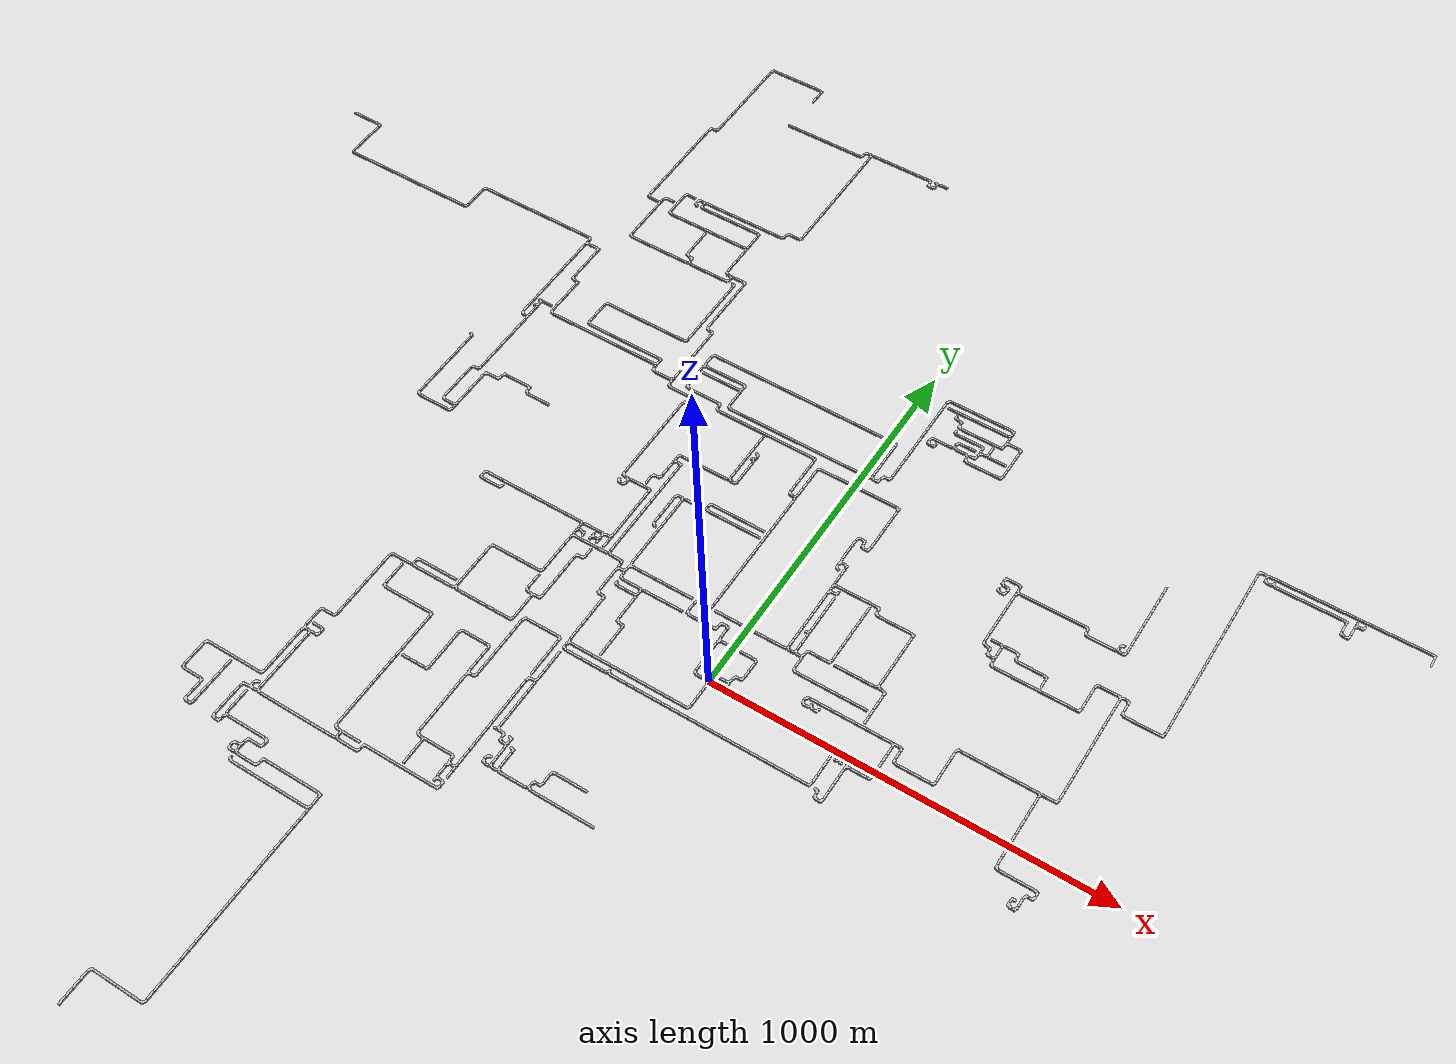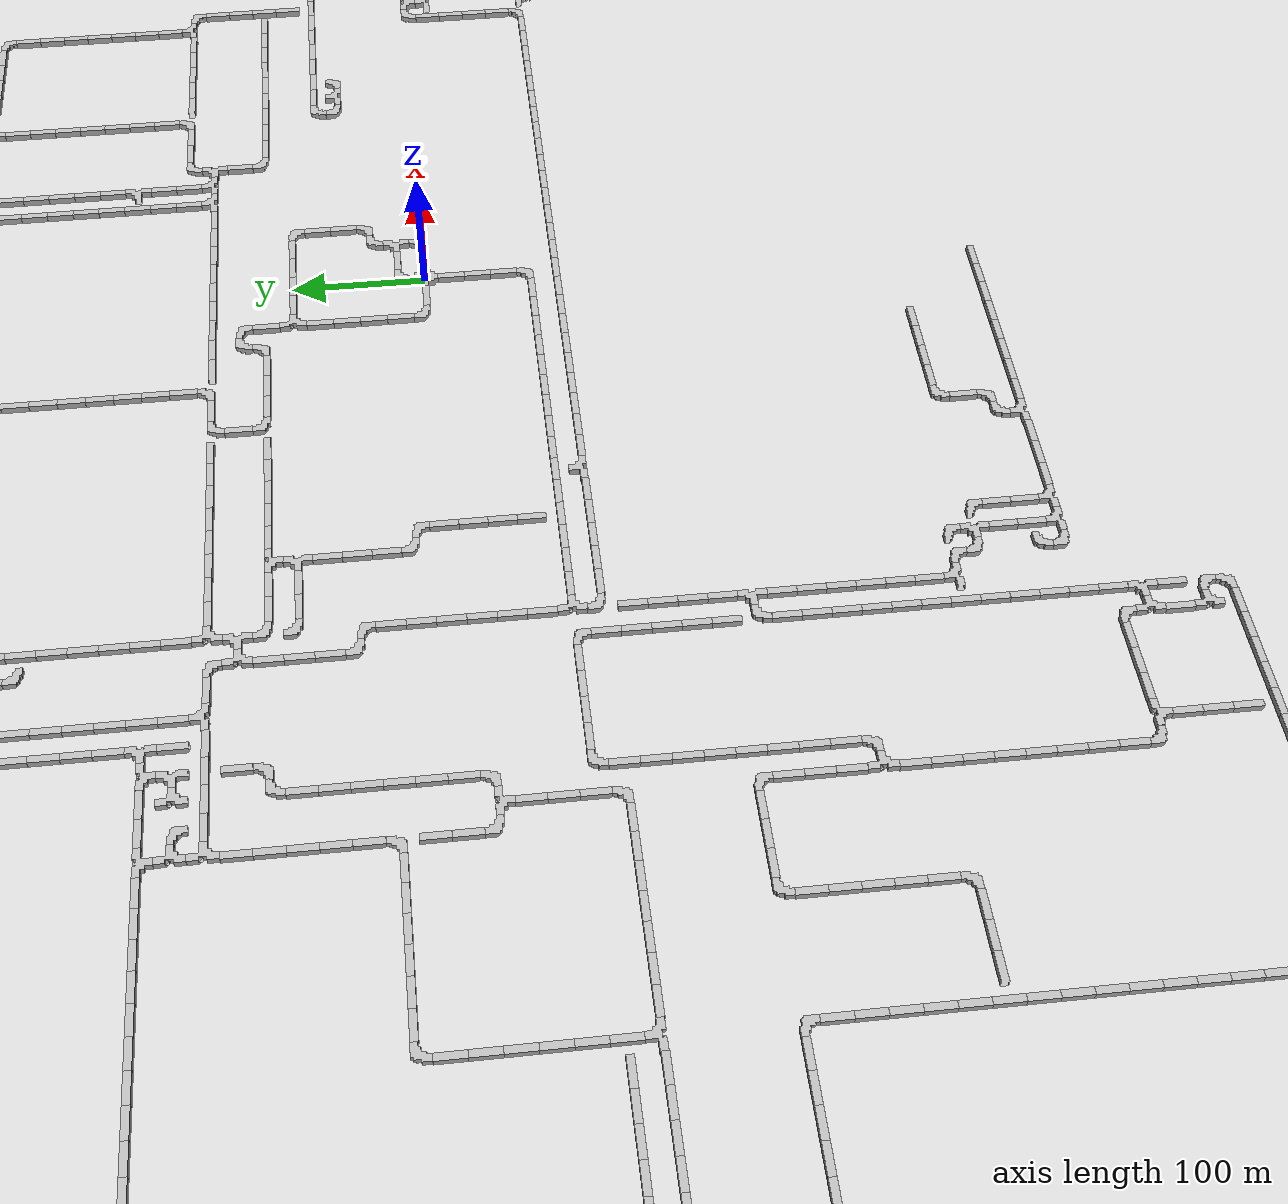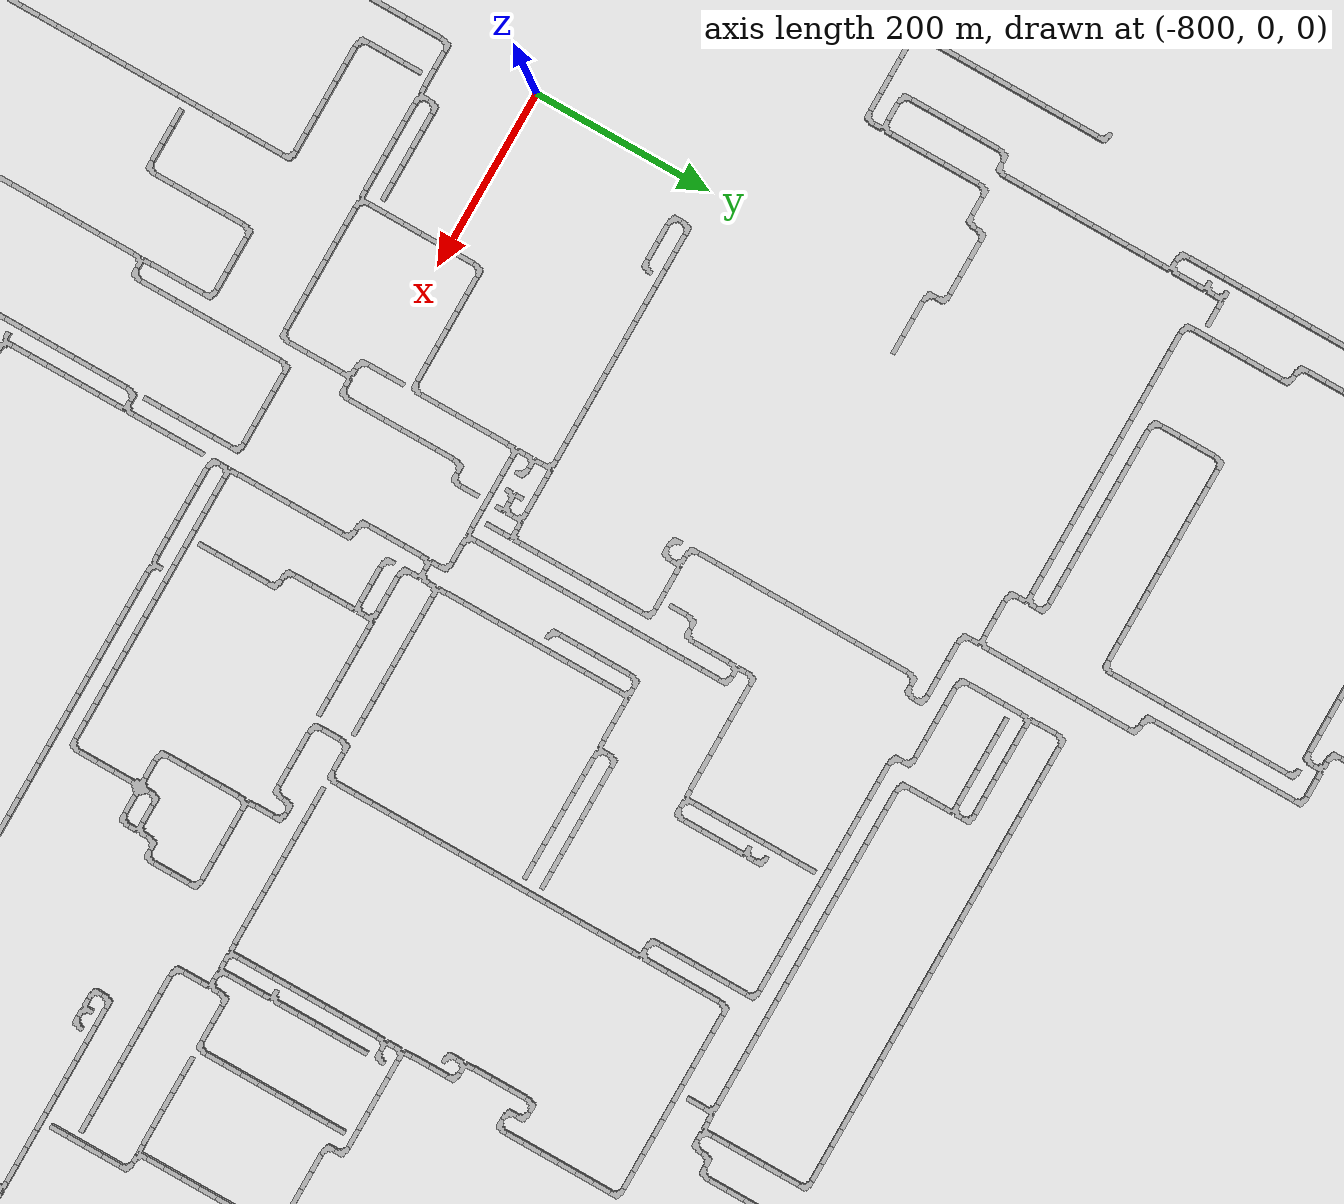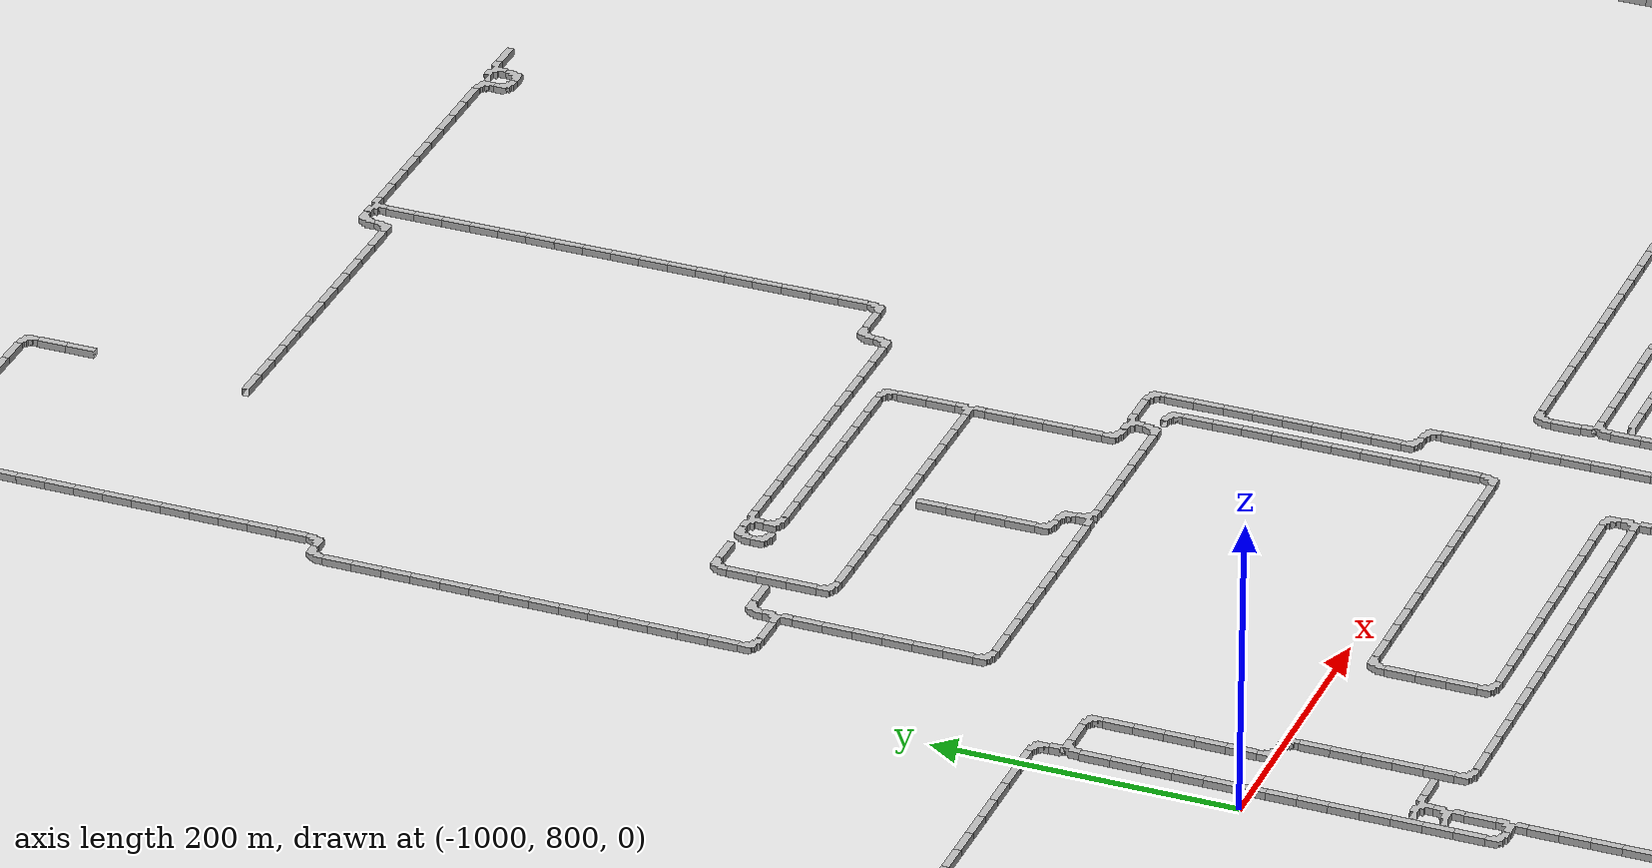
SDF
<sdf version="1.6">
<world name="cave_32000">
<include>
    <static>true</static>
    <name>cave_0_0</name>
    <pose>0 0 0 0 0 -1.5707963267948966</pose>
    <uri>model://cave_4way_20m</uri>
  </include>
  <include>
    <static>true</static>
    <name>cave_1_0</name>
    <pose>20 0 0 0 0 1.5707963267948966</pose>
    <uri>model://cave_straight_20m</uri>
  </include>
  <include>
    <static>true</static>
    <name>cave_2_0</name>
    <pose>40 0 0 0 0 1.5707963267948966</pose>
    <uri>model://cave_L_20m</uri>
  </include>
  <include>
    <static>true</static>
    <name>cave_2_1</name>
    <pose>40 20 0 0 0 1.5707963267948966</pose>
    <uri>model://cave_3way_20m</uri>
  </include>
  <include>
    <static>true</static>
    <name>cave_2_2</name>
    <pose>40 40 0 0 0 -1.5707963267948966</pose>
    <uri>model://cave_L_20m</uri>
  </include>
  <include>
    <static>true</static>
    <name>cave_3_2</name>
    <pose>60 40 0 0 0 1.5707963267948966</pose>
    <uri>model://cave_L_20m</uri>
  </include>
  <include>
    <static>true</static>
    <name>cave_3_3</name>
    <pose>60 60 0 0 0 0.0</pose>
    <uri>model://cave_straight_20m</uri>
  </include>
  <include>
    <static>true</static>
    <name>cave_3_4</name>
    <pose>60 80 0 0 0 0.0</pose>
    <uri>model://cave_straight_20m</uri>
  </include>
  <include>
    <static>true</static>
    <name>cave_3_5</name>
    <pose>60 100 0 0 0 3.141592653589793</pose>
    <uri>model://cave_L_20m</uri>
  </include>
  <include>
    <static>true</static>
    <name>cave_2_5</name>
    <pose>40 100 0 0 0 1.5707963267948966</pose>
    <uri>model://cave_straight_20m</uri>
  </include>
  <include>
    <static>true</static>
    <name>cave_1_5</name>
    <pose>20 100 0 0 0 1.5707963267948966</pose>
    <uri>model://cave_straight_20m</uri>
  </include>
  <include>
    <static>true</static>
    <name>cave_0_-1</name>
    <pose>0 -20 0 0 0 0.0</pose>
    <uri>model://cave_straight_20m</uri>
  </include>
  <include>
    <static>true</static>
    <name>cave_0_-2</name>
    <pose>0 -40 0 0 0 0.0</pose>
    <uri>model://cave_straight_20m</uri>
  </include>
  <include>
    <static>true</static>
    <name>cave_0_-3</name>
    <pose>0 -60 0 0 0 0.0</pose>
    <uri>model://cave_straight_20m</uri>
  </include>
  <include>
    <static>true</static>
    <name>cave_0_-4</name>
    <pose>0 -80 0 0 0 1.5707963267948966</pose>
    <uri>model://cave_L_20m</uri>
  </include>
  <include>
    <static>true</static>
    <name>cave_-1_-4</name>
    <pose>-20 -80 0 0 0 1.5707963267948966</pose>
    <uri>model://cave_straight_20m</uri>
  </include>
  <include>
    <static>true</static>
    <name>cave_-2_-4</name>
    <pose>-40 -80 0 0 0 1.5707963267948966</pose>
    <uri>model://cave_straight_20m</uri>
  </include>
  <include>
    <static>true</static>
    <name>cave_-3_-4</name>
    <pose>-60 -80 0 0 0 1.5707963267948966</pose>
    <uri>model://cave_straight_20m</uri>
  </include>
  <include>
    <static>true</static>
    <name>cave_-4_-4</name>
    <pose>-80 -80 0 0 0 1.5707963267948966</pose>
    <uri>model://cave_straight_20m</uri>
  </include>
  <include>
    <static>true</static>
    <name>cave_-5_-4</name>
    <pose>-100 -80 0 0 0 1.5707963267948966</pose>
    <uri>model://cave_straight_20m</uri>
  </include>
  <include>
    <static>true</static>
    <name>cave_-6_-4</name>
    <pose>-120 -80 0 0 0 1.5707963267948966</pose>
    <uri>model://cave_straight_20m</uri>
  </include>
  <include>
    <static>true</static>
    <name>cave_-7_-4</name>
    <pose>-140 -80 0 0 0 1.5707963267948966</pose>
    <uri>model://cave_straight_20m</uri>
  </include>
  <include>
    <static>true</static>
    <name>cave_-8_-4</name>
    <pose>-160 -80 0 0 0 1.5707963267948966</pose>
    <uri>model://cave_straight_20m</uri>
  </include>
  <include>
    <static>true</static>
    <name>cave_-9_-4</name>
    <pose>-180 -80 0 0 0 1.5707963267948966</pose>
    <uri>model://cave_straight_20m</uri>
  </include>
  <include>
    <static>true</static>
    <name>cave_-10_-4</name>
    <pose>-200 -80 0 0 0 1.5707963267948966</pose>
    <uri>model://cave_straight_20m</uri>
  </include>
  <include>
    <static>true</static>
    <name>cave_-11_-4</name>
    <pose>-220 -80 0 0 0 1.5707963267948966</pose>
    <uri>model://cave_straight_20m</uri>
  </include>
  <include>
    <static>true</static>
    <name>cave_-12_-4</name>
    <pose>-240 -80 0 0 0 1.5707963267948966</pose>
    <uri>model://cave_straight_20m</uri>
  </include>
  <include>
    <static>true</static>
    <name>cave_-13_-4</name>
    <pose>-260 -80 0 0 0 1.5707963267948966</pose>
    <uri>model://cave_straight_20m</uri>
  </include>
  <include>
    <static>true</static>
    <name>cave_-14_-4</name>
    <pose>-280 -80 0 0 0 1.5707963267948966</pose>
    <uri>model://cave_straight_20m</uri>
  </include>
  <include>
    <static>true</static>
    <name>cave_-15_-4</name>
    <pose>-300 -80 0 0 0 1.5707963267948966</pose>
    <uri>model://cave_straight_20m</uri>
  </include>
  <include>
    <static>true</static>
    <name>cave_-16_-4</name>
    <pose>-320 -80 0 0 0 -1.5707963267948966</pose>
    <uri>model://cave_3way_20m</uri>
  </include>
  <include>
    <static>true</static>
    <name>cave_-16_-5</name>
    <pose>-320 -100 0 0 0 0.0</pose>
    <uri>model://cave_L_20m</uri>
  </include>
  <include>
    <static>true</static>
    <name>cave_-15_-5</name>
    <pose>-300 -100 0 0 0 1.5707963267948966</pose>
    <uri>model://cave_straight_20m</uri>
  </include>
  <include>
    <static>true</static>
    <name>cave_-14_-5</name>
    <pose>-280 -100 0 0 0 1.5707963267948966</pose>
    <uri>model://cave_straight_20m</uri>
  </include>
  <include>
    <static>true</static>
    <name>cave_-13_-5</name>
    <pose>-260 -100 0 0 0 1.5707963267948966</pose>
    <uri>model://cave_straight_20m</uri>
  </include>
  <include>
    <static>true</static>
    <name>cave_-12_-5</name>
    <pose>-240 -100 0 0 0 1.5707963267948966</pose>
    <uri>model://cave_straight_20m</uri>
  </include>
  <include>
    <static>true</static>
    <name>cave_-11_-5</name>
    <pose>-220 -100 0 0 0 1.5707963267948966</pose>
    <uri>model://cave_straight_20m</uri>
  </include>
  <include>
    <static>true</static>
    <name>cave_-10_-5</name>
    <pose>-200 -100 0 0 0 0.0</pose>
    <uri>model://cave_3way_20m</uri>
  </include>
  <include>
    <static>true</static>
    <name>cave_-9_-5</name>
    <pose>-180 -100 0 0 0 1.5707963267948966</pose>
    <uri>model://cave_straight_20m</uri>
  </include>
  <include>
    <static>true</static>
    <name>cave_-8_-5</name>
    <pose>-160 -100 0 0 0 1.5707963267948966</pose>
    <uri>model://cave_straight_20m</uri>
  </include>
  <include>
    <static>true</static>
    <name>cave_-7_-5</name>
    <pose>-140 -100 0 0 0 1.5707963267948966</pose>
    <uri>model://cave_straight_20m</uri>
  </include>
  <include>
    <static>true</static>
    <name>cave_-6_-5</name>
    <pose>-120 -100 0 0 0 1.5707963267948966</pose>
    <uri>model://cave_straight_20m</uri>
  </include>
  <include>
    <static>true</static>
    <name>cave_-5_-5</name>
    <pose>-100 -100 0 0 0 1.5707963267948966</pose>
    <uri>model://cave_straight_20m</uri>
  </include>
  <include>
    <static>true</static>
    <name>cave_-4_-5</name>
    <pose>-80 -100 0 0 0 1.5707963267948966</pose>
    <uri>model://cave_straight_20m</uri>
  </include>
  <include>
    <static>true</static>
    <name>cave_-3_-5</name>
    <pose>-60 -100 0 0 0 1.5707963267948966</pose>
    <uri>model://cave_straight_20m</uri>
  </include>
  <include>
    <static>true</static>
    <name>cave_-2_-5</name>
    <pose>-40 -100 0 0 0 1.5707963267948966</pose>
    <uri>model://cave_straight_20m</uri>
  </include>
  <include>
    <static>true</static>
    <name>cave_-1_-5</name>
    <pose>-20 -100 0 0 0 1.5707963267948966</pose>
    <uri>model://cave_straight_20m</uri>
  </include>
  <include>
    <static>true</static>
    <name>cave_0_-5</name>
    <pose>0 -100 0 0 0 1.5707963267948966</pose>
    <uri>model://cave_straight_20m</uri>
  </include>
  <include>
    <static>true</static>
    <name>cave_1_-5</name>
    <pose>20 -100 0 0 0 1.5707963267948966</pose>
    <uri>model://cave_straight_20m</uri>
  </include>
  <include>
    <static>true</static>
    <name>cave_2_-5</name>
    <pose>40 -100 0 0 0 1.5707963267948966</pose>
    <uri>model://cave_straight_20m</uri>
  </include>
  <include>
    <static>true</static>
    <name>cave_3_-5</name>
    <pose>60 -100 0 0 0 1.5707963267948966</pose>
    <uri>model://cave_straight_20m</uri>
  </include>
  <include>
    <static>true</static>
    <name>cave_4_-5</name>
    <pose>80 -100 0 0 0 1.5707963267948966</pose>
    <uri>model://cave_straight_20m</uri>
  </include>
  <include>
    <static>true</static>
    <name>cave_5_-5</name>
    <pose>100 -100 0 0 0 1.5707963267948966</pose>
    <uri>model://cave_straight_20m</uri>
  </include>
  <include>
    <static>true</static>
    <name>cave_6_-5</name>
    <pose>120 -100 0 0 0 1.5707963267948966</pose>
    <uri>model://cave_straight_20m</uri>
  </include>
  <include>
    <static>true</static>
    <name>cave_7_-5</name>
    <pose>140 -100 0 0 0 1.5707963267948966</pose>
    <uri>model://cave_straight_20m</uri>
  </include>
  <include>
    <static>true</static>
    <name>cave_8_-5</name>
    <pose>160 -100 0 0 0 1.5707963267948966</pose>
    <uri>model://cave_straight_20m</uri>
  </include>
  <include>
    <static>true</static>
    <name>cave_9_-5</name>
    <pose>180 -100 0 0 0 1.5707963267948966</pose>
    <uri>model://cave_straight_20m</uri>
  </include>
  <include>
    <static>true</static>
    <name>cave_10_-5</name>
    <pose>200 -100 0 0 0 1.5707963267948966</pose>
    <uri>model://cave_straight_20m</uri>
  </include>
  <include>
    <static>true</static>
    <name>cave_11_-5</name>
    <pose>220 -100 0 0 0 1.5707963267948966</pose>
    <uri>model://cave_straight_20m</uri>
  </include>
  <include>
    <static>true</static>
    <name>cave_12_-5</name>
    <pose>240 -100 0 0 0 1.5707963267948966</pose>
    <uri>model://cave_straight_20m</uri>
  </include>
  <include>
    <static>true</static>
    <name>cave_13_-5</name>
    <pose>260 -100 0 0 0 1.5707963267948966</pose>
    <uri>model://cave_straight_20m</uri>
  </include>
  <include>
    <static>true</static>
    <name>cave_14_-5</name>
    <pose>280 -100 0 0 0 1.5707963267948966</pose>
    <uri>model://cave_straight_20m</uri>
  </include>
  <include>
    <static>true</static>
    <name>cave_15_-5</name>
    <pose>300 -100 0 0 0 1.5707963267948966</pose>
    <uri>model://cave_straight_20m</uri>
  </include>
  <include>
    <static>true</static>
    <name>cave_16_-5</name>
    <pose>320 -100 0 0 0 1.5707963267948966</pose>
    <uri>model://cave_L_20m</uri>
  </include>
  <include>
    <static>true</static>
    <name>cave_16_-4</name>
    <pose>320 -80 0 0 0 0.0</pose>
    <uri>model://cave_straight_20m</uri>
  </include>
  <include>
    <static>true</static>
    <name>cave_16_-3</name>
    <pose>320 -60 0 0 0 0.0</pose>
    <uri>model://cave_straight_20m</uri>
  </include>
  <include>
    <static>true</static>
    <name>cave_16_-2</name>
    <pose>320 -40 0 0 0 0.0</pose>
    <uri>model://cave_straight_20m</uri>
  </include>
  <include>
    <static>true</static>
    <name>cave_16_-1</name>
    <pose>320 -20 0 0 0 0.0</pose>
    <uri>model://cave_straight_20m</uri>
  </include>
  <include>
    <static>true</static>
    <name>cave_16_0</name>
    <pose>320 0 0 0 0 -1.5707963267948966</pose>
    <uri>model://cave_L_20m</uri>
  </include>
  <include>
    <static>true</static>
    <name>cave_17_0</name>
    <pose>340 0 0 0 0 3.141592653589793</pose>
    <uri>model://cave_3way_20m</uri>
  </include>
  <include>
    <static>true</static>
    <name>cave_18_0</name>
    <pose>360 0 0 0 0 3.141592653589793</pose>
    <uri>model://cave_L_20m</uri>
  </include>
  <include>
    <static>true</static>
    <name>cave_18_-1</name>
    <pose>360 -20 0 0 0 -1.5707963267948966</pose>
    <uri>model://cave_3way_20m</uri>
  </include>
  <include>
    <static>true</static>
    <name>cave_19_-1</name>
    <pose>380 -20 0 0 0 1.5707963267948966</pose>
    <uri>model://cave_straight_20m</uri>
  </include>
  <include>
    <static>true</static>
    <name>cave_20_-1</name>
    <pose>400 -20 0 0 0 1.5707963267948966</pose>
    <uri>model://cave_straight_20m</uri>
  </include>
  <include>
    <static>true</static>
    <name>cave_21_-1</name>
    <pose>420 -20 0 0 0 1.5707963267948966</pose>
    <uri>model://cave_L_20m</uri>
  </include>
  <include>
    <static>true</static>
    <name>cave_21_0</name>
    <pose>420 0 0 0 0 0.0</pose>
    <uri>model://cave_straight_20m</uri>
  </include>
  <include>
    <static>true</static>
    <name>cave_21_1</name>
    <pose>420 20 0 0 0 0.0</pose>
    <uri>model://cave_straight_20m</uri>
  </include>
  <include>
    <static>true</static>
    <name>cave_21_2</name>
    <pose>420 40 0 0 0 0.0</pose>
    <uri>model://cave_straight_20m</uri>
  </include>
  <include>
    <static>true</static>
    <name>cave_21_3</name>
    <pose>420 60 0 0 0 0.0</pose>
    <uri>model://cave_straight_20m</uri>
  </include>
  <include>
    <static>true</static>
    <name>cave_21_4</name>
    <pose>420 80 0 0 0 3.141592653589793</pose>
    <uri>model://cave_3way_20m</uri>
  </include>
  <include>
    <static>true</static>
    <name>cave_22_4</name>
    <pose>440 80 0 0 0 3.141592653589793</pose>
    <uri>model://cave_L_20m</uri>
  </include>
  <include>
    <static>true</static>
    <name>cave_22_3</name>
    <pose>440 60 0 0 0 0.0</pose>
    <uri>model://cave_straight_20m</uri>
  </include>
  <include>
    <static>true</static>
    <name>cave_22_2</name>
    <pose>440 40 0 0 0 0.0</pose>
    <uri>model://cave_L_20m</uri>
  </include>
  <include>
    <static>true</static>
    <name>cave_23_2</name>
    <pose>460 40 0 0 0 1.5707963267948966</pose>
    <uri>model://cave_straight_20m</uri>
  </include>
  <include>
    <static>true</static>
    <name>cave_24_2</name>
    <pose>480 40 0 0 0 1.5707963267948966</pose>
    <uri>model://cave_straight_20m</uri>
  </include>
  <include>
    <static>true</static>
    <name>cave_25_2</name>
    <pose>500 40 0 0 0 1.5707963267948966</pose>
    <uri>model://cave_straight_20m</uri>
  </include>
  <include>
    <static>true</static>
    <name>cave_26_2</name>
    <pose>520 40 0 0 0 1.5707963267948966</pose>
    <uri>model://cave_straight_20m</uri>
  </include>
  <include>
    <static>true</static>
    <name>cave_27_2</name>
    <pose>540 40 0 0 0 1.5707963267948966</pose>
    <uri>model://cave_L_20m</uri>
  </include>
  <include>
    <static>true</static>
    <name>cave_27_3</name>
    <pose>540 60 0 0 0 0.0</pose>
    <uri>model://cave_straight_20m</uri>
  </include>
  <include>
    <static>true</static>
    <name>cave_27_4</name>
    <pose>540 80 0 0 0 0.0</pose>
    <uri>model://cave_straight_20m</uri>
  </include>
  <include>
    <static>true</static>
    <name>cave_27_5</name>
    <pose>540 100 0 0 0 0.0</pose>
    <uri>model://cave_straight_20m</uri>
  </include>
  <include>
    <static>true</static>
    <name>cave_27_6</name>
    <pose>540 120 0 0 0 0.0</pose>
    <uri>model://cave_straight_20m</uri>
  </include>
  <include>
    <static>true</static>
    <name>cave_27_7</name>
    <pose>540 140 0 0 0 -1.5707963267948966</pose>
    <uri>model://cave_L_20m</uri>
  </include>
  <include>
    <static>true</static>
    <name>cave_28_7</name>
    <pose>560 140 0 0 0 1.5707963267948966</pose>
    <uri>model://cave_straight_20m</uri>
  </include>
  <include>
    <static>true</static>
    <name>cave_29_7</name>
    <pose>580 140 0 0 0 1.5707963267948966</pose>
    <uri>model://cave_straight_20m</uri>
  </include>
  <include>
    <static>true</static>
    <name>cave_30_7</name>
    <pose>600 140 0 0 0 1.5707963267948966</pose>
    <uri>model://cave_straight_20m</uri>
  </include>
  <include>
    <static>true</static>
    <name>cave_31_7</name>
    <pose>620 140 0 0 0 1.5707963267948966</pose>
    <uri>model://cave_straight_20m</uri>
  </include>
  <include>
    <static>true</static>
    <name>cave_32_7</name>
    <pose>640 140 0 0 0 1.5707963267948966</pose>
    <uri>model://cave_straight_20m</uri>
  </include>
  <include>
    <static>true</static>
    <name>cave_33_7</name>
    <pose>660 140 0 0 0 1.5707963267948966</pose>
    <uri>model://cave_straight_20m</uri>
  </include>
  <include>
    <static>true</static>
    <name>cave_34_7</name>
    <pose>680 140 0 0 0 1.5707963267948966</pose>
    <uri>model://cave_straight_20m</uri>
  </include>
  <include>
    <static>true</static>
    <name>cave_35_7</name>
    <pose>700 140 0 0 0 1.5707963267948966</pose>
    <uri>model://cave_straight_20m</uri>
  </include>
  <include>
    <static>true</static>
    <name>cave_36_7</name>
    <pose>720 140 0 0 0 1.5707963267948966</pose>
    <uri>model://cave_straight_20m</uri>
  </include>
  <include>
    <static>true</static>
    <name>cave_37_7</name>
    <pose>740 140 0 0 0 3.141592653589793</pose>
    <uri>model://cave_3way_20m</uri>
  </include>
  <include>
    <static>true</static>
    <name>cave_38_7</name>
    <pose>760 140 0 0 0 1.5707963267948966</pose>
    <uri>model://cave_straight_20m</uri>
  </include>
  <include>
    <static>true</static>
    <name>cave_39_7</name>
    <pose>780 140 0 0 0 1.5707963267948966</pose>
    <uri>model://cave_L_20m</uri>
  </include>
  <include>
    <static>true</static>
    <name>cave_39_8</name>
    <pose>780 160 0 0 0 0.0</pose>
    <uri>model://cave_straight_20m</uri>
  </include>
  <include>
    <static>true</static>
    <name>cave_39_9</name>
    <pose>780 180 0 0 0 0.0</pose>
    <uri>model://cave_straight_20m</uri>
  </include>
  <include>
    <static>true</static>
    <name>cave_39_10</name>
    <pose>780 200 0 0 0 0.0</pose>
    <uri>model://cave_straight_20m</uri>
  </include>
  <include>
    <static>true</static>
    <name>cave_39_11</name>
    <pose>780 220 0 0 0 0.0</pose>
    <uri>model://cave_straight_20m</uri>
  </include>
  <include>
    <static>true</static>
    <name>cave_39_12</name>
    <pose>780 240 0 0 0 0.0</pose>
    <uri>model://cave_straight_20m</uri>
  </include>
  <include>
    <static>true</static>
    <name>cave_39_13</name>
    <pose>780 260 0 0 0 0.0</pose>
    <uri>model://cave_straight_20m</uri>
  </include>
  <include>
    <static>true</static>
    <name>cave_39_14</name>
    <pose>780 280 0 0 0 0.0</pose>
    <uri>model://cave_straight_20m</uri>
  </include>
  <include>
    <static>true</static>
    <name>cave_39_15</name>
    <pose>780 300 0 0 0 0.0</pose>
    <uri>model://cave_straight_20m</uri>
  </include>
  <include>
    <static>true</static>
    <name>cave_39_16</name>
    <pose>780 320 0 0 0 0.0</pose>
    <uri>model://cave_straight_20m</uri>
  </include>
  <include>
    <static>true</static>
    <name>cave_39_17</name>
    <pose>780 340 0 0 0 0.0</pose>
    <uri>model://cave_straight_20m</uri>
  </include>
  <include>
    <static>true</static>
    <name>cave_39_18</name>
    <pose>780 360 0 0 0 0.0</pose>
    <uri>model://cave_straight_20m</uri>
  </include>
  <include>
    <static>true</static>
    <name>cave_39_19</name>
    <pose>780 380 0 0 0 0.0</pose>
    <uri>model://cave_straight_20m</uri>
  </include>
  <include>
    <static>true</static>
    <name>cave_39_20</name>
    <pose>780 400 0 0 0 0.0</pose>
    <uri>model://cave_straight_20m</uri>
  </include>
  <include>
    <static>true</static>
    <name>cave_39_21</name>
    <pose>780 420 0 0 0 0.0</pose>
    <uri>model://cave_straight_20m</uri>
  </include>
  <include>
    <static>true</static>
    <name>cave_39_22</name>
    <pose>780 440 0 0 0 3.141592653589793</pose>
    <uri>model://cave_3way_20m</uri>
  </include>
  <include>
    <static>true</static>
    <name>cave_40_22</name>
    <pose>800 440 0 0 0 3.141592653589793</pose>
    <uri>model://cave_L_20m</uri>
  </include>
  <include>
    <static>true</static>
    <name>cave_40_21</name>
    <pose>800 420 0 0 0 0.0</pose>
    <uri>model://cave_straight_20m</uri>
  </include>
  <include>
    <static>true</static>
    <name>cave_40_20</name>
    <pose>800 400 0 0 0 0.0</pose>
    <uri>model://cave_L_20m</uri>
  </include>
  <include>
    <static>true</static>
    <name>cave_41_20</name>
    <pose>820 400 0 0 0 1.5707963267948966</pose>
    <uri>model://cave_straight_20m</uri>
  </include>
  <include>
    <static>true</static>
    <name>cave_42_20</name>
    <pose>840 400 0 0 0 1.5707963267948966</pose>
    <uri>model://cave_straight_20m</uri>
  </include>
  <include>
    <static>true</static>
    <name>cave_43_20</name>
    <pose>860 400 0 0 0 1.5707963267948966</pose>
    <uri>model://cave_straight_20m</uri>
  </include>
  <include>
    <static>true</static>
    <name>cave_44_20</name>
    <pose>880 400 0 0 0 1.5707963267948966</pose>
    <uri>model://cave_straight_20m</uri>
  </include>
  <include>
    <static>true</static>
    <name>cave_45_20</name>
    <pose>900 400 0 0 0 1.5707963267948966</pose>
    <uri>model://cave_L_20m</uri>
  </include>
  <include>
    <static>true</static>
    <name>cave_45_21</name>
    <pose>900 420 0 0 0 0.0</pose>
    <uri>model://cave_straight_20m</uri>
  </include>
  <include>
    <static>true</static>
    <name>cave_45_22</name>
    <pose>900 440 0 0 0 0.0</pose>
    <uri>model://cave_straight_20m</uri>
  </include>
  <include>
    <static>true</static>
    <name>cave_45_23</name>
    <pose>900 460 0 0 0 0.0</pose>
    <uri>model://cave_straight_20m</uri>
  </include>
  <include>
    <static>true</static>
    <name>cave_45_24</name>
    <pose>900 480 0 0 0 0.0</pose>
    <uri>model://cave_straight_20m</uri>
  </include>
  <include>
    <static>true</static>
    <name>cave_45_25</name>
    <pose>900 500 0 0 0 0.0</pose>
    <uri>model://cave_straight_20m</uri>
  </include>
  <include>
    <static>true</static>
    <name>cave_45_26</name>
    <pose>900 520 0 0 0 0.0</pose>
    <uri>model://cave_straight_20m</uri>
  </include>
  <include>
    <static>true</static>
    <name>cave_45_27</name>
    <pose>900 540 0 0 0 0.0</pose>
    <uri>model://cave_straight_20m</uri>
  </include>
  <include>
    <static>true</static>
    <name>cave_45_28</name>
    <pose>900 560 0 0 0 0.0</pose>
    <uri>model://cave_straight_20m</uri>
  </include>
  <include>
    <static>true</static>
    <name>cave_45_29</name>
    <pose>900 580 0 0 0 0.0</pose>
    <uri>model://cave_straight_20m</uri>
  </include>
  <include>
    <static>true</static>
    <name>cave_45_30</name>
    <pose>900 600 0 0 0 0.0</pose>
    <uri>model://cave_straight_20m</uri>
  </include>
  <include>
    <static>true</static>
    <name>cave_45_31</name>
    <pose>900 620 0 0 0 0.0</pose>
    <uri>model://cave_straight_20m</uri>
  </include>
  <include>
    <static>true</static>
    <name>cave_45_32</name>
    <pose>900 640 0 0 0 0.0</pose>
    <uri>model://cave_straight_20m</uri>
  </include>
  <include>
    <static>true</static>
    <name>cave_45_33</name>
    <pose>900 660 0 0 0 0.0</pose>
    <uri>model://cave_straight_20m</uri>
  </include>
  <include>
    <static>true</static>
    <name>cave_45_34</name>
    <pose>900 680 0 0 0 0.0</pose>
    <uri>model://cave_straight_20m</uri>
  </include>
  <include>
    <static>true</static>
    <name>cave_45_35</name>
    <pose>900 700 0 0 0 0.0</pose>
    <uri>model://cave_straight_20m</uri>
  </include>
  <include>
    <static>true</static>
    <name>cave_45_36</name>
    <pose>900 720 0 0 0 0.0</pose>
    <uri>model://cave_straight_20m</uri>
  </include>
  <include>
    <static>true</static>
    <name>cave_45_37</name>
    <pose>900 740 0 0 0 0.0</pose>
    <uri>model://cave_straight_20m</uri>
  </include>
  <include>
    <static>true</static>
    <name>cave_45_38</name>
    <pose>900 760 0 0 0 0.0</pose>
    <uri>model://cave_straight_20m</uri>
  </include>
  <include>
    <static>true</static>
    <name>cave_45_39</name>
    <pose>900 780 0 0 0 0.0</pose>
    <uri>model://cave_straight_20m</uri>
  </include>
  <include>
    <static>true</static>
    <name>cave_45_40</name>
    <pose>900 800 0 0 0 0.0</pose>
    <uri>model://cave_straight_20m</uri>
  </include>
  <include>
    <static>true</static>
    <name>cave_45_41</name>
    <pose>900 820 0 0 0 0.0</pose>
    <uri>model://cave_straight_20m</uri>
  </include>
  <include>
    <static>true</static>
    <name>cave_45_42</name>
    <pose>900 840 0 0 0 0.0</pose>
    <uri>model://cave_straight_20m</uri>
  </include>
  <include>
    <static>true</static>
    <name>cave_45_43</name>
    <pose>900 860 0 0 0 0.0</pose>
    <uri>model://cave_straight_20m</uri>
  </include>
  <include>
    <static>true</static>
    <name>cave_45_44</name>
    <pose>900 880 0 0 0 0.0</pose>
    <uri>model://cave_straight_20m</uri>
  </include>
  <include>
    <static>true</static>
    <name>cave_45_45</name>
    <pose>900 900 0 0 0 -1.5707963267948966</pose>
    <uri>model://cave_L_20m</uri>
  </include>
  <include>
    <static>true</static>
    <name>cave_46_45</name>
    <pose>920 900 0 0 0 3.141592653589793</pose>
    <uri>model://cave_3way_20m</uri>
  </include>
  <include>
    <static>true</static>
    <name>cave_47_45</name>
    <pose>940 900 0 0 0 1.5707963267948966</pose>
    <uri>model://cave_straight_20m</uri>
  </include>
  <include>
    <static>true</static>
    <name>cave_48_45</name>
    <pose>960 900 0 0 0 1.5707963267948966</pose>
    <uri>model://cave_straight_20m</uri>
  </include>
  <include>
    <static>true</static>
    <name>cave_49_45</name>
    <pose>980 900 0 0 0 1.5707963267948966</pose>
    <uri>model://cave_straight_20m</uri>
  </include>
  <include>
    <static>true</static>
    <name>cave_50_45</name>
    <pose>1000 900 0 0 0 1.5707963267948966</pose>
    <uri>model://cave_straight_20m</uri>
  </include>
  <include>
    <static>true</static>
    <name>cave_51_45</name>
    <pose>1020 900 0 0 0 1.5707963267948966</pose>
    <uri>model://cave_straight_20m</uri>
  </include>
  <include>
    <static>true</static>
    <name>cave_52_45</name>
    <pose>1040 900 0 0 0 1.5707963267948966</pose>
    <uri>model://cave_straight_20m</uri>
  </include>
  <include>
    <static>true</static>
    <name>cave_53_45</name>
    <pose>1060 900 0 0 0 1.5707963267948966</pose>
    <uri>model://cave_straight_20m</uri>
  </include>
  <include>
    <static>true</static>
    <name>cave_54_45</name>
    <pose>1080 900 0 0 0 1.5707963267948966</pose>
    <uri>model://cave_straight_20m</uri>
  </include>
  <include>
    <static>true</static>
    <name>cave_55_45</name>
    <pose>1100 900 0 0 0 1.5707963267948966</pose>
    <uri>model://cave_straight_20m</uri>
  </include>
  <include>
    <static>true</static>
    <name>cave_56_45</name>
    <pose>1120 900 0 0 0 1.5707963267948966</pose>
    <uri>model://cave_straight_20m</uri>
  </include>
  <include>
    <static>true</static>
    <name>cave_57_45</name>
    <pose>1140 900 0 0 0 1.5707963267948966</pose>
    <uri>model://cave_straight_20m</uri>
  </include>
  <include>
    <static>true</static>
    <name>cave_58_45</name>
    <pose>1160 900 0 0 0 1.5707963267948966</pose>
    <uri>model://cave_straight_20m</uri>
  </include>
  <include>
    <static>true</static>
    <name>cave_59_45</name>
    <pose>1180 900 0 0 0 1.5707963267948966</pose>
    <uri>model://cave_straight_20m</uri>
  </include>
  <include>
    <static>true</static>
    <name>cave_60_45</name>
    <pose>1200 900 0 0 0 1.5707963267948966</pose>
    <uri>model://cave_straight_20m</uri>
  </include>
  <include>
    <static>true</static>
    <name>cave_61_45</name>
    <pose>1220 900 0 0 0 1.5707963267948966</pose>
    <uri>model://cave_straight_20m</uri>
  </include>
  <include>
    <static>true</static>
    <name>cave_62_45</name>
    <pose>1240 900 0 0 0 1.5707963267948966</pose>
    <uri>model://cave_straight_20m</uri>
  </include>
  <include>
    <static>true</static>
    <name>cave_63_45</name>
    <pose>1260 900 0 0 0 1.5707963267948966</pose>
    <uri>model://cave_straight_20m</uri>
  </include>
  <include>
    <static>true</static>
    <name>cave_64_45</name>
    <pose>1280 900 0 0 0 1.5707963267948966</pose>
    <uri>model://cave_straight_20m</uri>
  </include>
  <include>
    <static>true</static>
    <name>cave_65_45</name>
    <pose>1300 900 0 0 0 1.5707963267948966</pose>
    <uri>model://cave_straight_20m</uri>
  </include>
  <include>
    <static>true</static>
    <name>cave_66_45</name>
    <pose>1320 900 0 0 0 3.141592653589793</pose>
    <uri>model://cave_L_20m</uri>
  </include>
  <include>
    <static>true</static>
    <name>cave_66_44</name>
    <pose>1320 880 0 0 0 0.0</pose>
    <uri>model://cave_straight_20m</uri>
  </include>
  <include>
    <static>true</static>
    <name>cave_46_44</name>
    <pose>920 880 0 0 0 0.0</pose>
    <uri>model://cave_L_20m</uri>
  </include>
  <include>
    <static>true</static>
    <name>cave_47_44</name>
    <pose>940 880 0 0 0 0.0</pose>
    <uri>model://cave_3way_20m</uri>
  </include>
  <include>
    <static>true</static>
    <name>cave_48_44</name>
    <pose>960 880 0 0 0 1.5707963267948966</pose>
    <uri>model://cave_straight_20m</uri>
  </include>
  <include>
    <static>true</static>
    <name>cave_49_44</name>
    <pose>980 880 0 0 0 1.5707963267948966</pose>
    <uri>model://cave_straight_20m</uri>
  </include>
  <include>
    <static>true</static>
    <name>cave_50_44</name>
    <pose>1000 880 0 0 0 1.5707963267948966</pose>
    <uri>model://cave_straight_20m</uri>
  </include>
  <include>
    <static>true</static>
    <name>cave_51_44</name>
    <pose>1020 880 0 0 0 1.5707963267948966</pose>
    <uri>model://cave_straight_20m</uri>
  </include>
  <include>
    <static>true</static>
    <name>cave_52_44</name>
    <pose>1040 880 0 0 0 1.5707963267948966</pose>
    <uri>model://cave_straight_20m</uri>
  </include>
  <include>
    <static>true</static>
    <name>cave_53_44</name>
    <pose>1060 880 0 0 0 1.5707963267948966</pose>
    <uri>model://cave_straight_20m</uri>
  </include>
  <include>
    <static>true</static>
    <name>cave_54_44</name>
    <pose>1080 880 0 0 0 1.5707963267948966</pose>
    <uri>model://cave_straight_20m</uri>
  </include>
  <include>
    <static>true</static>
    <name>cave_55_44</name>
    <pose>1100 880 0 0 0 1.5707963267948966</pose>
    <uri>model://cave_straight_20m</uri>
  </include>
  <include>
    <static>true</static>
    <name>cave_56_44</name>
    <pose>1120 880 0 0 0 3.141592653589793</pose>
    <uri>model://cave_L_20m</uri>
  </include>
  <include>
    <static>true</static>
    <name>cave_56_43</name>
    <pose>1120 860 0 0 0 0.0</pose>
    <uri>model://cave_straight_20m</uri>
  </include>
  <include>
    <static>true</static>
    <name>cave_56_42</name>
    <pose>1120 840 0 0 0 0.0</pose>
    <uri>model://cave_L_20m</uri>
  </include>
  <include>
    <static>true</static>
    <name>cave_57_42</name>
    <pose>1140 840 0 0 0 1.5707963267948966</pose>
    <uri>model://cave_L_20m</uri>
  </include>
  <include>
    <static>true</static>
    <name>cave_57_43</name>
    <pose>1140 860 0 0 0 0.0</pose>
    <uri>model://cave_straight_20m</uri>
  </include>
  <include>
    <static>true</static>
    <name>cave_57_44</name>
    <pose>1140 880 0 0 0 -1.5707963267948966</pose>
    <uri>model://cave_3way_20m</uri>
  </include>
  <include>
    <static>true</static>
    <name>cave_58_44</name>
    <pose>1160 880 0 0 0 1.5707963267948966</pose>
    <uri>model://cave_L_20m</uri>
  </include>
  <include>
    <static>true</static>
    <name>cave_38_22</name>
    <pose>760 440 0 0 0 1.5707963267948966</pose>
    <uri>model://cave_straight_20m</uri>
  </include>
  <include>
    <static>true</static>
    <name>cave_37_22</name>
    <pose>740 440 0 0 0 1.5707963267948966</pose>
    <uri>model://cave_straight_20m</uri>
  </include>
  <include>
    <static>true</static>
    <name>cave_36_22</name>
    <pose>720 440 0 0 0 -1.5707963267948966</pose>
    <uri>model://cave_L_20m</uri>
  </include>
  <include>
    <static>true</static>
    <name>cave_36_21</name>
    <pose>720 420 0 0 0 0.0</pose>
    <uri>model://cave_straight_20m</uri>
  </include>
  <include>
    <static>true</static>
    <name>cave_36_20</name>
    <pose>720 400 0 0 0 0.0</pose>
    <uri>model://cave_straight_20m</uri>
  </include>
  <include>
    <static>true</static>
    <name>cave_36_19</name>
    <pose>720 380 0 0 0 0.0</pose>
    <uri>model://cave_straight_20m</uri>
  </include>
  <include>
    <static>true</static>
    <name>cave_36_18</name>
    <pose>720 360 0 0 0 1.5707963267948966</pose>
    <uri>model://cave_L_20m</uri>
  </include>
  <include>
    <static>true</static>
    <name>cave_35_18</name>
    <pose>700 360 0 0 0 1.5707963267948966</pose>
    <uri>model://cave_straight_20m</uri>
  </include>
  <include>
    <static>true</static>
    <name>cave_34_18</name>
    <pose>680 360 0 0 0 1.5707963267948966</pose>
    <uri>model://cave_straight_20m</uri>
  </include>
  <include>
    <static>true</static>
    <name>cave_33_18</name>
    <pose>660 360 0 0 0 1.5707963267948966</pose>
    <uri>model://cave_straight_20m</uri>
  </include>
  <include>
    <static>true</static>
    <name>cave_32_18</name>
    <pose>640 360 0 0 0 1.5707963267948966</pose>
    <uri>model://cave_straight_20m</uri>
  </include>
  <include>
    <static>true</static>
    <name>cave_31_18</name>
    <pose>620 360 0 0 0 1.5707963267948966</pose>
    <uri>model://cave_straight_20m</uri>
  </include>
  <include>
    <static>true</static>
    <name>cave_30_18</name>
    <pose>600 360 0 0 0 1.5707963267948966</pose>
    <uri>model://cave_straight_20m</uri>
  </include>
  <include>
    <static>true</static>
    <name>cave_29_18</name>
    <pose>580 360 0 0 0 1.5707963267948966</pose>
    <uri>model://cave_straight_20m</uri>
  </include>
  <include>
    <static>true</static>
    <name>cave_28_18</name>
    <pose>560 360 0 0 0 1.5707963267948966</pose>
    <uri>model://cave_straight_20m</uri>
  </include>
  <include>
    <static>true</static>
    <name>cave_27_18</name>
    <pose>540 360 0 0 0 1.5707963267948966</pose>
    <uri>model://cave_straight_20m</uri>
  </include>
  <include>
    <static>true</static>
    <name>cave_26_18</name>
    <pose>520 360 0 0 0 1.5707963267948966</pose>
    <uri>model://cave_straight_20m</uri>
  </include>
  <include>
    <static>true</static>
    <name>cave_25_18</name>
    <pose>500 360 0 0 0 0.0</pose>
    <uri>model://cave_L_20m</uri>
  </include>
  <include>
    <static>true</static>
    <name>cave_25_19</name>
    <pose>500 380 0 0 0 1.5707963267948966</pose>
    <uri>model://cave_3way_20m</uri>
  </include>
  <include>
    <static>true</static>
    <name>cave_24_19</name>
    <pose>480 380 0 0 0 0.0</pose>
    <uri>model://cave_L_20m</uri>
  </include>
  <include>
    <static>true</static>
    <name>cave_24_20</name>
    <pose>480 400 0 0 0 3.141592653589793</pose>
    <uri>model://cave_L_20m</uri>
  </include>
  <include>
    <static>true</static>
    <name>cave_23_20</name>
    <pose>460 400 0 0 0 0.0</pose>
    <uri>model://cave_L_20m</uri>
  </include>
  <include>
    <static>true</static>
    <name>cave_23_21</name>
    <pose>460 420 0 0 0 0.0</pose>
    <uri>model://cave_straight_20m</uri>
  </include>
  <include>
    <static>true</static>
    <name>cave_23_22</name>
    <pose>460 440 0 0 0 0.0</pose>
    <uri>model://cave_straight_20m</uri>
  </include>
  <include>
    <static>true</static>
    <name>cave_23_23</name>
    <pose>460 460 0 0 0 0.0</pose>
    <uri>model://cave_straight_20m</uri>
  </include>
  <include>
    <static>true</static>
    <name>cave_23_24</name>
    <pose>460 480 0 0 0 0.0</pose>
    <uri>model://cave_straight_20m</uri>
  </include>
  <include>
    <static>true</static>
    <name>cave_23_25</name>
    <pose>460 500 0 0 0 0.0</pose>
    <uri>model://cave_straight_20m</uri>
  </include>
  <include>
    <static>true</static>
    <name>cave_23_26</name>
    <pose>460 520 0 0 0 0.0</pose>
    <uri>model://cave_straight_20m</uri>
  </include>
  <include>
    <static>true</static>
    <name>cave_23_27</name>
    <pose>460 540 0 0 0 0.0</pose>
    <uri>model://cave_straight_20m</uri>
  </include>
  <include>
    <static>true</static>
    <name>cave_23_28</name>
    <pose>460 560 0 0 0 -1.5707963267948966</pose>
    <uri>model://cave_3way_20m</uri>
  </include>
  <include>
    <static>true</static>
    <name>cave_24_28</name>
    <pose>480 560 0 0 0 1.5707963267948966</pose>
    <uri>model://cave_straight_20m</uri>
  </include>
  <include>
    <static>true</static>
    <name>cave_25_28</name>
    <pose>500 560 0 0 0 1.5707963267948966</pose>
    <uri>model://cave_straight_20m</uri>
  </include>
  <include>
    <static>true</static>
    <name>cave_26_28</name>
    <pose>520 560 0 0 0 1.5707963267948966</pose>
    <uri>model://cave_straight_20m</uri>
  </include>
  <include>
    <static>true</static>
    <name>cave_27_28</name>
    <pose>540 560 0 0 0 1.5707963267948966</pose>
    <uri>model://cave_straight_20m</uri>
  </include>
  <include>
    <static>true</static>
    <name>cave_28_28</name>
    <pose>560 560 0 0 0 1.5707963267948966</pose>
    <uri>model://cave_straight_20m</uri>
  </include>
  <include>
    <static>true</static>
    <name>cave_29_28</name>
    <pose>580 560 0 0 0 1.5707963267948966</pose>
    <uri>model://cave_straight_20m</uri>
  </include>
  <include>
    <static>true</static>
    <name>cave_30_28</name>
    <pose>600 560 0 0 0 1.5707963267948966</pose>
    <uri>model://cave_straight_20m</uri>
  </include>
  <include>
    <static>true</static>
    <name>cave_31_28</name>
    <pose>620 560 0 0 0 1.5707963267948966</pose>
    <uri>model://cave_straight_20m</uri>
  </include>
  <include>
    <static>true</static>
    <name>cave_32_28</name>
    <pose>640 560 0 0 0 3.141592653589793</pose>
    <uri>model://cave_L_20m</uri>
  </include>
  <include>
    <static>true</static>
    <name>cave_32_27</name>
    <pose>640 540 0 0 0 0.0</pose>
    <uri>model://cave_L_20m</uri>
  </include>
  <include>
    <static>true</static>
    <name>cave_33_27</name>
    <pose>660 540 0 0 0 1.5707963267948966</pose>
    <uri>model://cave_straight_20m</uri>
  </include>
  <include>
    <static>true</static>
    <name>cave_34_27</name>
    <pose>680 540 0 0 0 1.5707963267948966</pose>
    <uri>model://cave_straight_20m</uri>
  </include>
  <include>
    <static>true</static>
    <name>cave_35_27</name>
    <pose>700 540 0 0 0 1.5707963267948966</pose>
    <uri>model://cave_straight_20m</uri>
  </include>
  <include>
    <static>true</static>
    <name>cave_36_27</name>
    <pose>720 540 0 0 0 0.0</pose>
    <uri>model://cave_3way_20m</uri>
  </include>
  <include>
    <static>true</static>
    <name>cave_37_27</name>
    <pose>740 540 0 0 0 1.5707963267948966</pose>
    <uri>model://cave_L_20m</uri>
  </include>
  <include>
    <static>true</static>
    <name>cave_37_28</name>
    <pose>740 560 0 0 0 0.0</pose>
    <uri>model://cave_straight_20m</uri>
  </include>
  <include>
    <static>true</static>
    <name>cave_37_29</name>
    <pose>740 580 0 0 0 0.0</pose>
    <uri>model://cave_straight_20m</uri>
  </include>
  <include>
    <static>true</static>
    <name>cave_37_30</name>
    <pose>740 600 0 0 0 0.0</pose>
    <uri>model://cave_straight_20m</uri>
  </include>
  <include>
    <static>true</static>
    <name>cave_37_31</name>
    <pose>740 620 0 0 0 0.0</pose>
    <uri>model://cave_straight_20m</uri>
  </include>
  <include>
    <static>true</static>
    <name>cave_37_32</name>
    <pose>740 640 0 0 0 0.0</pose>
    <uri>model://cave_straight_20m</uri>
  </include>
  <include>
    <static>true</static>
    <name>cave_37_33</name>
    <pose>740 660 0 0 0 0.0</pose>
    <uri>model://cave_straight_20m</uri>
  </include>
  <include>
    <static>true</static>
    <name>cave_37_34</name>
    <pose>740 680 0 0 0 0.0</pose>
    <uri>model://cave_straight_20m</uri>
  </include>
  <include>
    <static>true</static>
    <name>cave_37_35</name>
    <pose>740 700 0 0 0 0.0</pose>
    <uri>model://cave_straight_20m</uri>
  </include>
  <include>
    <static>true</static>
    <name>cave_37_36</name>
    <pose>740 720 0 0 0 0.0</pose>
    <uri>model://cave_straight_20m</uri>
  </include>
  <include>
    <static>true</static>
    <name>cave_37_37</name>
    <pose>740 740 0 0 0 0.0</pose>
    <uri>model://cave_straight_20m</uri>
  </include>
  <include>
    <static>true</static>
    <name>cave_36_28</name>
    <pose>720 560 0 0 0 -1.5707963267948966</pose>
    <uri>model://cave_L_20m</uri>
  </include>
  <include>
    <static>true</static>
    <name>cave_23_29</name>
    <pose>460 580 0 0 0 3.141592653589793</pose>
    <uri>model://cave_L_20m</uri>
  </include>
  <include>
    <static>true</static>
    <name>cave_22_29</name>
    <pose>440 580 0 0 0 1.5707963267948966</pose>
    <uri>model://cave_straight_20m</uri>
  </include>
  <include>
    <static>true</static>
    <name>cave_21_29</name>
    <pose>420 580 0 0 0 -1.5707963267948966</pose>
    <uri>model://cave_L_20m</uri>
  </include>
  <include>
    <static>true</static>
    <name>cave_21_28</name>
    <pose>420 560 0 0 0 0.0</pose>
    <uri>model://cave_L_20m</uri>
  </include>
  <include>
    <static>true</static>
    <name>cave_22_28</name>
    <pose>440 560 0 0 0 3.141592653589793</pose>
    <uri>model://cave_L_20m</uri>
  </include>
  <include>
    <static>true</static>
    <name>cave_22_27</name>
    <pose>440 540 0 0 0 1.5707963267948966</pose>
    <uri>model://cave_L_20m</uri>
  </include>
  <include>
    <static>true</static>
    <name>cave_21_27</name>
    <pose>420 540 0 0 0 0.0</pose>
    <uri>model://cave_L_20m</uri>
  </include>
  <include>
    <static>true</static>
    <name>cave_25_20</name>
    <pose>500 400 0 0 0 0.0</pose>
    <uri>model://cave_straight_20m</uri>
  </include>
  <include>
    <static>true</static>
    <name>cave_25_21</name>
    <pose>500 420 0 0 0 3.141592653589793</pose>
    <uri>model://cave_3way_20m</uri>
  </include>
  <include>
    <static>true</static>
    <name>cave_26_21</name>
    <pose>520 420 0 0 0 1.5707963267948966</pose>
    <uri>model://cave_straight_20m</uri>
  </include>
  <include>
    <static>true</static>
    <name>cave_27_21</name>
    <pose>540 420 0 0 0 3.141592653589793</pose>
    <uri>model://cave_L_20m</uri>
  </include>
  <include>
    <static>true</static>
    <name>cave_27_20</name>
    <pose>540 400 0 0 0 0.0</pose>
    <uri>model://cave_L_20m</uri>
  </include>
  <include>
    <static>true</static>
    <name>cave_28_20</name>
    <pose>560 400 0 0 0 1.5707963267948966</pose>
    <uri>model://cave_straight_20m</uri>
  </include>
  <include>
    <static>true</static>
    <name>cave_29_20</name>
    <pose>580 400 0 0 0 1.5707963267948966</pose>
    <uri>model://cave_straight_20m</uri>
  </include>
  <include>
    <static>true</static>
    <name>cave_30_20</name>
    <pose>600 400 0 0 0 1.5707963267948966</pose>
    <uri>model://cave_straight_20m</uri>
  </include>
  <include>
    <static>true</static>
    <name>cave_31_20</name>
    <pose>620 400 0 0 0 3.141592653589793</pose>
    <uri>model://cave_L_20m</uri>
  </include>
  <include>
    <static>true</static>
    <name>cave_31_19</name>
    <pose>620 380 0 0 0 0.0</pose>
    <uri>model://cave_straight_20m</uri>
  </include>
  <include>
    <static>true</static>
    <name>cave_24_21</name>
    <pose>480 420 0 0 0 1.5707963267948966</pose>
    <uri>model://cave_straight_20m</uri>
  </include>
  <include>
    <static>true</static>
    <name>cave_37_6</name>
    <pose>740 120 0 0 0 0.0</pose>
    <uri>model://cave_straight_20m</uri>
  </include>
  <include>
    <static>true</static>
    <name>cave_37_5</name>
    <pose>740 100 0 0 0 0.0</pose>
    <uri>model://cave_straight_20m</uri>
  </include>
  <include>
    <static>true</static>
    <name>cave_37_4</name>
    <pose>740 80 0 0 0 0.0</pose>
    <uri>model://cave_straight_20m</uri>
  </include>
  <include>
    <static>true</static>
    <name>cave_37_3</name>
    <pose>740 60 0 0 0 0.0</pose>
    <uri>model://cave_straight_20m</uri>
  </include>
  <include>
    <static>true</static>
    <name>cave_37_2</name>
    <pose>740 40 0 0 0 0.0</pose>
    <uri>model://cave_straight_20m</uri>
  </include>
  <include>
    <static>true</static>
    <name>cave_37_1</name>
    <pose>740 20 0 0 0 0.0</pose>
    <uri>model://cave_straight_20m</uri>
  </include>
  <include>
    <static>true</static>
    <name>cave_37_0</name>
    <pose>740 0 0 0 0 0.0</pose>
    <uri>model://cave_straight_20m</uri>
  </include>
  <include>
    <static>true</static>
    <name>cave_37_-1</name>
    <pose>740 -20 0 0 0 0.0</pose>
    <uri>model://cave_straight_20m</uri>
  </include>
  <include>
    <static>true</static>
    <name>cave_37_-2</name>
    <pose>740 -40 0 0 0 0.0</pose>
    <uri>model://cave_straight_20m</uri>
  </include>
  <include>
    <static>true</static>
    <name>cave_37_-3</name>
    <pose>740 -60 0 0 0 0.0</pose>
    <uri>model://cave_L_20m</uri>
  </include>
  <include>
    <static>true</static>
    <name>cave_38_-3</name>
    <pose>760 -60 0 0 0 1.5707963267948966</pose>
    <uri>model://cave_straight_20m</uri>
  </include>
  <include>
    <static>true</static>
    <name>cave_39_-3</name>
    <pose>780 -60 0 0 0 1.5707963267948966</pose>
    <uri>model://cave_straight_20m</uri>
  </include>
  <include>
    <static>true</static>
    <name>cave_40_-3</name>
    <pose>800 -60 0 0 0 1.5707963267948966</pose>
    <uri>model://cave_straight_20m</uri>
  </include>
  <include>
    <static>true</static>
    <name>cave_41_-3</name>
    <pose>820 -60 0 0 0 1.5707963267948966</pose>
    <uri>model://cave_straight_20m</uri>
  </include>
  <include>
    <static>true</static>
    <name>cave_42_-3</name>
    <pose>840 -60 0 0 0 3.141592653589793</pose>
    <uri>model://cave_L_20m</uri>
  </include>
  <include>
    <static>true</static>
    <name>cave_42_-4</name>
    <pose>840 -80 0 0 0 1.5707963267948966</pose>
    <uri>model://cave_L_20m</uri>
  </include>
  <include>
    <static>true</static>
    <name>cave_41_-4</name>
    <pose>820 -80 0 0 0 -1.5707963267948966</pose>
    <uri>model://cave_L_20m</uri>
  </include>
  <include>
    <static>true</static>
    <name>cave_41_-5</name>
    <pose>820 -100 0 0 0 0.0</pose>
    <uri>model://cave_straight_20m</uri>
  </include>
  <include>
    <static>true</static>
    <name>cave_41_-6</name>
    <pose>820 -120 0 0 0 1.5707963267948966</pose>
    <uri>model://cave_L_20m</uri>
  </include>
  <include>
    <static>true</static>
    <name>cave_40_-6</name>
    <pose>800 -120 0 0 0 0.0</pose>
    <uri>model://cave_L_20m</uri>
  </include>
  <include>
    <static>true</static>
    <name>cave_40_-5</name>
    <pose>800 -100 0 0 0 -1.5707963267948966</pose>
    <uri>model://cave_L_20m</uri>
  </include>
  <include>
    <static>true</static>
    <name>cave_20_4</name>
    <pose>400 80 0 0 0 1.5707963267948966</pose>
    <uri>model://cave_straight_20m</uri>
  </include>
  <include>
    <static>true</static>
    <name>cave_19_4</name>
    <pose>380 80 0 0 0 1.5707963267948966</pose>
    <uri>model://cave_straight_20m</uri>
  </include>
  <include>
    <static>true</static>
    <name>cave_18_4</name>
    <pose>360 80 0 0 0 1.5707963267948966</pose>
    <uri>model://cave_straight_20m</uri>
  </include>
  <include>
    <static>true</static>
    <name>cave_17_4</name>
    <pose>340 80 0 0 0 1.5707963267948966</pose>
    <uri>model://cave_straight_20m</uri>
  </include>
  <include>
    <static>true</static>
    <name>cave_16_4</name>
    <pose>320 80 0 0 0 1.5707963267948966</pose>
    <uri>model://cave_straight_20m</uri>
  </include>
  <include>
    <static>true</static>
    <name>cave_15_4</name>
    <pose>300 80 0 0 0 1.5707963267948966</pose>
    <uri>model://cave_straight_20m</uri>
  </include>
  <include>
    <static>true</static>
    <name>cave_14_4</name>
    <pose>280 80 0 0 0 1.5707963267948966</pose>
    <uri>model://cave_straight_20m</uri>
  </include>
  <include>
    <static>true</static>
    <name>cave_13_4</name>
    <pose>260 80 0 0 0 1.5707963267948966</pose>
    <uri>model://cave_straight_20m</uri>
  </include>
  <include>
    <static>true</static>
    <name>cave_12_4</name>
    <pose>240 80 0 0 0 1.5707963267948966</pose>
    <uri>model://cave_straight_20m</uri>
  </include>
  <include>
    <static>true</static>
    <name>cave_11_4</name>
    <pose>220 80 0 0 0 1.5707963267948966</pose>
    <uri>model://cave_straight_20m</uri>
  </include>
  <include>
    <static>true</static>
    <name>cave_10_4</name>
    <pose>200 80 0 0 0 -1.5707963267948966</pose>
    <uri>model://cave_L_20m</uri>
  </include>
  <include>
    <static>true</static>
    <name>cave_10_3</name>
    <pose>200 60 0 0 0 0.0</pose>
    <uri>model://cave_L_20m</uri>
  </include>
  <include>
    <static>true</static>
    <name>cave_11_3</name>
    <pose>220 60 0 0 0 0.0</pose>
    <uri>model://cave_3way_20m</uri>
  </include>
  <include>
    <static>true</static>
    <name>cave_12_3</name>
    <pose>240 60 0 0 0 1.5707963267948966</pose>
    <uri>model://cave_L_20m</uri>
  </include>
  <include>
    <static>true</static>
    <name>cave_18_-2</name>
    <pose>360 -40 0 0 0 0.0</pose>
    <uri>model://cave_straight_20m</uri>
  </include>
  <include>
    <static>true</static>
    <name>cave_18_-3</name>
    <pose>360 -60 0 0 0 0.0</pose>
    <uri>model://cave_straight_20m</uri>
  </include>
  <include>
    <static>true</static>
    <name>cave_18_-4</name>
    <pose>360 -80 0 0 0 0.0</pose>
    <uri>model://cave_straight_20m</uri>
  </include>
  <include>
    <static>true</static>
    <name>cave_18_-5</name>
    <pose>360 -100 0 0 0 0.0</pose>
    <uri>model://cave_straight_20m</uri>
  </include>
  <include>
    <static>true</static>
    <name>cave_18_-6</name>
    <pose>360 -120 0 0 0 1.5707963267948966</pose>
    <uri>model://cave_L_20m</uri>
  </include>
  <include>
    <static>true</static>
    <name>cave_17_-6</name>
    <pose>340 -120 0 0 0 0.0</pose>
    <uri>model://cave_L_20m</uri>
  </include>
  <include>
    <static>true</static>
    <name>cave_17_-5</name>
    <pose>340 -100 0 0 0 3.141592653589793</pose>
    <uri>model://cave_L_20m</uri>
  </include>
  <include>
    <static>true</static>
    <name>cave_17_-1</name>
    <pose>340 -20 0 0 0 0.0</pose>
    <uri>model://cave_3way_20m</uri>
  </include>
  <include>
    <static>true</static>
    <name>cave_-16_-3</name>
    <pose>-320 -60 0 0 0 0.0</pose>
    <uri>model://cave_straight_20m</uri>
  </include>
  <include>
    <static>true</static>
    <name>cave_-16_-2</name>
    <pose>-320 -40 0 0 0 0.0</pose>
    <uri>model://cave_straight_20m</uri>
  </include>
  <include>
    <static>true</static>
    <name>cave_-16_-1</name>
    <pose>-320 -20 0 0 0 0.0</pose>
    <uri>model://cave_straight_20m</uri>
  </include>
  <include>
    <static>true</static>
    <name>cave_-16_0</name>
    <pose>-320 0 0 0 0 0.0</pose>
    <uri>model://cave_straight_20m</uri>
  </include>
  <include>
    <static>true</static>
    <name>cave_-16_1</name>
    <pose>-320 20 0 0 0 0.0</pose>
    <uri>model://cave_straight_20m</uri>
  </include>
  <include>
    <static>true</static>
    <name>cave_-16_2</name>
    <pose>-320 40 0 0 0 0.0</pose>
    <uri>model://cave_straight_20m</uri>
  </include>
  <include>
    <static>true</static>
    <name>cave_-16_3</name>
    <pose>-320 60 0 0 0 3.141592653589793</pose>
    <uri>model://cave_L_20m</uri>
  </include>
  <include>
    <static>true</static>
    <name>cave_-17_3</name>
    <pose>-340 60 0 0 0 0.0</pose>
    <uri>model://cave_L_20m</uri>
  </include>
  <include>
    <static>true</static>
    <name>cave_-17_4</name>
    <pose>-340 80 0 0 0 0.0</pose>
    <uri>model://cave_straight_20m</uri>
  </include>
  <include>
    <static>true</static>
    <name>cave_-17_5</name>
    <pose>-340 100 0 0 0 0.0</pose>
    <uri>model://cave_straight_20m</uri>
  </include>
  <include>
    <static>true</static>
    <name>cave_-17_6</name>
    <pose>-340 120 0 0 0 0.0</pose>
    <uri>model://cave_straight_20m</uri>
  </include>
  <include>
    <static>true</static>
    <name>cave_-17_7</name>
    <pose>-340 140 0 0 0 -1.5707963267948966</pose>
    <uri>model://cave_3way_20m</uri>
  </include>
  <include>
    <static>true</static>
    <name>cave_-16_7</name>
    <pose>-320 140 0 0 0 1.5707963267948966</pose>
    <uri>model://cave_3way_20m</uri>
  </include>
  <include>
    <static>true</static>
    <name>cave_-16_6</name>
    <pose>-320 120 0 0 0 0.0</pose>
    <uri>model://cave_L_20m</uri>
  </include>
  <include>
    <static>true</static>
    <name>cave_-15_6</name>
    <pose>-300 120 0 0 0 1.5707963267948966</pose>
    <uri>model://cave_straight_20m</uri>
  </include>
  <include>
    <static>true</static>
    <name>cave_-14_6</name>
    <pose>-280 120 0 0 0 1.5707963267948966</pose>
    <uri>model://cave_straight_20m</uri>
  </include>
  <include>
    <static>true</static>
    <name>cave_-13_6</name>
    <pose>-260 120 0 0 0 3.141592653589793</pose>
    <uri>model://cave_3way_20m</uri>
  </include>
  <include>
    <static>true</static>
    <name>cave_-12_6</name>
    <pose>-240 120 0 0 0 1.5707963267948966</pose>
    <uri>model://cave_straight_20m</uri>
  </include>
  <include>
    <static>true</static>
    <name>cave_-11_6</name>
    <pose>-220 120 0 0 0 1.5707963267948966</pose>
    <uri>model://cave_straight_20m</uri>
  </include>
  <include>
    <static>true</static>
    <name>cave_-10_6</name>
    <pose>-200 120 0 0 0 1.5707963267948966</pose>
    <uri>model://cave_straight_20m</uri>
  </include>
  <include>
    <static>true</static>
    <name>cave_-9_6</name>
    <pose>-180 120 0 0 0 1.5707963267948966</pose>
    <uri>model://cave_straight_20m</uri>
  </include>
  <include>
    <static>true</static>
    <name>cave_-8_6</name>
    <pose>-160 120 0 0 0 1.5707963267948966</pose>
    <uri>model://cave_straight_20m</uri>
  </include>
  <include>
    <static>true</static>
    <name>cave_-13_5</name>
    <pose>-260 100 0 0 0 1.5707963267948966</pose>
    <uri>model://cave_3way_20m</uri>
  </include>
  <include>
    <static>true</static>
    <name>cave_-13_4</name>
    <pose>-260 80 0 0 0 0.0</pose>
    <uri>model://cave_straight_20m</uri>
  </include>
  <include>
    <static>true</static>
    <name>cave_-13_3</name>
    <pose>-260 60 0 0 0 0.0</pose>
    <uri>model://cave_straight_20m</uri>
  </include>
  <include>
    <static>true</static>
    <name>cave_-13_2</name>
    <pose>-260 40 0 0 0 0.0</pose>
    <uri>model://cave_straight_20m</uri>
  </include>
  <include>
    <static>true</static>
    <name>cave_-13_1</name>
    <pose>-260 20 0 0 0 0.0</pose>
    <uri>model://cave_L_20m</uri>
  </include>
  <include>
    <static>true</static>
    <name>cave_-12_1</name>
    <pose>-240 20 0 0 0 3.141592653589793</pose>
    <uri>model://cave_L_20m</uri>
  </include>
  <include>
    <static>true</static>
    <name>cave_-12_0</name>
    <pose>-240 0 0 0 0 0.0</pose>
    <uri>model://cave_straight_20m</uri>
  </include>
  <include>
    <static>true</static>
    <name>cave_-12_-1</name>
    <pose>-240 -20 0 0 0 0.0</pose>
    <uri>model://cave_straight_20m</uri>
  </include>
  <include>
    <static>true</static>
    <name>cave_-12_-2</name>
    <pose>-240 -40 0 0 0 0.0</pose>
    <uri>model://cave_straight_20m</uri>
  </include>
  <include>
    <static>true</static>
    <name>cave_-12_-3</name>
    <pose>-240 -60 0 0 0 0.0</pose>
    <uri>model://cave_straight_20m</uri>
  </include>
  <include>
    <static>true</static>
    <name>cave_-14_5</name>
    <pose>-280 100 0 0 0 1.5707963267948966</pose>
    <uri>model://cave_straight_20m</uri>
  </include>
  <include>
    <static>true</static>
    <name>cave_-15_5</name>
    <pose>-300 100 0 0 0 1.5707963267948966</pose>
    <uri>model://cave_straight_20m</uri>
  </include>
  <include>
    <static>true</static>
    <name>cave_-16_5</name>
    <pose>-320 100 0 0 0 0.0</pose>
    <uri>model://cave_L_20m</uri>
  </include>
  <include>
    <static>true</static>
    <name>cave_-16_8</name>
    <pose>-320 160 0 0 0 -1.5707963267948966</pose>
    <uri>model://cave_3way_20m</uri>
  </include>
  <include>
    <static>true</static>
    <name>cave_-15_8</name>
    <pose>-300 160 0 0 0 1.5707963267948966</pose>
    <uri>model://cave_straight_20m</uri>
  </include>
  <include>
    <static>true</static>
    <name>cave_-14_8</name>
    <pose>-280 160 0 0 0 1.5707963267948966</pose>
    <uri>model://cave_straight_20m</uri>
  </include>
  <include>
    <static>true</static>
    <name>cave_-13_8</name>
    <pose>-260 160 0 0 0 1.5707963267948966</pose>
    <uri>model://cave_straight_20m</uri>
  </include>
  <include>
    <static>true</static>
    <name>cave_-12_8</name>
    <pose>-240 160 0 0 0 1.5707963267948966</pose>
    <uri>model://cave_straight_20m</uri>
  </include>
  <include>
    <static>true</static>
    <name>cave_-11_8</name>
    <pose>-220 160 0 0 0 1.5707963267948966</pose>
    <uri>model://cave_straight_20m</uri>
  </include>
  <include>
    <static>true</static>
    <name>cave_-10_8</name>
    <pose>-200 160 0 0 0 1.5707963267948966</pose>
    <uri>model://cave_straight_20m</uri>
  </include>
  <include>
    <static>true</static>
    <name>cave_-9_8</name>
    <pose>-180 160 0 0 0 1.5707963267948966</pose>
    <uri>model://cave_straight_20m</uri>
  </include>
  <include>
    <static>true</static>
    <name>cave_-8_8</name>
    <pose>-160 160 0 0 0 1.5707963267948966</pose>
    <uri>model://cave_straight_20m</uri>
  </include>
  <include>
    <static>true</static>
    <name>cave_-16_9</name>
    <pose>-320 180 0 0 0 0.0</pose>
    <uri>model://cave_straight_20m</uri>
  </include>
  <include>
    <static>true</static>
    <name>cave_-16_10</name>
    <pose>-320 200 0 0 0 0.0</pose>
    <uri>model://cave_straight_20m</uri>
  </include>
  <include>
    <static>true</static>
    <name>cave_-16_11</name>
    <pose>-320 220 0 0 0 0.0</pose>
    <uri>model://cave_straight_20m</uri>
  </include>
  <include>
    <static>true</static>
    <name>cave_-16_12</name>
    <pose>-320 240 0 0 0 0.0</pose>
    <uri>model://cave_straight_20m</uri>
  </include>
  <include>
    <static>true</static>
    <name>cave_-16_13</name>
    <pose>-320 260 0 0 0 0.0</pose>
    <uri>model://cave_straight_20m</uri>
  </include>
  <include>
    <static>true</static>
    <name>cave_-16_14</name>
    <pose>-320 280 0 0 0 0.0</pose>
    <uri>model://cave_straight_20m</uri>
  </include>
  <include>
    <static>true</static>
    <name>cave_-16_15</name>
    <pose>-320 300 0 0 0 0.0</pose>
    <uri>model://cave_straight_20m</uri>
  </include>
  <include>
    <static>true</static>
    <name>cave_-16_16</name>
    <pose>-320 320 0 0 0 0.0</pose>
    <uri>model://cave_straight_20m</uri>
  </include>
  <include>
    <static>true</static>
    <name>cave_-16_17</name>
    <pose>-320 340 0 0 0 0.0</pose>
    <uri>model://cave_straight_20m</uri>
  </include>
  <include>
    <static>true</static>
    <name>cave_-16_18</name>
    <pose>-320 360 0 0 0 0.0</pose>
    <uri>model://cave_straight_20m</uri>
  </include>
  <include>
    <static>true</static>
    <name>cave_-16_19</name>
    <pose>-320 380 0 0 0 3.141592653589793</pose>
    <uri>model://cave_3way_20m</uri>
  </include>
  <include>
    <static>true</static>
    <name>cave_-15_19</name>
    <pose>-300 380 0 0 0 1.5707963267948966</pose>
    <uri>model://cave_straight_20m</uri>
  </include>
  <include>
    <static>true</static>
    <name>cave_-14_19</name>
    <pose>-280 380 0 0 0 1.5707963267948966</pose>
    <uri>model://cave_straight_20m</uri>
  </include>
  <include>
    <static>true</static>
    <name>cave_-13_19</name>
    <pose>-260 380 0 0 0 0.0</pose>
    <uri>model://cave_3way_20m</uri>
  </include>
  <include>
    <static>true</static>
    <name>cave_-12_19</name>
    <pose>-240 380 0 0 0 1.5707963267948966</pose>
    <uri>model://cave_straight_20m</uri>
  </include>
  <include>
    <static>true</static>
    <name>cave_-11_19</name>
    <pose>-220 380 0 0 0 1.5707963267948966</pose>
    <uri>model://cave_straight_20m</uri>
  </include>
  <include>
    <static>true</static>
    <name>cave_-10_19</name>
    <pose>-200 380 0 0 0 1.5707963267948966</pose>
    <uri>model://cave_straight_20m</uri>
  </include>
  <include>
    <static>true</static>
    <name>cave_-9_19</name>
    <pose>-180 380 0 0 0 1.5707963267948966</pose>
    <uri>model://cave_straight_20m</uri>
  </include>
  <include>
    <static>true</static>
    <name>cave_-8_19</name>
    <pose>-160 380 0 0 0 1.5707963267948966</pose>
    <uri>model://cave_straight_20m</uri>
  </include>
  <include>
    <static>true</static>
    <name>cave_-7_19</name>
    <pose>-140 380 0 0 0 1.5707963267948966</pose>
    <uri>model://cave_straight_20m</uri>
  </include>
  <include>
    <static>true</static>
    <name>cave_-6_19</name>
    <pose>-120 380 0 0 0 1.5707963267948966</pose>
    <uri>model://cave_straight_20m</uri>
  </include>
  <include>
    <static>true</static>
    <name>cave_-13_20</name>
    <pose>-260 400 0 0 0 -1.5707963267948966</pose>
    <uri>model://cave_L_20m</uri>
  </include>
  <include>
    <static>true</static>
    <name>cave_-12_20</name>
    <pose>-240 400 0 0 0 1.5707963267948966</pose>
    <uri>model://cave_straight_20m</uri>
  </include>
  <include>
    <static>true</static>
    <name>cave_-11_20</name>
    <pose>-220 400 0 0 0 1.5707963267948966</pose>
    <uri>model://cave_straight_20m</uri>
  </include>
  <include>
    <static>true</static>
    <name>cave_-10_20</name>
    <pose>-200 400 0 0 0 1.5707963267948966</pose>
    <uri>model://cave_straight_20m</uri>
  </include>
  <include>
    <static>true</static>
    <name>cave_-9_20</name>
    <pose>-180 400 0 0 0 1.5707963267948966</pose>
    <uri>model://cave_straight_20m</uri>
  </include>
  <include>
    <static>true</static>
    <name>cave_-8_20</name>
    <pose>-160 400 0 0 0 1.5707963267948966</pose>
    <uri>model://cave_straight_20m</uri>
  </include>
  <include>
    <static>true</static>
    <name>cave_-7_20</name>
    <pose>-140 400 0 0 0 1.5707963267948966</pose>
    <uri>model://cave_straight_20m</uri>
  </include>
  <include>
    <static>true</static>
    <name>cave_-6_20</name>
    <pose>-120 400 0 0 0 1.5707963267948966</pose>
    <uri>model://cave_straight_20m</uri>
  </include>
  <include>
    <static>true</static>
    <name>cave_-17_19</name>
    <pose>-340 380 0 0 0 -1.5707963267948966</pose>
    <uri>model://cave_L_20m</uri>
  </include>
  <include>
    <static>true</static>
    <name>cave_-17_18</name>
    <pose>-340 360 0 0 0 0.0</pose>
    <uri>model://cave_straight_20m</uri>
  </include>
  <include>
    <static>true</static>
    <name>cave_-17_17</name>
    <pose>-340 340 0 0 0 0.0</pose>
    <uri>model://cave_straight_20m</uri>
  </include>
  <include>
    <static>true</static>
    <name>cave_-17_16</name>
    <pose>-340 320 0 0 0 0.0</pose>
    <uri>model://cave_straight_20m</uri>
  </include>
  <include>
    <static>true</static>
    <name>cave_-17_15</name>
    <pose>-340 300 0 0 0 0.0</pose>
    <uri>model://cave_straight_20m</uri>
  </include>
  <include>
    <static>true</static>
    <name>cave_-17_14</name>
    <pose>-340 280 0 0 0 0.0</pose>
    <uri>model://cave_L_20m</uri>
  </include>
  <include>
    <static>true</static>
    <name>cave_-17_8</name>
    <pose>-340 160 0 0 0 3.141592653589793</pose>
    <uri>model://cave_L_20m</uri>
  </include>
  <include>
    <static>true</static>
    <name>cave_-18_8</name>
    <pose>-360 160 0 0 0 1.5707963267948966</pose>
    <uri>model://cave_straight_20m</uri>
  </include>
  <include>
    <static>true</static>
    <name>cave_-19_8</name>
    <pose>-380 160 0 0 0 0.0</pose>
    <uri>model://cave_3way_20m</uri>
  </include>
  <include>
    <static>true</static>
    <name>cave_-20_8</name>
    <pose>-400 160 0 0 0 1.5707963267948966</pose>
    <uri>model://cave_straight_20m</uri>
  </include>
  <include>
    <static>true</static>
    <name>cave_-21_8</name>
    <pose>-420 160 0 0 0 1.5707963267948966</pose>
    <uri>model://cave_straight_20m</uri>
  </include>
  <include>
    <static>true</static>
    <name>cave_-22_8</name>
    <pose>-440 160 0 0 0 1.5707963267948966</pose>
    <uri>model://cave_straight_20m</uri>
  </include>
  <include>
    <static>true</static>
    <name>cave_-23_8</name>
    <pose>-460 160 0 0 0 1.5707963267948966</pose>
    <uri>model://cave_straight_20m</uri>
  </include>
  <include>
    <static>true</static>
    <name>cave_-24_8</name>
    <pose>-480 160 0 0 0 -1.5707963267948966</pose>
    <uri>model://cave_3way_20m</uri>
  </include>
  <include>
    <static>true</static>
    <name>cave_-24_7</name>
    <pose>-480 140 0 0 0 0.0</pose>
    <uri>model://cave_straight_20m</uri>
  </include>
  <include>
    <static>true</static>
    <name>cave_-24_6</name>
    <pose>-480 120 0 0 0 0.0</pose>
    <uri>model://cave_straight_20m</uri>
  </include>
  <include>
    <static>true</static>
    <name>cave_-24_5</name>
    <pose>-480 100 0 0 0 0.0</pose>
    <uri>model://cave_straight_20m</uri>
  </include>
  <include>
    <static>true</static>
    <name>cave_-24_4</name>
    <pose>-480 80 0 0 0 0.0</pose>
    <uri>model://cave_straight_20m</uri>
  </include>
  <include>
    <static>true</static>
    <name>cave_-24_3</name>
    <pose>-480 60 0 0 0 0.0</pose>
    <uri>model://cave_straight_20m</uri>
  </include>
  <include>
    <static>true</static>
    <name>cave_-24_2</name>
    <pose>-480 40 0 0 0 1.5707963267948966</pose>
    <uri>model://cave_L_20m</uri>
  </include>
  <include>
    <static>true</static>
    <name>cave_-25_2</name>
    <pose>-500 40 0 0 0 1.5707963267948966</pose>
    <uri>model://cave_straight_20m</uri>
  </include>
  <include>
    <static>true</static>
    <name>cave_-26_2</name>
    <pose>-520 40 0 0 0 1.5707963267948966</pose>
    <uri>model://cave_straight_20m</uri>
  </include>
  <include>
    <static>true</static>
    <name>cave_-27_2</name>
    <pose>-540 40 0 0 0 1.5707963267948966</pose>
    <uri>model://cave_straight_20m</uri>
  </include>
  <include>
    <static>true</static>
    <name>cave_-28_2</name>
    <pose>-560 40 0 0 0 1.5707963267948966</pose>
    <uri>model://cave_straight_20m</uri>
  </include>
  <include>
    <static>true</static>
    <name>cave_-29_2</name>
    <pose>-580 40 0 0 0 1.5707963267948966</pose>
    <uri>model://cave_straight_20m</uri>
  </include>
  <include>
    <static>true</static>
    <name>cave_-30_2</name>
    <pose>-600 40 0 0 0 1.5707963267948966</pose>
    <uri>model://cave_straight_20m</uri>
  </include>
  <include>
    <static>true</static>
    <name>cave_-31_2</name>
    <pose>-620 40 0 0 0 -1.5707963267948966</pose>
    <uri>model://cave_L_20m</uri>
  </include>
  <include>
    <static>true</static>
    <name>cave_-31_1</name>
    <pose>-620 20 0 0 0 0.0</pose>
    <uri>model://cave_straight_20m</uri>
  </include>
  <include>
    <static>true</static>
    <name>cave_-31_0</name>
    <pose>-620 0 0 0 0 0.0</pose>
    <uri>model://cave_straight_20m</uri>
  </include>
  <include>
    <static>true</static>
    <name>cave_-31_-1</name>
    <pose>-620 -20 0 0 0 0.0</pose>
    <uri>model://cave_straight_20m</uri>
  </include>
  <include>
    <static>true</static>
    <name>cave_-31_-2</name>
    <pose>-620 -40 0 0 0 0.0</pose>
    <uri>model://cave_straight_20m</uri>
  </include>
  <include>
    <static>true</static>
    <name>cave_-31_-3</name>
    <pose>-620 -60 0 0 0 0.0</pose>
    <uri>model://cave_straight_20m</uri>
  </include>
  <include>
    <static>true</static>
    <name>cave_-31_-4</name>
    <pose>-620 -80 0 0 0 0.0</pose>
    <uri>model://cave_straight_20m</uri>
  </include>
  <include>
    <static>true</static>
    <name>cave_-31_-5</name>
    <pose>-620 -100 0 0 0 0.0</pose>
    <uri>model://cave_3way_20m</uri>
  </include>
  <include>
    <static>true</static>
    <name>cave_-30_-5</name>
    <pose>-600 -100 0 0 0 1.5707963267948966</pose>
    <uri>model://cave_straight_20m</uri>
  </include>
  <include>
    <static>true</static>
    <name>cave_-29_-5</name>
    <pose>-580 -100 0 0 0 1.5707963267948966</pose>
    <uri>model://cave_straight_20m</uri>
  </include>
  <include>
    <static>true</static>
    <name>cave_-28_-5</name>
    <pose>-560 -100 0 0 0 1.5707963267948966</pose>
    <uri>model://cave_straight_20m</uri>
  </include>
  <include>
    <static>true</static>
    <name>cave_-27_-5</name>
    <pose>-540 -100 0 0 0 1.5707963267948966</pose>
    <uri>model://cave_straight_20m</uri>
  </include>
  <include>
    <static>true</static>
    <name>cave_-26_-5</name>
    <pose>-520 -100 0 0 0 1.5707963267948966</pose>
    <uri>model://cave_straight_20m</uri>
  </include>
  <include>
    <static>true</static>
    <name>cave_-25_-5</name>
    <pose>-500 -100 0 0 0 1.5707963267948966</pose>
    <uri>model://cave_straight_20m</uri>
  </include>
  <include>
    <static>true</static>
    <name>cave_-24_-5</name>
    <pose>-480 -100 0 0 0 1.5707963267948966</pose>
    <uri>model://cave_straight_20m</uri>
  </include>
  <include>
    <static>true</static>
    <name>cave_-23_-5</name>
    <pose>-460 -100 0 0 0 1.5707963267948966</pose>
    <uri>model://cave_L_20m</uri>
  </include>
  <include>
    <static>true</static>
    <name>cave_-23_-4</name>
    <pose>-460 -80 0 0 0 0.0</pose>
    <uri>model://cave_straight_20m</uri>
  </include>
  <include>
    <static>true</static>
    <name>cave_-23_-3</name>
    <pose>-460 -60 0 0 0 0.0</pose>
    <uri>model://cave_straight_20m</uri>
  </include>
  <include>
    <static>true</static>
    <name>cave_-23_-2</name>
    <pose>-460 -40 0 0 0 0.0</pose>
    <uri>model://cave_straight_20m</uri>
  </include>
  <include>
    <static>true</static>
    <name>cave_-23_-1</name>
    <pose>-460 -20 0 0 0 3.141592653589793</pose>
    <uri>model://cave_3way_20m</uri>
  </include>
  <include>
    <static>true</static>
    <name>cave_-22_-1</name>
    <pose>-440 -20 0 0 0 1.5707963267948966</pose>
    <uri>model://cave_L_20m</uri>
  </include>
  <include>
    <static>true</static>
    <name>cave_-22_0</name>
    <pose>-440 0 0 0 0 0.0</pose>
    <uri>model://cave_straight_20m</uri>
  </include>
  <include>
    <static>true</static>
    <name>cave_-22_1</name>
    <pose>-440 20 0 0 0 0.0</pose>
    <uri>model://cave_straight_20m</uri>
  </include>
  <include>
    <static>true</static>
    <name>cave_-22_2</name>
    <pose>-440 40 0 0 0 0.0</pose>
    <uri>model://cave_straight_20m</uri>
  </include>
  <include>
    <static>true</static>
    <name>cave_-22_3</name>
    <pose>-440 60 0 0 0 0.0</pose>
    <uri>model://cave_straight_20m</uri>
  </include>
  <include>
    <static>true</static>
    <name>cave_-22_4</name>
    <pose>-440 80 0 0 0 0.0</pose>
    <uri>model://cave_straight_20m</uri>
  </include>
  <include>
    <static>true</static>
    <name>cave_-22_5</name>
    <pose>-440 100 0 0 0 0.0</pose>
    <uri>model://cave_straight_20m</uri>
  </include>
  <include>
    <static>true</static>
    <name>cave_-22_6</name>
    <pose>-440 120 0 0 0 -1.5707963267948966</pose>
    <uri>model://cave_L_20m</uri>
  </include>
  <include>
    <static>true</static>
    <name>cave_-21_6</name>
    <pose>-420 120 0 0 0 1.5707963267948966</pose>
    <uri>model://cave_L_20m</uri>
  </include>
  <include>
    <static>true</static>
    <name>cave_-21_7</name>
    <pose>-420 140 0 0 0 0.0</pose>
    <uri>model://cave_straight_20m</uri>
  </include>
  <include>
    <static>true</static>
    <name>cave_-24_-1</name>
    <pose>-480 -20 0 0 0 0.0</pose>
    <uri>model://cave_L_20m</uri>
  </include>
  <include>
    <static>true</static>
    <name>cave_-24_0</name>
    <pose>-480 0 0 0 0 0.0</pose>
    <uri>model://cave_straight_20m</uri>
  </include>
  <include>
    <static>true</static>
    <name>cave_-24_1</name>
    <pose>-480 20 0 0 0 0.0</pose>
    <uri>model://cave_straight_20m</uri>
  </include>
  <include>
    <static>true</static>
    <name>cave_-32_-5</name>
    <pose>-640 -100 0 0 0 1.5707963267948966</pose>
    <uri>model://cave_straight_20m</uri>
  </include>
  <include>
    <static>true</static>
    <name>cave_-33_-5</name>
    <pose>-660 -100 0 0 0 1.5707963267948966</pose>
    <uri>model://cave_straight_20m</uri>
  </include>
  <include>
    <static>true</static>
    <name>cave_-34_-5</name>
    <pose>-680 -100 0 0 0 1.5707963267948966</pose>
    <uri>model://cave_straight_20m</uri>
  </include>
  <include>
    <static>true</static>
    <name>cave_-35_-5</name>
    <pose>-700 -100 0 0 0 1.5707963267948966</pose>
    <uri>model://cave_straight_20m</uri>
  </include>
  <include>
    <static>true</static>
    <name>cave_-36_-5</name>
    <pose>-720 -100 0 0 0 1.5707963267948966</pose>
    <uri>model://cave_straight_20m</uri>
  </include>
  <include>
    <static>true</static>
    <name>cave_-37_-5</name>
    <pose>-740 -100 0 0 0 0.0</pose>
    <uri>model://cave_3way_20m</uri>
  </include>
  <include>
    <static>true</static>
    <name>cave_-38_-5</name>
    <pose>-760 -100 0 0 0 1.5707963267948966</pose>
    <uri>model://cave_straight_20m</uri>
  </include>
  <include>
    <static>true</static>
    <name>cave_-39_-5</name>
    <pose>-780 -100 0 0 0 1.5707963267948966</pose>
    <uri>model://cave_straight_20m</uri>
  </include>
  <include>
    <static>true</static>
    <name>cave_-40_-5</name>
    <pose>-800 -100 0 0 0 -1.5707963267948966</pose>
    <uri>model://cave_L_20m</uri>
  </include>
  <include>
    <static>true</static>
    <name>cave_-40_-6</name>
    <pose>-800 -120 0 0 0 0.0</pose>
    <uri>model://cave_straight_20m</uri>
  </include>
  <include>
    <static>true</static>
    <name>cave_-40_-7</name>
    <pose>-800 -140 0 0 0 0.0</pose>
    <uri>model://cave_straight_20m</uri>
  </include>
  <include>
    <static>true</static>
    <name>cave_-40_-8</name>
    <pose>-800 -160 0 0 0 0.0</pose>
    <uri>model://cave_straight_20m</uri>
  </include>
  <include>
    <static>true</static>
    <name>cave_-40_-9</name>
    <pose>-800 -180 0 0 0 0.0</pose>
    <uri>model://cave_straight_20m</uri>
  </include>
  <include>
    <static>true</static>
    <name>cave_-40_-10</name>
    <pose>-800 -200 0 0 0 0.0</pose>
    <uri>model://cave_straight_20m</uri>
  </include>
  <include>
    <static>true</static>
    <name>cave_-40_-11</name>
    <pose>-800 -220 0 0 0 0.0</pose>
    <uri>model://cave_straight_20m</uri>
  </include>
  <include>
    <static>true</static>
    <name>cave_-40_-12</name>
    <pose>-800 -240 0 0 0 0.0</pose>
    <uri>model://cave_straight_20m</uri>
  </include>
  <include>
    <static>true</static>
    <name>cave_-40_-13</name>
    <pose>-800 -260 0 0 0 0.0</pose>
    <uri>model://cave_straight_20m</uri>
  </include>
  <include>
    <static>true</static>
    <name>cave_-40_-14</name>
    <pose>-800 -280 0 0 0 0.0</pose>
    <uri>model://cave_straight_20m</uri>
  </include>
  <include>
    <static>true</static>
    <name>cave_-40_-15</name>
    <pose>-800 -300 0 0 0 1.5707963267948966</pose>
    <uri>model://cave_L_20m</uri>
  </include>
  <include>
    <static>true</static>
    <name>cave_-41_-15</name>
    <pose>-820 -300 0 0 0 1.5707963267948966</pose>
    <uri>model://cave_straight_20m</uri>
  </include>
  <include>
    <static>true</static>
    <name>cave_-42_-15</name>
    <pose>-840 -300 0 0 0 -1.5707963267948966</pose>
    <uri>model://cave_L_20m</uri>
  </include>
  <include>
    <static>true</static>
    <name>cave_-42_-16</name>
    <pose>-840 -320 0 0 0 0.0</pose>
    <uri>model://cave_straight_20m</uri>
  </include>
  <include>
    <static>true</static>
    <name>cave_-42_-17</name>
    <pose>-840 -340 0 0 0 0.0</pose>
    <uri>model://cave_straight_20m</uri>
  </include>
  <include>
    <static>true</static>
    <name>cave_-42_-18</name>
    <pose>-840 -360 0 0 0 -1.5707963267948966</pose>
    <uri>model://cave_3way_20m</uri>
  </include>
  <include>
    <static>true</static>
    <name>cave_-41_-18</name>
    <pose>-820 -360 0 0 0 3.141592653589793</pose>
    <uri>model://cave_3way_20m</uri>
  </include>
  <include>
    <static>true</static>
    <name>cave_-40_-18</name>
    <pose>-800 -360 0 0 0 1.5707963267948966</pose>
    <uri>model://cave_L_20m</uri>
  </include>
  <include>
    <static>true</static>
    <name>cave_-40_-17</name>
    <pose>-800 -340 0 0 0 3.141592653589793</pose>
    <uri>model://cave_L_20m</uri>
  </include>
  <include>
    <static>true</static>
    <name>cave_-41_-17</name>
    <pose>-820 -340 0 0 0 1.5707963267948966</pose>
    <uri>model://cave_straight_20m</uri>
  </include>
  <include>
    <static>true</static>
    <name>cave_-41_-19</name>
    <pose>-820 -380 0 0 0 0.0</pose>
    <uri>model://cave_straight_20m</uri>
  </include>
  <include>
    <static>true</static>
    <name>cave_-41_-20</name>
    <pose>-820 -400 0 0 0 0.0</pose>
    <uri>model://cave_straight_20m</uri>
  </include>
  <include>
    <static>true</static>
    <name>cave_-41_-21</name>
    <pose>-820 -420 0 0 0 0.0</pose>
    <uri>model://cave_straight_20m</uri>
  </include>
  <include>
    <static>true</static>
    <name>cave_-41_-22</name>
    <pose>-820 -440 0 0 0 0.0</pose>
    <uri>model://cave_straight_20m</uri>
  </include>
  <include>
    <static>true</static>
    <name>cave_-41_-23</name>
    <pose>-820 -460 0 0 0 0.0</pose>
    <uri>model://cave_straight_20m</uri>
  </include>
  <include>
    <static>true</static>
    <name>cave_-41_-24</name>
    <pose>-820 -480 0 0 0 0.0</pose>
    <uri>model://cave_straight_20m</uri>
  </include>
  <include>
    <static>true</static>
    <name>cave_-41_-25</name>
    <pose>-820 -500 0 0 0 0.0</pose>
    <uri>model://cave_straight_20m</uri>
  </include>
  <include>
    <static>true</static>
    <name>cave_-41_-26</name>
    <pose>-820 -520 0 0 0 0.0</pose>
    <uri>model://cave_straight_20m</uri>
  </include>
  <include>
    <static>true</static>
    <name>cave_-41_-27</name>
    <pose>-820 -540 0 0 0 0.0</pose>
    <uri>model://cave_3way_20m</uri>
  </include>
  <include>
    <static>true</static>
    <name>cave_-40_-27</name>
    <pose>-800 -540 0 0 0 1.5707963267948966</pose>
    <uri>model://cave_straight_20m</uri>
  </include>
  <include>
    <static>true</static>
    <name>cave_-39_-27</name>
    <pose>-780 -540 0 0 0 1.5707963267948966</pose>
    <uri>model://cave_straight_20m</uri>
  </include>
  <include>
    <static>true</static>
    <name>cave_-38_-27</name>
    <pose>-760 -540 0 0 0 1.5707963267948966</pose>
    <uri>model://cave_straight_20m</uri>
  </include>
  <include>
    <static>true</static>
    <name>cave_-37_-27</name>
    <pose>-740 -540 0 0 0 1.5707963267948966</pose>
    <uri>model://cave_straight_20m</uri>
  </include>
  <include>
    <static>true</static>
    <name>cave_-36_-27</name>
    <pose>-720 -540 0 0 0 1.5707963267948966</pose>
    <uri>model://cave_straight_20m</uri>
  </include>
  <include>
    <static>true</static>
    <name>cave_-35_-27</name>
    <pose>-700 -540 0 0 0 1.5707963267948966</pose>
    <uri>model://cave_straight_20m</uri>
  </include>
  <include>
    <static>true</static>
    <name>cave_-34_-27</name>
    <pose>-680 -540 0 0 0 1.5707963267948966</pose>
    <uri>model://cave_straight_20m</uri>
  </include>
  <include>
    <static>true</static>
    <name>cave_-33_-27</name>
    <pose>-660 -540 0 0 0 1.5707963267948966</pose>
    <uri>model://cave_straight_20m</uri>
  </include>
  <include>
    <static>true</static>
    <name>cave_-32_-27</name>
    <pose>-640 -540 0 0 0 1.5707963267948966</pose>
    <uri>model://cave_straight_20m</uri>
  </include>
  <include>
    <static>true</static>
    <name>cave_-31_-27</name>
    <pose>-620 -540 0 0 0 1.5707963267948966</pose>
    <uri>model://cave_straight_20m</uri>
  </include>
  <include>
    <static>true</static>
    <name>cave_-30_-27</name>
    <pose>-600 -540 0 0 0 0.0</pose>
    <uri>model://cave_3way_20m</uri>
  </include>
  <include>
    <static>true</static>
    <name>cave_-29_-27</name>
    <pose>-580 -540 0 0 0 1.5707963267948966</pose>
    <uri>model://cave_straight_20m</uri>
  </include>
  <include>
    <static>true</static>
    <name>cave_-28_-27</name>
    <pose>-560 -540 0 0 0 1.5707963267948966</pose>
    <uri>model://cave_straight_20m</uri>
  </include>
  <include>
    <static>true</static>
    <name>cave_-27_-27</name>
    <pose>-540 -540 0 0 0 1.5707963267948966</pose>
    <uri>model://cave_L_20m</uri>
  </include>
  <include>
    <static>true</static>
    <name>cave_-27_-26</name>
    <pose>-540 -520 0 0 0 -1.5707963267948966</pose>
    <uri>model://cave_L_20m</uri>
  </include>
  <include>
    <static>true</static>
    <name>cave_-26_-26</name>
    <pose>-520 -520 0 0 0 1.5707963267948966</pose>
    <uri>model://cave_straight_20m</uri>
  </include>
  <include>
    <static>true</static>
    <name>cave_-25_-26</name>
    <pose>-500 -520 0 0 0 1.5707963267948966</pose>
    <uri>model://cave_straight_20m</uri>
  </include>
  <include>
    <static>true</static>
    <name>cave_-24_-26</name>
    <pose>-480 -520 0 0 0 1.5707963267948966</pose>
    <uri>model://cave_straight_20m</uri>
  </include>
  <include>
    <static>true</static>
    <name>cave_-23_-26</name>
    <pose>-460 -520 0 0 0 1.5707963267948966</pose>
    <uri>model://cave_straight_20m</uri>
  </include>
  <include>
    <static>true</static>
    <name>cave_-22_-26</name>
    <pose>-440 -520 0 0 0 1.5707963267948966</pose>
    <uri>model://cave_straight_20m</uri>
  </include>
  <include>
    <static>true</static>
    <name>cave_-21_-26</name>
    <pose>-420 -520 0 0 0 1.5707963267948966</pose>
    <uri>model://cave_straight_20m</uri>
  </include>
  <include>
    <static>true</static>
    <name>cave_-20_-26</name>
    <pose>-400 -520 0 0 0 1.5707963267948966</pose>
    <uri>model://cave_straight_20m</uri>
  </include>
  <include>
    <static>true</static>
    <name>cave_-19_-26</name>
    <pose>-380 -520 0 0 0 1.5707963267948966</pose>
    <uri>model://cave_straight_20m</uri>
  </include>
  <include>
    <static>true</static>
    <name>cave_-18_-26</name>
    <pose>-360 -520 0 0 0 1.5707963267948966</pose>
    <uri>model://cave_straight_20m</uri>
  </include>
  <include>
    <static>true</static>
    <name>cave_-17_-26</name>
    <pose>-340 -520 0 0 0 1.5707963267948966</pose>
    <uri>model://cave_L_20m</uri>
  </include>
  <include>
    <static>true</static>
    <name>cave_-17_-25</name>
    <pose>-340 -500 0 0 0 3.141592653589793</pose>
    <uri>model://cave_L_20m</uri>
  </include>
  <include>
    <static>true</static>
    <name>cave_-18_-25</name>
    <pose>-360 -500 0 0 0 -1.5707963267948966</pose>
    <uri>model://cave_3way_20m</uri>
  </include>
  <include>
    <static>true</static>
    <name>cave_-18_-24</name>
    <pose>-360 -480 0 0 0 0.0</pose>
    <uri>model://cave_straight_20m</uri>
  </include>
  <include>
    <static>true</static>
    <name>cave_-18_-23</name>
    <pose>-360 -460 0 0 0 -1.5707963267948966</pose>
    <uri>model://cave_3way_20m</uri>
  </include>
  <include>
    <static>true</static>
    <name>cave_-17_-23</name>
    <pose>-340 -460 0 0 0 1.5707963267948966</pose>
    <uri>model://cave_3way_20m</uri>
  </include>
  <include>
    <static>true</static>
    <name>cave_-17_-24</name>
    <pose>-340 -480 0 0 0 0.0</pose>
    <uri>model://cave_straight_20m</uri>
  </include>
  <include>
    <static>true</static>
    <name>cave_-17_-22</name>
    <pose>-340 -440 0 0 0 0.0</pose>
    <uri>model://cave_straight_20m</uri>
  </include>
  <include>
    <static>true</static>
    <name>cave_-17_-21</name>
    <pose>-340 -420 0 0 0 0.0</pose>
    <uri>model://cave_straight_20m</uri>
  </include>
  <include>
    <static>true</static>
    <name>cave_-17_-20</name>
    <pose>-340 -400 0 0 0 0.0</pose>
    <uri>model://cave_straight_20m</uri>
  </include>
  <include>
    <static>true</static>
    <name>cave_-17_-19</name>
    <pose>-340 -380 0 0 0 0.0</pose>
    <uri>model://cave_straight_20m</uri>
  </include>
  <include>
    <static>true</static>
    <name>cave_-17_-18</name>
    <pose>-340 -360 0 0 0 0.0</pose>
    <uri>model://cave_straight_20m</uri>
  </include>
  <include>
    <static>true</static>
    <name>cave_-17_-17</name>
    <pose>-340 -340 0 0 0 0.0</pose>
    <uri>model://cave_straight_20m</uri>
  </include>
  <include>
    <static>true</static>
    <name>cave_-17_-16</name>
    <pose>-340 -320 0 0 0 0.0</pose>
    <uri>model://cave_straight_20m</uri>
  </include>
  <include>
    <static>true</static>
    <name>cave_-17_-15</name>
    <pose>-340 -300 0 0 0 0.0</pose>
    <uri>model://cave_straight_20m</uri>
  </include>
  <include>
    <static>true</static>
    <name>cave_-17_-14</name>
    <pose>-340 -280 0 0 0 0.0</pose>
    <uri>model://cave_straight_20m</uri>
  </include>
  <include>
    <static>true</static>
    <name>cave_-17_-13</name>
    <pose>-340 -260 0 0 0 0.0</pose>
    <uri>model://cave_straight_20m</uri>
  </include>
  <include>
    <static>true</static>
    <name>cave_-17_-12</name>
    <pose>-340 -240 0 0 0 0.0</pose>
    <uri>model://cave_straight_20m</uri>
  </include>
  <include>
    <static>true</static>
    <name>cave_-17_-11</name>
    <pose>-340 -220 0 0 0 0.0</pose>
    <uri>model://cave_straight_20m</uri>
  </include>
  <include>
    <static>true</static>
    <name>cave_-17_-10</name>
    <pose>-340 -200 0 0 0 -1.5707963267948966</pose>
    <uri>model://cave_L_20m</uri>
  </include>
  <include>
    <static>true</static>
    <name>cave_-16_-10</name>
    <pose>-320 -200 0 0 0 1.5707963267948966</pose>
    <uri>model://cave_3way_20m</uri>
  </include>
  <include>
    <static>true</static>
    <name>cave_-16_-11</name>
    <pose>-320 -220 0 0 0 0.0</pose>
    <uri>model://cave_straight_20m</uri>
  </include>
  <include>
    <static>true</static>
    <name>cave_-16_-12</name>
    <pose>-320 -240 0 0 0 0.0</pose>
    <uri>model://cave_straight_20m</uri>
  </include>
  <include>
    <static>true</static>
    <name>cave_-16_-13</name>
    <pose>-320 -260 0 0 0 0.0</pose>
    <uri>model://cave_straight_20m</uri>
  </include>
  <include>
    <static>true</static>
    <name>cave_-16_-14</name>
    <pose>-320 -280 0 0 0 0.0</pose>
    <uri>model://cave_straight_20m</uri>
  </include>
  <include>
    <static>true</static>
    <name>cave_-16_-15</name>
    <pose>-320 -300 0 0 0 0.0</pose>
    <uri>model://cave_straight_20m</uri>
  </include>
  <include>
    <static>true</static>
    <name>cave_-16_-16</name>
    <pose>-320 -320 0 0 0 0.0</pose>
    <uri>model://cave_straight_20m</uri>
  </include>
  <include>
    <static>true</static>
    <name>cave_-16_-17</name>
    <pose>-320 -340 0 0 0 0.0</pose>
    <uri>model://cave_3way_20m</uri>
  </include>
  <include>
    <static>true</static>
    <name>cave_-15_-17</name>
    <pose>-300 -340 0 0 0 3.141592653589793</pose>
    <uri>model://cave_L_20m</uri>
  </include>
  <include>
    <static>true</static>
    <name>cave_-15_-18</name>
    <pose>-300 -360 0 0 0 0.0</pose>
    <uri>model://cave_L_20m</uri>
  </include>
  <include>
    <static>true</static>
    <name>cave_-14_-18</name>
    <pose>-280 -360 0 0 0 1.5707963267948966</pose>
    <uri>model://cave_3way_20m</uri>
  </include>
  <include>
    <static>true</static>
    <name>cave_-14_-19</name>
    <pose>-280 -380 0 0 0 0.0</pose>
    <uri>model://cave_straight_20m</uri>
  </include>
  <include>
    <static>true</static>
    <name>cave_-14_-20</name>
    <pose>-280 -400 0 0 0 0.0</pose>
    <uri>model://cave_straight_20m</uri>
  </include>
  <include>
    <static>true</static>
    <name>cave_-14_-21</name>
    <pose>-280 -420 0 0 0 0.0</pose>
    <uri>model://cave_3way_20m</uri>
  </include>
  <include>
    <static>true</static>
    <name>cave_-13_-21</name>
    <pose>-260 -420 0 0 0 0.0</pose>
    <uri>model://cave_3way_20m</uri>
  </include>
  <include>
    <static>true</static>
    <name>cave_-12_-21</name>
    <pose>-240 -420 0 0 0 1.5707963267948966</pose>
    <uri>model://cave_straight_20m</uri>
  </include>
  <include>
    <static>true</static>
    <name>cave_-11_-21</name>
    <pose>-220 -420 0 0 0 1.5707963267948966</pose>
    <uri>model://cave_straight_20m</uri>
  </include>
  <include>
    <static>true</static>
    <name>cave_-10_-21</name>
    <pose>-200 -420 0 0 0 1.5707963267948966</pose>
    <uri>model://cave_straight_20m</uri>
  </include>
  <include>
    <static>true</static>
    <name>cave_-9_-21</name>
    <pose>-180 -420 0 0 0 0.0</pose>
    <uri>model://cave_3way_20m</uri>
  </include>
  <include>
    <static>true</static>
    <name>cave_-8_-21</name>
    <pose>-160 -420 0 0 0 1.5707963267948966</pose>
    <uri>model://cave_straight_20m</uri>
  </include>
  <include>
    <static>true</static>
    <name>cave_-7_-21</name>
    <pose>-140 -420 0 0 0 1.5707963267948966</pose>
    <uri>model://cave_straight_20m</uri>
  </include>
  <include>
    <static>true</static>
    <name>cave_-6_-21</name>
    <pose>-120 -420 0 0 0 1.5707963267948966</pose>
    <uri>model://cave_straight_20m</uri>
  </include>
  <include>
    <static>true</static>
    <name>cave_-5_-21</name>
    <pose>-100 -420 0 0 0 1.5707963267948966</pose>
    <uri>model://cave_straight_20m</uri>
  </include>
  <include>
    <static>true</static>
    <name>cave_-4_-21</name>
    <pose>-80 -420 0 0 0 1.5707963267948966</pose>
    <uri>model://cave_straight_20m</uri>
  </include>
  <include>
    <static>true</static>
    <name>cave_-3_-21</name>
    <pose>-60 -420 0 0 0 1.5707963267948966</pose>
    <uri>model://cave_straight_20m</uri>
  </include>
  <include>
    <static>true</static>
    <name>cave_-2_-21</name>
    <pose>-40 -420 0 0 0 1.5707963267948966</pose>
    <uri>model://cave_straight_20m</uri>
  </include>
  <include>
    <static>true</static>
    <name>cave_-1_-21</name>
    <pose>-20 -420 0 0 0 1.5707963267948966</pose>
    <uri>model://cave_straight_20m</uri>
  </include>
  <include>
    <static>true</static>
    <name>cave_-9_-20</name>
    <pose>-180 -400 0 0 0 -1.5707963267948966</pose>
    <uri>model://cave_L_20m</uri>
  </include>
  <include>
    <static>true</static>
    <name>cave_-8_-20</name>
    <pose>-160 -400 0 0 0 1.5707963267948966</pose>
    <uri>model://cave_L_20m</uri>
  </include>
  <include>
    <static>true</static>
    <name>cave_-8_-19</name>
    <pose>-160 -380 0 0 0 0.0</pose>
    <uri>model://cave_straight_20m</uri>
  </include>
  <include>
    <static>true</static>
    <name>cave_-8_-18</name>
    <pose>-160 -360 0 0 0 -1.5707963267948966</pose>
    <uri>model://cave_L_20m</uri>
  </include>
  <include>
    <static>true</static>
    <name>cave_-7_-18</name>
    <pose>-140 -360 0 0 0 1.5707963267948966</pose>
    <uri>model://cave_straight_20m</uri>
  </include>
  <include>
    <static>true</static>
    <name>cave_-6_-18</name>
    <pose>-120 -360 0 0 0 1.5707963267948966</pose>
    <uri>model://cave_straight_20m</uri>
  </include>
  <include>
    <static>true</static>
    <name>cave_-5_-18</name>
    <pose>-100 -360 0 0 0 1.5707963267948966</pose>
    <uri>model://cave_straight_20m</uri>
  </include>
  <include>
    <static>true</static>
    <name>cave_-4_-18</name>
    <pose>-80 -360 0 0 0 1.5707963267948966</pose>
    <uri>model://cave_straight_20m</uri>
  </include>
  <include>
    <static>true</static>
    <name>cave_-13_-20</name>
    <pose>-260 -400 0 0 0 0.0</pose>
    <uri>model://cave_straight_20m</uri>
  </include>
  <include>
    <static>true</static>
    <name>cave_-13_-19</name>
    <pose>-260 -380 0 0 0 0.0</pose>
    <uri>model://cave_straight_20m</uri>
  </include>
  <include>
    <static>true</static>
    <name>cave_-13_-18</name>
    <pose>-260 -360 0 0 0 3.141592653589793</pose>
    <uri>model://cave_L_20m</uri>
  </include>
  <include>
    <static>true</static>
    <name>cave_-15_-21</name>
    <pose>-300 -420 0 0 0 0.0</pose>
    <uri>model://cave_L_20m</uri>
  </include>
  <include>
    <static>true</static>
    <name>cave_-15_-20</name>
    <pose>-300 -400 0 0 0 -1.5707963267948966</pose>
    <uri>model://cave_L_20m</uri>
  </include>
  <include>
    <static>true</static>
    <name>cave_-14_-17</name>
    <pose>-280 -340 0 0 0 3.141592653589793</pose>
    <uri>model://cave_L_20m</uri>
  </include>
  <include>
    <static>true</static>
    <name>cave_-16_-9</name>
    <pose>-320 -180 0 0 0 0.0</pose>
    <uri>model://cave_straight_20m</uri>
  </include>
  <include>
    <static>true</static>
    <name>cave_-16_-8</name>
    <pose>-320 -160 0 0 0 0.0</pose>
    <uri>model://cave_straight_20m</uri>
  </include>
  <include>
    <static>true</static>
    <name>cave_-16_-7</name>
    <pose>-320 -140 0 0 0 0.0</pose>
    <uri>model://cave_straight_20m</uri>
  </include>
  <include>
    <static>true</static>
    <name>cave_-16_-6</name>
    <pose>-320 -120 0 0 0 0.0</pose>
    <uri>model://cave_straight_20m</uri>
  </include>
  <include>
    <static>true</static>
    <name>cave_-18_-22</name>
    <pose>-360 -440 0 0 0 3.141592653589793</pose>
    <uri>model://cave_L_20m</uri>
  </include>
  <include>
    <static>true</static>
    <name>cave_-19_-22</name>
    <pose>-380 -440 0 0 0 1.5707963267948966</pose>
    <uri>model://cave_straight_20m</uri>
  </include>
  <include>
    <static>true</static>
    <name>cave_-20_-22</name>
    <pose>-400 -440 0 0 0 1.5707963267948966</pose>
    <uri>model://cave_straight_20m</uri>
  </include>
  <include>
    <static>true</static>
    <name>cave_-21_-22</name>
    <pose>-420 -440 0 0 0 1.5707963267948966</pose>
    <uri>model://cave_straight_20m</uri>
  </include>
  <include>
    <static>true</static>
    <name>cave_-22_-22</name>
    <pose>-440 -440 0 0 0 3.141592653589793</pose>
    <uri>model://cave_3way_20m</uri>
  </include>
  <include>
    <static>true</static>
    <name>cave_-22_-23</name>
    <pose>-440 -460 0 0 0 0.0</pose>
    <uri>model://cave_straight_20m</uri>
  </include>
  <include>
    <static>true</static>
    <name>cave_-22_-24</name>
    <pose>-440 -480 0 0 0 0.0</pose>
    <uri>model://cave_straight_20m</uri>
  </include>
  <include>
    <static>true</static>
    <name>cave_-22_-25</name>
    <pose>-440 -500 0 0 0 0.0</pose>
    <uri>model://cave_straight_20m</uri>
  </include>
  <include>
    <static>true</static>
    <name>cave_-23_-22</name>
    <pose>-460 -440 0 0 0 0.0</pose>
    <uri>model://cave_L_20m</uri>
  </include>
  <include>
    <static>true</static>
    <name>cave_-23_-21</name>
    <pose>-460 -420 0 0 0 0.0</pose>
    <uri>model://cave_straight_20m</uri>
  </include>
  <include>
    <static>true</static>
    <name>cave_-23_-20</name>
    <pose>-460 -400 0 0 0 0.0</pose>
    <uri>model://cave_straight_20m</uri>
  </include>
  <include>
    <static>true</static>
    <name>cave_-23_-19</name>
    <pose>-460 -380 0 0 0 0.0</pose>
    <uri>model://cave_straight_20m</uri>
  </include>
  <include>
    <static>true</static>
    <name>cave_-23_-18</name>
    <pose>-460 -360 0 0 0 0.0</pose>
    <uri>model://cave_straight_20m</uri>
  </include>
  <include>
    <static>true</static>
    <name>cave_-23_-17</name>
    <pose>-460 -340 0 0 0 0.0</pose>
    <uri>model://cave_straight_20m</uri>
  </include>
  <include>
    <static>true</static>
    <name>cave_-23_-16</name>
    <pose>-460 -320 0 0 0 0.0</pose>
    <uri>model://cave_straight_20m</uri>
  </include>
  <include>
    <static>true</static>
    <name>cave_-23_-15</name>
    <pose>-460 -300 0 0 0 0.0</pose>
    <uri>model://cave_straight_20m</uri>
  </include>
  <include>
    <static>true</static>
    <name>cave_-23_-14</name>
    <pose>-460 -280 0 0 0 0.0</pose>
    <uri>model://cave_straight_20m</uri>
  </include>
  <include>
    <static>true</static>
    <name>cave_-23_-13</name>
    <pose>-460 -260 0 0 0 -1.5707963267948966</pose>
    <uri>model://cave_3way_20m</uri>
  </include>
  <include>
    <static>true</static>
    <name>cave_-22_-13</name>
    <pose>-440 -260 0 0 0 1.5707963267948966</pose>
    <uri>model://cave_L_20m</uri>
  </include>
  <include>
    <static>true</static>
    <name>cave_-22_-12</name>
    <pose>-440 -240 0 0 0 0.0</pose>
    <uri>model://cave_straight_20m</uri>
  </include>
  <include>
    <static>true</static>
    <name>cave_-22_-11</name>
    <pose>-440 -220 0 0 0 0.0</pose>
    <uri>model://cave_straight_20m</uri>
  </include>
  <include>
    <static>true</static>
    <name>cave_-22_-10</name>
    <pose>-440 -200 0 0 0 0.0</pose>
    <uri>model://cave_straight_20m</uri>
  </include>
  <include>
    <static>true</static>
    <name>cave_-22_-9</name>
    <pose>-440 -180 0 0 0 0.0</pose>
    <uri>model://cave_straight_20m</uri>
  </include>
  <include>
    <static>true</static>
    <name>cave_-22_-8</name>
    <pose>-440 -160 0 0 0 0.0</pose>
    <uri>model://cave_straight_20m</uri>
  </include>
  <include>
    <static>true</static>
    <name>cave_-22_-7</name>
    <pose>-440 -140 0 0 0 0.0</pose>
    <uri>model://cave_straight_20m</uri>
  </include>
  <include>
    <static>true</static>
    <name>cave_-22_-6</name>
    <pose>-440 -120 0 0 0 0.0</pose>
    <uri>model://cave_straight_20m</uri>
  </include>
  <include>
    <static>true</static>
    <name>cave_-22_-5</name>
    <pose>-440 -100 0 0 0 0.0</pose>
    <uri>model://cave_straight_20m</uri>
  </include>
  <include>
    <static>true</static>
    <name>cave_-22_-4</name>
    <pose>-440 -80 0 0 0 -1.5707963267948966</pose>
    <uri>model://cave_L_20m</uri>
  </include>
  <include>
    <static>true</static>
    <name>cave_-21_-4</name>
    <pose>-420 -80 0 0 0 1.5707963267948966</pose>
    <uri>model://cave_straight_20m</uri>
  </include>
  <include>
    <static>true</static>
    <name>cave_-20_-4</name>
    <pose>-400 -80 0 0 0 1.5707963267948966</pose>
    <uri>model://cave_straight_20m</uri>
  </include>
  <include>
    <static>true</static>
    <name>cave_-19_-4</name>
    <pose>-380 -80 0 0 0 1.5707963267948966</pose>
    <uri>model://cave_straight_20m</uri>
  </include>
  <include>
    <static>true</static>
    <name>cave_-18_-4</name>
    <pose>-360 -80 0 0 0 1.5707963267948966</pose>
    <uri>model://cave_straight_20m</uri>
  </include>
  <include>
    <static>true</static>
    <name>cave_-17_-4</name>
    <pose>-340 -80 0 0 0 3.141592653589793</pose>
    <uri>model://cave_L_20m</uri>
  </include>
  <include>
    <static>true</static>
    <name>cave_-17_-5</name>
    <pose>-340 -100 0 0 0 0.0</pose>
    <uri>model://cave_straight_20m</uri>
  </include>
  <include>
    <static>true</static>
    <name>cave_-17_-6</name>
    <pose>-340 -120 0 0 0 0.0</pose>
    <uri>model://cave_straight_20m</uri>
  </include>
  <include>
    <static>true</static>
    <name>cave_-17_-7</name>
    <pose>-340 -140 0 0 0 0.0</pose>
    <uri>model://cave_straight_20m</uri>
  </include>
  <include>
    <static>true</static>
    <name>cave_-17_-8</name>
    <pose>-340 -160 0 0 0 0.0</pose>
    <uri>model://cave_straight_20m</uri>
  </include>
  <include>
    <static>true</static>
    <name>cave_-17_-9</name>
    <pose>-340 -180 0 0 0 0.0</pose>
    <uri>model://cave_straight_20m</uri>
  </include>
  <include>
    <static>true</static>
    <name>cave_-23_-12</name>
    <pose>-460 -240 0 0 0 0.0</pose>
    <uri>model://cave_straight_20m</uri>
  </include>
  <include>
    <static>true</static>
    <name>cave_-23_-11</name>
    <pose>-460 -220 0 0 0 0.0</pose>
    <uri>model://cave_straight_20m</uri>
  </include>
  <include>
    <static>true</static>
    <name>cave_-23_-10</name>
    <pose>-460 -200 0 0 0 0.0</pose>
    <uri>model://cave_straight_20m</uri>
  </include>
  <include>
    <static>true</static>
    <name>cave_-23_-9</name>
    <pose>-460 -180 0 0 0 3.141592653589793</pose>
    <uri>model://cave_L_20m</uri>
  </include>
  <include>
    <static>true</static>
    <name>cave_-24_-9</name>
    <pose>-480 -180 0 0 0 1.5707963267948966</pose>
    <uri>model://cave_straight_20m</uri>
  </include>
  <include>
    <static>true</static>
    <name>cave_-25_-9</name>
    <pose>-500 -180 0 0 0 1.5707963267948966</pose>
    <uri>model://cave_straight_20m</uri>
  </include>
  <include>
    <static>true</static>
    <name>cave_-26_-9</name>
    <pose>-520 -180 0 0 0 1.5707963267948966</pose>
    <uri>model://cave_straight_20m</uri>
  </include>
  <include>
    <static>true</static>
    <name>cave_-27_-9</name>
    <pose>-540 -180 0 0 0 -1.5707963267948966</pose>
    <uri>model://cave_L_20m</uri>
  </include>
  <include>
    <static>true</static>
    <name>cave_-27_-10</name>
    <pose>-540 -200 0 0 0 0.0</pose>
    <uri>model://cave_straight_20m</uri>
  </include>
  <include>
    <static>true</static>
    <name>cave_-27_-11</name>
    <pose>-540 -220 0 0 0 0.0</pose>
    <uri>model://cave_straight_20m</uri>
  </include>
  <include>
    <static>true</static>
    <name>cave_-27_-12</name>
    <pose>-540 -240 0 0 0 0.0</pose>
    <uri>model://cave_straight_20m</uri>
  </include>
  <include>
    <static>true</static>
    <name>cave_-27_-13</name>
    <pose>-540 -260 0 0 0 0.0</pose>
    <uri>model://cave_straight_20m</uri>
  </include>
  <include>
    <static>true</static>
    <name>cave_-27_-14</name>
    <pose>-540 -280 0 0 0 0.0</pose>
    <uri>model://cave_straight_20m</uri>
  </include>
  <include>
    <static>true</static>
    <name>cave_-27_-15</name>
    <pose>-540 -300 0 0 0 1.5707963267948966</pose>
    <uri>model://cave_L_20m</uri>
  </include>
  <include>
    <static>true</static>
    <name>cave_-28_-15</name>
    <pose>-560 -300 0 0 0 1.5707963267948966</pose>
    <uri>model://cave_straight_20m</uri>
  </include>
  <include>
    <static>true</static>
    <name>cave_-29_-15</name>
    <pose>-580 -300 0 0 0 1.5707963267948966</pose>
    <uri>model://cave_straight_20m</uri>
  </include>
  <include>
    <static>true</static>
    <name>cave_-30_-15</name>
    <pose>-600 -300 0 0 0 1.5707963267948966</pose>
    <uri>model://cave_straight_20m</uri>
  </include>
  <include>
    <static>true</static>
    <name>cave_-30_-26</name>
    <pose>-600 -520 0 0 0 3.141592653589793</pose>
    <uri>model://cave_3way_20m</uri>
  </include>
  <include>
    <static>true</static>
    <name>cave_-29_-26</name>
    <pose>-580 -520 0 0 0 1.5707963267948966</pose>
    <uri>model://cave_straight_20m</uri>
  </include>
  <include>
    <static>true</static>
    <name>cave_-28_-26</name>
    <pose>-560 -520 0 0 0 1.5707963267948966</pose>
    <uri>model://cave_straight_20m</uri>
  </include>
  <include>
    <static>true</static>
    <name>cave_-31_-26</name>
    <pose>-620 -520 0 0 0 0.0</pose>
    <uri>model://cave_L_20m</uri>
  </include>
  <include>
    <static>true</static>
    <name>cave_-31_-25</name>
    <pose>-620 -500 0 0 0 0.0</pose>
    <uri>model://cave_straight_20m</uri>
  </include>
  <include>
    <static>true</static>
    <name>cave_-31_-24</name>
    <pose>-620 -480 0 0 0 0.0</pose>
    <uri>model://cave_straight_20m</uri>
  </include>
  <include>
    <static>true</static>
    <name>cave_-31_-23</name>
    <pose>-620 -460 0 0 0 0.0</pose>
    <uri>model://cave_straight_20m</uri>
  </include>
  <include>
    <static>true</static>
    <name>cave_-31_-22</name>
    <pose>-620 -440 0 0 0 0.0</pose>
    <uri>model://cave_straight_20m</uri>
  </include>
  <include>
    <static>true</static>
    <name>cave_-31_-21</name>
    <pose>-620 -420 0 0 0 0.0</pose>
    <uri>model://cave_straight_20m</uri>
  </include>
  <include>
    <static>true</static>
    <name>cave_-31_-20</name>
    <pose>-620 -400 0 0 0 0.0</pose>
    <uri>model://cave_straight_20m</uri>
  </include>
  <include>
    <static>true</static>
    <name>cave_-31_-19</name>
    <pose>-620 -380 0 0 0 0.0</pose>
    <uri>model://cave_straight_20m</uri>
  </include>
  <include>
    <static>true</static>
    <name>cave_-31_-18</name>
    <pose>-620 -360 0 0 0 0.0</pose>
    <uri>model://cave_straight_20m</uri>
  </include>
  <include>
    <static>true</static>
    <name>cave_-31_-17</name>
    <pose>-620 -340 0 0 0 0.0</pose>
    <uri>model://cave_straight_20m</uri>
  </include>
  <include>
    <static>true</static>
    <name>cave_-31_-16</name>
    <pose>-620 -320 0 0 0 0.0</pose>
    <uri>model://cave_straight_20m</uri>
  </include>
  <include>
    <static>true</static>
    <name>cave_-31_-15</name>
    <pose>-620 -300 0 0 0 0.0</pose>
    <uri>model://cave_straight_20m</uri>
  </include>
  <include>
    <static>true</static>
    <name>cave_-31_-14</name>
    <pose>-620 -280 0 0 0 0.0</pose>
    <uri>model://cave_straight_20m</uri>
  </include>
  <include>
    <static>true</static>
    <name>cave_-31_-13</name>
    <pose>-620 -260 0 0 0 0.0</pose>
    <uri>model://cave_straight_20m</uri>
  </include>
  <include>
    <static>true</static>
    <name>cave_-31_-12</name>
    <pose>-620 -240 0 0 0 0.0</pose>
    <uri>model://cave_straight_20m</uri>
  </include>
  <include>
    <static>true</static>
    <name>cave_-31_-11</name>
    <pose>-620 -220 0 0 0 0.0</pose>
    <uri>model://cave_straight_20m</uri>
  </include>
  <include>
    <static>true</static>
    <name>cave_-31_-10</name>
    <pose>-620 -200 0 0 0 0.0</pose>
    <uri>model://cave_straight_20m</uri>
  </include>
  <include>
    <static>true</static>
    <name>cave_-31_-9</name>
    <pose>-620 -180 0 0 0 3.141592653589793</pose>
    <uri>model://cave_L_20m</uri>
  </include>
  <include>
    <static>true</static>
    <name>cave_-32_-9</name>
    <pose>-640 -180 0 0 0 1.5707963267948966</pose>
    <uri>model://cave_straight_20m</uri>
  </include>
  <include>
    <static>true</static>
    <name>cave_-33_-9</name>
    <pose>-660 -180 0 0 0 1.5707963267948966</pose>
    <uri>model://cave_straight_20m</uri>
  </include>
  <include>
    <static>true</static>
    <name>cave_-34_-9</name>
    <pose>-680 -180 0 0 0 1.5707963267948966</pose>
    <uri>model://cave_straight_20m</uri>
  </include>
  <include>
    <static>true</static>
    <name>cave_-35_-9</name>
    <pose>-700 -180 0 0 0 1.5707963267948966</pose>
    <uri>model://cave_straight_20m</uri>
  </include>
  <include>
    <static>true</static>
    <name>cave_-36_-9</name>
    <pose>-720 -180 0 0 0 1.5707963267948966</pose>
    <uri>model://cave_straight_20m</uri>
  </include>
  <include>
    <static>true</static>
    <name>cave_-37_-9</name>
    <pose>-740 -180 0 0 0 1.5707963267948966</pose>
    <uri>model://cave_straight_20m</uri>
  </include>
  <include>
    <static>true</static>
    <name>cave_-38_-9</name>
    <pose>-760 -180 0 0 0 0.0</pose>
    <uri>model://cave_L_20m</uri>
  </include>
  <include>
    <static>true</static>
    <name>cave_-38_-8</name>
    <pose>-760 -160 0 0 0 0.0</pose>
    <uri>model://cave_straight_20m</uri>
  </include>
  <include>
    <static>true</static>
    <name>cave_-38_-7</name>
    <pose>-760 -140 0 0 0 0.0</pose>
    <uri>model://cave_straight_20m</uri>
  </include>
  <include>
    <static>true</static>
    <name>cave_-38_-6</name>
    <pose>-760 -120 0 0 0 0.0</pose>
    <uri>model://cave_straight_20m</uri>
  </include>
  <include>
    <static>true</static>
    <name>cave_-42_-27</name>
    <pose>-840 -540 0 0 0 0.0</pose>
    <uri>model://cave_3way_20m</uri>
  </include>
  <include>
    <static>true</static>
    <name>cave_-43_-27</name>
    <pose>-860 -540 0 0 0 -1.5707963267948966</pose>
    <uri>model://cave_L_20m</uri>
  </include>
  <include>
    <static>true</static>
    <name>cave_-43_-28</name>
    <pose>-860 -560 0 0 0 0.0</pose>
    <uri>model://cave_straight_20m</uri>
  </include>
  <include>
    <static>true</static>
    <name>cave_-43_-29</name>
    <pose>-860 -580 0 0 0 0.0</pose>
    <uri>model://cave_straight_20m</uri>
  </include>
  <include>
    <static>true</static>
    <name>cave_-43_-30</name>
    <pose>-860 -600 0 0 0 0.0</pose>
    <uri>model://cave_straight_20m</uri>
  </include>
  <include>
    <static>true</static>
    <name>cave_-43_-31</name>
    <pose>-860 -620 0 0 0 0.0</pose>
    <uri>model://cave_straight_20m</uri>
  </include>
  <include>
    <static>true</static>
    <name>cave_-43_-32</name>
    <pose>-860 -640 0 0 0 0.0</pose>
    <uri>model://cave_L_20m</uri>
  </include>
  <include>
    <static>true</static>
    <name>cave_-42_-32</name>
    <pose>-840 -640 0 0 0 1.5707963267948966</pose>
    <uri>model://cave_L_20m</uri>
  </include>
  <include>
    <static>true</static>
    <name>cave_-42_-31</name>
    <pose>-840 -620 0 0 0 -1.5707963267948966</pose>
    <uri>model://cave_3way_20m</uri>
  </include>
  <include>
    <static>true</static>
    <name>cave_-41_-31</name>
    <pose>-820 -620 0 0 0 1.5707963267948966</pose>
    <uri>model://cave_straight_20m</uri>
  </include>
  <include>
    <static>true</static>
    <name>cave_-40_-31</name>
    <pose>-800 -620 0 0 0 1.5707963267948966</pose>
    <uri>model://cave_straight_20m</uri>
  </include>
  <include>
    <static>true</static>
    <name>cave_-39_-31</name>
    <pose>-780 -620 0 0 0 1.5707963267948966</pose>
    <uri>model://cave_straight_20m</uri>
  </include>
  <include>
    <static>true</static>
    <name>cave_-38_-31</name>
    <pose>-760 -620 0 0 0 1.5707963267948966</pose>
    <uri>model://cave_straight_20m</uri>
  </include>
  <include>
    <static>true</static>
    <name>cave_-37_-31</name>
    <pose>-740 -620 0 0 0 1.5707963267948966</pose>
    <uri>model://cave_straight_20m</uri>
  </include>
  <include>
    <static>true</static>
    <name>cave_-36_-31</name>
    <pose>-720 -620 0 0 0 3.141592653589793</pose>
    <uri>model://cave_L_20m</uri>
  </include>
  <include>
    <static>true</static>
    <name>cave_-36_-32</name>
    <pose>-720 -640 0 0 0 1.5707963267948966</pose>
    <uri>model://cave_L_20m</uri>
  </include>
  <include>
    <static>true</static>
    <name>cave_-37_-32</name>
    <pose>-740 -640 0 0 0 1.5707963267948966</pose>
    <uri>model://cave_straight_20m</uri>
  </include>
  <include>
    <static>true</static>
    <name>cave_-38_-32</name>
    <pose>-760 -640 0 0 0 -1.5707963267948966</pose>
    <uri>model://cave_L_20m</uri>
  </include>
  <include>
    <static>true</static>
    <name>cave_-38_-33</name>
    <pose>-760 -660 0 0 0 1.5707963267948966</pose>
    <uri>model://cave_3way_20m</uri>
  </include>
  <include>
    <static>true</static>
    <name>cave_-38_-34</name>
    <pose>-760 -680 0 0 0 0.0</pose>
    <uri>model://cave_3way_20m</uri>
  </include>
  <include>
    <static>true</static>
    <name>cave_-37_-34</name>
    <pose>-740 -680 0 0 0 1.5707963267948966</pose>
    <uri>model://cave_straight_20m</uri>
  </include>
  <include>
    <static>true</static>
    <name>cave_-36_-34</name>
    <pose>-720 -680 0 0 0 1.5707963267948966</pose>
    <uri>model://cave_straight_20m</uri>
  </include>
  <include>
    <static>true</static>
    <name>cave_-35_-34</name>
    <pose>-700 -680 0 0 0 1.5707963267948966</pose>
    <uri>model://cave_L_20m</uri>
  </include>
  <include>
    <static>true</static>
    <name>cave_-35_-33</name>
    <pose>-700 -660 0 0 0 -1.5707963267948966</pose>
    <uri>model://cave_L_20m</uri>
  </include>
  <include>
    <static>true</static>
    <name>cave_-34_-33</name>
    <pose>-680 -660 0 0 0 1.5707963267948966</pose>
    <uri>model://cave_straight_20m</uri>
  </include>
  <include>
    <static>true</static>
    <name>cave_-33_-33</name>
    <pose>-660 -660 0 0 0 1.5707963267948966</pose>
    <uri>model://cave_straight_20m</uri>
  </include>
  <include>
    <static>true</static>
    <name>cave_-32_-33</name>
    <pose>-640 -660 0 0 0 1.5707963267948966</pose>
    <uri>model://cave_straight_20m</uri>
  </include>
  <include>
    <static>true</static>
    <name>cave_-31_-33</name>
    <pose>-620 -660 0 0 0 1.5707963267948966</pose>
    <uri>model://cave_straight_20m</uri>
  </include>
  <include>
    <static>true</static>
    <name>cave_-30_-33</name>
    <pose>-600 -660 0 0 0 1.5707963267948966</pose>
    <uri>model://cave_straight_20m</uri>
  </include>
  <include>
    <static>true</static>
    <name>cave_-29_-33</name>
    <pose>-580 -660 0 0 0 1.5707963267948966</pose>
    <uri>model://cave_straight_20m</uri>
  </include>
  <include>
    <static>true</static>
    <name>cave_-28_-33</name>
    <pose>-560 -660 0 0 0 1.5707963267948966</pose>
    <uri>model://cave_straight_20m</uri>
  </include>
  <include>
    <static>true</static>
    <name>cave_-27_-33</name>
    <pose>-540 -660 0 0 0 3.141592653589793</pose>
    <uri>model://cave_L_20m</uri>
  </include>
  <include>
    <static>true</static>
    <name>cave_-27_-34</name>
    <pose>-540 -680 0 0 0 0.0</pose>
    <uri>model://cave_straight_20m</uri>
  </include>
  <include>
    <static>true</static>
    <name>cave_-27_-35</name>
    <pose>-540 -700 0 0 0 1.5707963267948966</pose>
    <uri>model://cave_3way_20m</uri>
  </include>
  <include>
    <static>true</static>
    <name>cave_-27_-36</name>
    <pose>-540 -720 0 0 0 0.0</pose>
    <uri>model://cave_straight_20m</uri>
  </include>
  <include>
    <static>true</static>
    <name>cave_-27_-37</name>
    <pose>-540 -740 0 0 0 0.0</pose>
    <uri>model://cave_straight_20m</uri>
  </include>
  <include>
    <static>true</static>
    <name>cave_-27_-38</name>
    <pose>-540 -760 0 0 0 0.0</pose>
    <uri>model://cave_straight_20m</uri>
  </include>
  <include>
    <static>true</static>
    <name>cave_-27_-39</name>
    <pose>-540 -780 0 0 0 0.0</pose>
    <uri>model://cave_straight_20m</uri>
  </include>
  <include>
    <static>true</static>
    <name>cave_-27_-40</name>
    <pose>-540 -800 0 0 0 0.0</pose>
    <uri>model://cave_straight_20m</uri>
  </include>
  <include>
    <static>true</static>
    <name>cave_-27_-41</name>
    <pose>-540 -820 0 0 0 0.0</pose>
    <uri>model://cave_straight_20m</uri>
  </include>
  <include>
    <static>true</static>
    <name>cave_-27_-42</name>
    <pose>-540 -840 0 0 0 0.0</pose>
    <uri>model://cave_straight_20m</uri>
  </include>
  <include>
    <static>true</static>
    <name>cave_-27_-43</name>
    <pose>-540 -860 0 0 0 0.0</pose>
    <uri>model://cave_straight_20m</uri>
  </include>
  <include>
    <static>true</static>
    <name>cave_-27_-44</name>
    <pose>-540 -880 0 0 0 0.0</pose>
    <uri>model://cave_straight_20m</uri>
  </include>
  <include>
    <static>true</static>
    <name>cave_-27_-45</name>
    <pose>-540 -900 0 0 0 0.0</pose>
    <uri>model://cave_straight_20m</uri>
  </include>
  <include>
    <static>true</static>
    <name>cave_-27_-46</name>
    <pose>-540 -920 0 0 0 0.0</pose>
    <uri>model://cave_straight_20m</uri>
  </include>
  <include>
    <static>true</static>
    <name>cave_-27_-47</name>
    <pose>-540 -940 0 0 0 0.0</pose>
    <uri>model://cave_straight_20m</uri>
  </include>
  <include>
    <static>true</static>
    <name>cave_-27_-48</name>
    <pose>-540 -960 0 0 0 0.0</pose>
    <uri>model://cave_straight_20m</uri>
  </include>
  <include>
    <static>true</static>
    <name>cave_-27_-49</name>
    <pose>-540 -980 0 0 0 0.0</pose>
    <uri>model://cave_straight_20m</uri>
  </include>
  <include>
    <static>true</static>
    <name>cave_-27_-50</name>
    <pose>-540 -1000 0 0 0 0.0</pose>
    <uri>model://cave_straight_20m</uri>
  </include>
  <include>
    <static>true</static>
    <name>cave_-27_-51</name>
    <pose>-540 -1020 0 0 0 0.0</pose>
    <uri>model://cave_straight_20m</uri>
  </include>
  <include>
    <static>true</static>
    <name>cave_-27_-52</name>
    <pose>-540 -1040 0 0 0 0.0</pose>
    <uri>model://cave_straight_20m</uri>
  </include>
  <include>
    <static>true</static>
    <name>cave_-27_-53</name>
    <pose>-540 -1060 0 0 0 0.0</pose>
    <uri>model://cave_straight_20m</uri>
  </include>
  <include>
    <static>true</static>
    <name>cave_-27_-54</name>
    <pose>-540 -1080 0 0 0 0.0</pose>
    <uri>model://cave_straight_20m</uri>
  </include>
  <include>
    <static>true</static>
    <name>cave_-27_-55</name>
    <pose>-540 -1100 0 0 0 0.0</pose>
    <uri>model://cave_straight_20m</uri>
  </include>
  <include>
    <static>true</static>
    <name>cave_-27_-56</name>
    <pose>-540 -1120 0 0 0 0.0</pose>
    <uri>model://cave_straight_20m</uri>
  </include>
  <include>
    <static>true</static>
    <name>cave_-27_-57</name>
    <pose>-540 -1140 0 0 0 0.0</pose>
    <uri>model://cave_straight_20m</uri>
  </include>
  <include>
    <static>true</static>
    <name>cave_-27_-58</name>
    <pose>-540 -1160 0 0 0 0.0</pose>
    <uri>model://cave_straight_20m</uri>
  </include>
  <include>
    <static>true</static>
    <name>cave_-27_-59</name>
    <pose>-540 -1180 0 0 0 0.0</pose>
    <uri>model://cave_straight_20m</uri>
  </include>
  <include>
    <static>true</static>
    <name>cave_-27_-60</name>
    <pose>-540 -1200 0 0 0 1.5707963267948966</pose>
    <uri>model://cave_L_20m</uri>
  </include>
  <include>
    <static>true</static>
    <name>cave_-28_-60</name>
    <pose>-560 -1200 0 0 0 1.5707963267948966</pose>
    <uri>model://cave_straight_20m</uri>
  </include>
  <include>
    <static>true</static>
    <name>cave_-29_-60</name>
    <pose>-580 -1200 0 0 0 1.5707963267948966</pose>
    <uri>model://cave_straight_20m</uri>
  </include>
  <include>
    <static>true</static>
    <name>cave_-30_-60</name>
    <pose>-600 -1200 0 0 0 1.5707963267948966</pose>
    <uri>model://cave_straight_20m</uri>
  </include>
  <include>
    <static>true</static>
    <name>cave_-31_-60</name>
    <pose>-620 -1200 0 0 0 1.5707963267948966</pose>
    <uri>model://cave_straight_20m</uri>
  </include>
  <include>
    <static>true</static>
    <name>cave_-32_-60</name>
    <pose>-640 -1200 0 0 0 1.5707963267948966</pose>
    <uri>model://cave_straight_20m</uri>
  </include>
  <include>
    <static>true</static>
    <name>cave_-33_-60</name>
    <pose>-660 -1200 0 0 0 1.5707963267948966</pose>
    <uri>model://cave_straight_20m</uri>
  </include>
  <include>
    <static>true</static>
    <name>cave_-34_-60</name>
    <pose>-680 -1200 0 0 0 -1.5707963267948966</pose>
    <uri>model://cave_L_20m</uri>
  </include>
  <include>
    <static>true</static>
    <name>cave_-34_-61</name>
    <pose>-680 -1220 0 0 0 0.0</pose>
    <uri>model://cave_straight_20m</uri>
  </include>
  <include>
    <static>true</static>
    <name>cave_-34_-62</name>
    <pose>-680 -1240 0 0 0 0.0</pose>
    <uri>model://cave_straight_20m</uri>
  </include>
  <include>
    <static>true</static>
    <name>cave_-34_-63</name>
    <pose>-680 -1260 0 0 0 0.0</pose>
    <uri>model://cave_straight_20m</uri>
  </include>
  <include>
    <static>true</static>
    <name>cave_-34_-64</name>
    <pose>-680 -1280 0 0 0 0.0</pose>
    <uri>model://cave_straight_20m</uri>
  </include>
  <include>
    <static>true</static>
    <name>cave_-28_-35</name>
    <pose>-560 -700 0 0 0 1.5707963267948966</pose>
    <uri>model://cave_straight_20m</uri>
  </include>
  <include>
    <static>true</static>
    <name>cave_-29_-35</name>
    <pose>-580 -700 0 0 0 1.5707963267948966</pose>
    <uri>model://cave_straight_20m</uri>
  </include>
  <include>
    <static>true</static>
    <name>cave_-30_-35</name>
    <pose>-600 -700 0 0 0 1.5707963267948966</pose>
    <uri>model://cave_straight_20m</uri>
  </include>
  <include>
    <static>true</static>
    <name>cave_-31_-35</name>
    <pose>-620 -700 0 0 0 1.5707963267948966</pose>
    <uri>model://cave_straight_20m</uri>
  </include>
  <include>
    <static>true</static>
    <name>cave_-32_-35</name>
    <pose>-640 -700 0 0 0 1.5707963267948966</pose>
    <uri>model://cave_straight_20m</uri>
  </include>
  <include>
    <static>true</static>
    <name>cave_-33_-35</name>
    <pose>-660 -700 0 0 0 1.5707963267948966</pose>
    <uri>model://cave_straight_20m</uri>
  </include>
  <include>
    <static>true</static>
    <name>cave_-34_-35</name>
    <pose>-680 -700 0 0 0 1.5707963267948966</pose>
    <uri>model://cave_straight_20m</uri>
  </include>
  <include>
    <static>true</static>
    <name>cave_-35_-35</name>
    <pose>-700 -700 0 0 0 1.5707963267948966</pose>
    <uri>model://cave_straight_20m</uri>
  </include>
  <include>
    <static>true</static>
    <name>cave_-36_-35</name>
    <pose>-720 -700 0 0 0 1.5707963267948966</pose>
    <uri>model://cave_straight_20m</uri>
  </include>
  <include>
    <static>true</static>
    <name>cave_-37_-35</name>
    <pose>-740 -700 0 0 0 1.5707963267948966</pose>
    <uri>model://cave_straight_20m</uri>
  </include>
  <include>
    <static>true</static>
    <name>cave_-38_-35</name>
    <pose>-760 -700 0 0 0 0.0</pose>
    <uri>model://cave_L_20m</uri>
  </include>
  <include>
    <static>true</static>
    <name>cave_-39_-34</name>
    <pose>-780 -680 0 0 0 0.0</pose>
    <uri>model://cave_L_20m</uri>
  </include>
  <include>
    <static>true</static>
    <name>cave_-39_-33</name>
    <pose>-780 -660 0 0 0 -1.5707963267948966</pose>
    <uri>model://cave_L_20m</uri>
  </include>
  <include>
    <static>true</static>
    <name>cave_-42_-30</name>
    <pose>-840 -600 0 0 0 0.0</pose>
    <uri>model://cave_straight_20m</uri>
  </include>
  <include>
    <static>true</static>
    <name>cave_-42_-29</name>
    <pose>-840 -580 0 0 0 0.0</pose>
    <uri>model://cave_straight_20m</uri>
  </include>
  <include>
    <static>true</static>
    <name>cave_-42_-28</name>
    <pose>-840 -560 0 0 0 0.0</pose>
    <uri>model://cave_straight_20m</uri>
  </include>
  <include>
    <static>true</static>
    <name>cave_-42_-26</name>
    <pose>-840 -520 0 0 0 -1.5707963267948966</pose>
    <uri>model://cave_L_20m</uri>
  </include>
  <include>
    <static>true</static>
    <name>cave_-42_-19</name>
    <pose>-840 -380 0 0 0 0.0</pose>
    <uri>model://cave_straight_20m</uri>
  </include>
  <include>
    <static>true</static>
    <name>cave_-42_-20</name>
    <pose>-840 -400 0 0 0 0.0</pose>
    <uri>model://cave_straight_20m</uri>
  </include>
  <include>
    <static>true</static>
    <name>cave_-42_-21</name>
    <pose>-840 -420 0 0 0 0.0</pose>
    <uri>model://cave_straight_20m</uri>
  </include>
  <include>
    <static>true</static>
    <name>cave_-42_-22</name>
    <pose>-840 -440 0 0 0 0.0</pose>
    <uri>model://cave_straight_20m</uri>
  </include>
  <include>
    <static>true</static>
    <name>cave_-42_-23</name>
    <pose>-840 -460 0 0 0 0.0</pose>
    <uri>model://cave_straight_20m</uri>
  </include>
  <include>
    <static>true</static>
    <name>cave_-42_-24</name>
    <pose>-840 -480 0 0 0 0.0</pose>
    <uri>model://cave_straight_20m</uri>
  </include>
  <include>
    <static>true</static>
    <name>cave_-42_-25</name>
    <pose>-840 -500 0 0 0 1.5707963267948966</pose>
    <uri>model://cave_L_20m</uri>
  </include>
  <include>
    <static>true</static>
    <name>cave_-43_-25</name>
    <pose>-860 -500 0 0 0 1.5707963267948966</pose>
    <uri>model://cave_straight_20m</uri>
  </include>
  <include>
    <static>true</static>
    <name>cave_-44_-25</name>
    <pose>-880 -500 0 0 0 1.5707963267948966</pose>
    <uri>model://cave_straight_20m</uri>
  </include>
  <include>
    <static>true</static>
    <name>cave_-45_-25</name>
    <pose>-900 -500 0 0 0 1.5707963267948966</pose>
    <uri>model://cave_straight_20m</uri>
  </include>
  <include>
    <static>true</static>
    <name>cave_-46_-25</name>
    <pose>-920 -500 0 0 0 1.5707963267948966</pose>
    <uri>model://cave_straight_20m</uri>
  </include>
  <include>
    <static>true</static>
    <name>cave_-47_-25</name>
    <pose>-940 -500 0 0 0 1.5707963267948966</pose>
    <uri>model://cave_straight_20m</uri>
  </include>
  <include>
    <static>true</static>
    <name>cave_-48_-25</name>
    <pose>-960 -500 0 0 0 1.5707963267948966</pose>
    <uri>model://cave_straight_20m</uri>
  </include>
  <include>
    <static>true</static>
    <name>cave_-49_-25</name>
    <pose>-980 -500 0 0 0 1.5707963267948966</pose>
    <uri>model://cave_straight_20m</uri>
  </include>
  <include>
    <static>true</static>
    <name>cave_-50_-25</name>
    <pose>-1000 -500 0 0 0 -1.5707963267948966</pose>
    <uri>model://cave_L_20m</uri>
  </include>
  <include>
    <static>true</static>
    <name>cave_-50_-26</name>
    <pose>-1000 -520 0 0 0 0.0</pose>
    <uri>model://cave_straight_20m</uri>
  </include>
  <include>
    <static>true</static>
    <name>cave_-50_-27</name>
    <pose>-1000 -540 0 0 0 0.0</pose>
    <uri>model://cave_straight_20m</uri>
  </include>
  <include>
    <static>true</static>
    <name>cave_-50_-28</name>
    <pose>-1000 -560 0 0 0 0.0</pose>
    <uri>model://cave_straight_20m</uri>
  </include>
  <include>
    <static>true</static>
    <name>cave_-50_-29</name>
    <pose>-1000 -580 0 0 0 0.0</pose>
    <uri>model://cave_L_20m</uri>
  </include>
  <include>
    <static>true</static>
    <name>cave_-49_-29</name>
    <pose>-980 -580 0 0 0 1.5707963267948966</pose>
    <uri>model://cave_straight_20m</uri>
  </include>
  <include>
    <static>true</static>
    <name>cave_-48_-29</name>
    <pose>-960 -580 0 0 0 1.5707963267948966</pose>
    <uri>model://cave_straight_20m</uri>
  </include>
  <include>
    <static>true</static>
    <name>cave_-47_-29</name>
    <pose>-940 -580 0 0 0 3.141592653589793</pose>
    <uri>model://cave_L_20m</uri>
  </include>
  <include>
    <static>true</static>
    <name>cave_-47_-30</name>
    <pose>-940 -600 0 0 0 0.0</pose>
    <uri>model://cave_straight_20m</uri>
  </include>
  <include>
    <static>true</static>
    <name>cave_-47_-31</name>
    <pose>-940 -620 0 0 0 0.0</pose>
    <uri>model://cave_straight_20m</uri>
  </include>
  <include>
    <static>true</static>
    <name>cave_-47_-32</name>
    <pose>-940 -640 0 0 0 0.0</pose>
    <uri>model://cave_L_20m</uri>
  </include>
  <include>
    <static>true</static>
    <name>cave_-46_-32</name>
    <pose>-920 -640 0 0 0 1.5707963267948966</pose>
    <uri>model://cave_L_20m</uri>
  </include>
  <include>
    <static>true</static>
    <name>cave_-46_-31</name>
    <pose>-920 -620 0 0 0 0.0</pose>
    <uri>model://cave_straight_20m</uri>
  </include>
  <include>
    <static>true</static>
    <name>cave_-46_-30</name>
    <pose>-920 -600 0 0 0 0.0</pose>
    <uri>model://cave_straight_20m</uri>
  </include>
  <include>
    <static>true</static>
    <name>cave_-46_-29</name>
    <pose>-920 -580 0 0 0 0.0</pose>
    <uri>model://cave_straight_20m</uri>
  </include>
  <include>
    <static>true</static>
    <name>cave_-46_-28</name>
    <pose>-920 -560 0 0 0 0.0</pose>
    <uri>model://cave_straight_20m</uri>
  </include>
  <include>
    <static>true</static>
    <name>cave_-46_-27</name>
    <pose>-920 -540 0 0 0 0.0</pose>
    <uri>model://cave_straight_20m</uri>
  </include>
  <include>
    <static>true</static>
    <name>cave_-46_-26</name>
    <pose>-920 -520 0 0 0 0.0</pose>
    <uri>model://cave_straight_20m</uri>
  </include>
  <include>
    <static>true</static>
    <name>cave_-37_-4</name>
    <pose>-740 -80 0 0 0 -1.5707963267948966</pose>
    <uri>model://cave_L_20m</uri>
  </include>
  <include>
    <static>true</static>
    <name>cave_-36_-4</name>
    <pose>-720 -80 0 0 0 1.5707963267948966</pose>
    <uri>model://cave_straight_20m</uri>
  </include>
  <include>
    <static>true</static>
    <name>cave_-35_-4</name>
    <pose>-700 -80 0 0 0 1.5707963267948966</pose>
    <uri>model://cave_straight_20m</uri>
  </include>
  <include>
    <static>true</static>
    <name>cave_-34_-4</name>
    <pose>-680 -80 0 0 0 1.5707963267948966</pose>
    <uri>model://cave_straight_20m</uri>
  </include>
  <include>
    <static>true</static>
    <name>cave_-33_-4</name>
    <pose>-660 -80 0 0 0 1.5707963267948966</pose>
    <uri>model://cave_straight_20m</uri>
  </include>
  <include>
    <static>true</static>
    <name>cave_-32_-4</name>
    <pose>-640 -80 0 0 0 1.5707963267948966</pose>
    <uri>model://cave_straight_20m</uri>
  </include>
  <include>
    <static>true</static>
    <name>cave_-24_9</name>
    <pose>-480 180 0 0 0 -1.5707963267948966</pose>
    <uri>model://cave_3way_20m</uri>
  </include>
  <include>
    <static>true</static>
    <name>cave_-23_9</name>
    <pose>-460 180 0 0 0 3.141592653589793</pose>
    <uri>model://cave_L_20m</uri>
  </include>
  <include>
    <static>true</static>
    <name>cave_-24_10</name>
    <pose>-480 200 0 0 0 3.141592653589793</pose>
    <uri>model://cave_3way_20m</uri>
  </include>
  <include>
    <static>true</static>
    <name>cave_-23_10</name>
    <pose>-460 200 0 0 0 1.5707963267948966</pose>
    <uri>model://cave_straight_20m</uri>
  </include>
  <include>
    <static>true</static>
    <name>cave_-22_10</name>
    <pose>-440 200 0 0 0 1.5707963267948966</pose>
    <uri>model://cave_straight_20m</uri>
  </include>
  <include>
    <static>true</static>
    <name>cave_-21_10</name>
    <pose>-420 200 0 0 0 3.141592653589793</pose>
    <uri>model://cave_3way_20m</uri>
  </include>
  <include>
    <static>true</static>
    <name>cave_-20_10</name>
    <pose>-400 200 0 0 0 1.5707963267948966</pose>
    <uri>model://cave_3way_20m</uri>
  </include>
  <include>
    <static>true</static>
    <name>cave_-20_9</name>
    <pose>-400 180 0 0 0 0.0</pose>
    <uri>model://cave_straight_20m</uri>
  </include>
  <include>
    <static>true</static>
    <name>cave_-20_11</name>
    <pose>-400 220 0 0 0 0.0</pose>
    <uri>model://cave_straight_20m</uri>
  </include>
  <include>
    <static>true</static>
    <name>cave_-20_12</name>
    <pose>-400 240 0 0 0 0.0</pose>
    <uri>model://cave_straight_20m</uri>
  </include>
  <include>
    <static>true</static>
    <name>cave_-20_13</name>
    <pose>-400 260 0 0 0 0.0</pose>
    <uri>model://cave_straight_20m</uri>
  </include>
  <include>
    <static>true</static>
    <name>cave_-20_14</name>
    <pose>-400 280 0 0 0 0.0</pose>
    <uri>model://cave_straight_20m</uri>
  </include>
  <include>
    <static>true</static>
    <name>cave_-20_15</name>
    <pose>-400 300 0 0 0 0.0</pose>
    <uri>model://cave_straight_20m</uri>
  </include>
  <include>
    <static>true</static>
    <name>cave_-20_16</name>
    <pose>-400 320 0 0 0 0.0</pose>
    <uri>model://cave_straight_20m</uri>
  </include>
  <include>
    <static>true</static>
    <name>cave_-20_17</name>
    <pose>-400 340 0 0 0 0.0</pose>
    <uri>model://cave_straight_20m</uri>
  </include>
  <include>
    <static>true</static>
    <name>cave_-20_18</name>
    <pose>-400 360 0 0 0 3.141592653589793</pose>
    <uri>model://cave_L_20m</uri>
  </include>
  <include>
    <static>true</static>
    <name>cave_-21_18</name>
    <pose>-420 360 0 0 0 1.5707963267948966</pose>
    <uri>model://cave_straight_20m</uri>
  </include>
  <include>
    <static>true</static>
    <name>cave_-22_18</name>
    <pose>-440 360 0 0 0 1.5707963267948966</pose>
    <uri>model://cave_straight_20m</uri>
  </include>
  <include>
    <static>true</static>
    <name>cave_-23_18</name>
    <pose>-460 360 0 0 0 3.141592653589793</pose>
    <uri>model://cave_3way_20m</uri>
  </include>
  <include>
    <static>true</static>
    <name>cave_-23_17</name>
    <pose>-460 340 0 0 0 1.5707963267948966</pose>
    <uri>model://cave_L_20m</uri>
  </include>
  <include>
    <static>true</static>
    <name>cave_-24_17</name>
    <pose>-480 340 0 0 0 0.0</pose>
    <uri>model://cave_L_20m</uri>
  </include>
  <include>
    <static>true</static>
    <name>cave_-24_18</name>
    <pose>-480 360 0 0 0 0.0</pose>
    <uri>model://cave_L_20m</uri>
  </include>
  <include>
    <static>true</static>
    <name>cave_-24_19</name>
    <pose>-480 380 0 0 0 0.0</pose>
    <uri>model://cave_straight_20m</uri>
  </include>
  <include>
    <static>true</static>
    <name>cave_-24_20</name>
    <pose>-480 400 0 0 0 0.0</pose>
    <uri>model://cave_straight_20m</uri>
  </include>
  <include>
    <static>true</static>
    <name>cave_-24_21</name>
    <pose>-480 420 0 0 0 0.0</pose>
    <uri>model://cave_straight_20m</uri>
  </include>
  <include>
    <static>true</static>
    <name>cave_-24_22</name>
    <pose>-480 440 0 0 0 0.0</pose>
    <uri>model://cave_straight_20m</uri>
  </include>
  <include>
    <static>true</static>
    <name>cave_-24_23</name>
    <pose>-480 460 0 0 0 0.0</pose>
    <uri>model://cave_straight_20m</uri>
  </include>
  <include>
    <static>true</static>
    <name>cave_-24_24</name>
    <pose>-480 480 0 0 0 0.0</pose>
    <uri>model://cave_straight_20m</uri>
  </include>
  <include>
    <static>true</static>
    <name>cave_-24_25</name>
    <pose>-480 500 0 0 0 0.0</pose>
    <uri>model://cave_straight_20m</uri>
  </include>
  <include>
    <static>true</static>
    <name>cave_-24_26</name>
    <pose>-480 520 0 0 0 0.0</pose>
    <uri>model://cave_straight_20m</uri>
  </include>
  <include>
    <static>true</static>
    <name>cave_-24_27</name>
    <pose>-480 540 0 0 0 0.0</pose>
    <uri>model://cave_straight_20m</uri>
  </include>
  <include>
    <static>true</static>
    <name>cave_-24_28</name>
    <pose>-480 560 0 0 0 0.0</pose>
    <uri>model://cave_straight_20m</uri>
  </include>
  <include>
    <static>true</static>
    <name>cave_-24_29</name>
    <pose>-480 580 0 0 0 0.0</pose>
    <uri>model://cave_straight_20m</uri>
  </include>
  <include>
    <static>true</static>
    <name>cave_-24_30</name>
    <pose>-480 600 0 0 0 0.0</pose>
    <uri>model://cave_straight_20m</uri>
  </include>
  <include>
    <static>true</static>
    <name>cave_-24_31</name>
    <pose>-480 620 0 0 0 -1.5707963267948966</pose>
    <uri>model://cave_L_20m</uri>
  </include>
  <include>
    <static>true</static>
    <name>cave_-23_31</name>
    <pose>-460 620 0 0 0 1.5707963267948966</pose>
    <uri>model://cave_L_20m</uri>
  </include>
  <include>
    <static>true</static>
    <name>cave_-23_32</name>
    <pose>-460 640 0 0 0 3.141592653589793</pose>
    <uri>model://cave_L_20m</uri>
  </include>
  <include>
    <static>true</static>
    <name>cave_-24_32</name>
    <pose>-480 640 0 0 0 1.5707963267948966</pose>
    <uri>model://cave_straight_20m</uri>
  </include>
  <include>
    <static>true</static>
    <name>cave_-25_32</name>
    <pose>-500 640 0 0 0 1.5707963267948966</pose>
    <uri>model://cave_straight_20m</uri>
  </include>
  <include>
    <static>true</static>
    <name>cave_-26_32</name>
    <pose>-520 640 0 0 0 1.5707963267948966</pose>
    <uri>model://cave_straight_20m</uri>
  </include>
  <include>
    <static>true</static>
    <name>cave_-27_32</name>
    <pose>-540 640 0 0 0 0.0</pose>
    <uri>model://cave_L_20m</uri>
  </include>
  <include>
    <static>true</static>
    <name>cave_-27_33</name>
    <pose>-540 660 0 0 0 1.5707963267948966</pose>
    <uri>model://cave_3way_20m</uri>
  </include>
  <include>
    <static>true</static>
    <name>cave_-28_33</name>
    <pose>-560 660 0 0 0 1.5707963267948966</pose>
    <uri>model://cave_straight_20m</uri>
  </include>
  <include>
    <static>true</static>
    <name>cave_-29_33</name>
    <pose>-580 660 0 0 0 1.5707963267948966</pose>
    <uri>model://cave_straight_20m</uri>
  </include>
  <include>
    <static>true</static>
    <name>cave_-30_33</name>
    <pose>-600 660 0 0 0 0.0</pose>
    <uri>model://cave_L_20m</uri>
  </include>
  <include>
    <static>true</static>
    <name>cave_-30_34</name>
    <pose>-600 680 0 0 0 1.5707963267948966</pose>
    <uri>model://cave_3way_20m</uri>
  </include>
  <include>
    <static>true</static>
    <name>cave_-31_34</name>
    <pose>-620 680 0 0 0 1.5707963267948966</pose>
    <uri>model://cave_straight_20m</uri>
  </include>
  <include>
    <static>true</static>
    <name>cave_-32_34</name>
    <pose>-640 680 0 0 0 1.5707963267948966</pose>
    <uri>model://cave_straight_20m</uri>
  </include>
  <include>
    <static>true</static>
    <name>cave_-33_34</name>
    <pose>-660 680 0 0 0 1.5707963267948966</pose>
    <uri>model://cave_straight_20m</uri>
  </include>
  <include>
    <static>true</static>
    <name>cave_-34_34</name>
    <pose>-680 680 0 0 0 1.5707963267948966</pose>
    <uri>model://cave_straight_20m</uri>
  </include>
  <include>
    <static>true</static>
    <name>cave_-35_34</name>
    <pose>-700 680 0 0 0 1.5707963267948966</pose>
    <uri>model://cave_straight_20m</uri>
  </include>
  <include>
    <static>true</static>
    <name>cave_-36_34</name>
    <pose>-720 680 0 0 0 1.5707963267948966</pose>
    <uri>model://cave_straight_20m</uri>
  </include>
  <include>
    <static>true</static>
    <name>cave_-37_34</name>
    <pose>-740 680 0 0 0 1.5707963267948966</pose>
    <uri>model://cave_straight_20m</uri>
  </include>
  <include>
    <static>true</static>
    <name>cave_-38_34</name>
    <pose>-760 680 0 0 0 1.5707963267948966</pose>
    <uri>model://cave_straight_20m</uri>
  </include>
  <include>
    <static>true</static>
    <name>cave_-39_34</name>
    <pose>-780 680 0 0 0 1.5707963267948966</pose>
    <uri>model://cave_straight_20m</uri>
  </include>
  <include>
    <static>true</static>
    <name>cave_-40_34</name>
    <pose>-800 680 0 0 0 1.5707963267948966</pose>
    <uri>model://cave_straight_20m</uri>
  </include>
  <include>
    <static>true</static>
    <name>cave_-41_34</name>
    <pose>-820 680 0 0 0 1.5707963267948966</pose>
    <uri>model://cave_straight_20m</uri>
  </include>
  <include>
    <static>true</static>
    <name>cave_-42_34</name>
    <pose>-840 680 0 0 0 1.5707963267948966</pose>
    <uri>model://cave_straight_20m</uri>
  </include>
  <include>
    <static>true</static>
    <name>cave_-43_34</name>
    <pose>-860 680 0 0 0 1.5707963267948966</pose>
    <uri>model://cave_straight_20m</uri>
  </include>
  <include>
    <static>true</static>
    <name>cave_-44_34</name>
    <pose>-880 680 0 0 0 1.5707963267948966</pose>
    <uri>model://cave_straight_20m</uri>
  </include>
  <include>
    <static>true</static>
    <name>cave_-45_34</name>
    <pose>-900 680 0 0 0 1.5707963267948966</pose>
    <uri>model://cave_straight_20m</uri>
  </include>
  <include>
    <static>true</static>
    <name>cave_-46_34</name>
    <pose>-920 680 0 0 0 0.0</pose>
    <uri>model://cave_L_20m</uri>
  </include>
  <include>
    <static>true</static>
    <name>cave_-46_35</name>
    <pose>-920 700 0 0 0 0.0</pose>
    <uri>model://cave_straight_20m</uri>
  </include>
  <include>
    <static>true</static>
    <name>cave_-46_36</name>
    <pose>-920 720 0 0 0 0.0</pose>
    <uri>model://cave_straight_20m</uri>
  </include>
  <include>
    <static>true</static>
    <name>cave_-46_37</name>
    <pose>-920 740 0 0 0 0.0</pose>
    <uri>model://cave_straight_20m</uri>
  </include>
  <include>
    <static>true</static>
    <name>cave_-46_38</name>
    <pose>-920 760 0 0 0 0.0</pose>
    <uri>model://cave_straight_20m</uri>
  </include>
  <include>
    <static>true</static>
    <name>cave_-46_39</name>
    <pose>-920 780 0 0 0 0.0</pose>
    <uri>model://cave_straight_20m</uri>
  </include>
  <include>
    <static>true</static>
    <name>cave_-46_40</name>
    <pose>-920 800 0 0 0 3.141592653589793</pose>
    <uri>model://cave_L_20m</uri>
  </include>
  <include>
    <static>true</static>
    <name>cave_-47_40</name>
    <pose>-940 800 0 0 0 0.0</pose>
    <uri>model://cave_L_20m</uri>
  </include>
  <include>
    <static>true</static>
    <name>cave_-47_41</name>
    <pose>-940 820 0 0 0 0.0</pose>
    <uri>model://cave_straight_20m</uri>
  </include>
  <include>
    <static>true</static>
    <name>cave_-47_42</name>
    <pose>-940 840 0 0 0 0.0</pose>
    <uri>model://cave_straight_20m</uri>
  </include>
  <include>
    <static>true</static>
    <name>cave_-47_43</name>
    <pose>-940 860 0 0 0 0.0</pose>
    <uri>model://cave_straight_20m</uri>
  </include>
  <include>
    <static>true</static>
    <name>cave_-47_44</name>
    <pose>-940 880 0 0 0 0.0</pose>
    <uri>model://cave_straight_20m</uri>
  </include>
  <include>
    <static>true</static>
    <name>cave_-47_45</name>
    <pose>-940 900 0 0 0 0.0</pose>
    <uri>model://cave_straight_20m</uri>
  </include>
  <include>
    <static>true</static>
    <name>cave_-47_46</name>
    <pose>-940 920 0 0 0 3.141592653589793</pose>
    <uri>model://cave_L_20m</uri>
  </include>
  <include>
    <static>true</static>
    <name>cave_-48_46</name>
    <pose>-960 920 0 0 0 1.5707963267948966</pose>
    <uri>model://cave_straight_20m</uri>
  </include>
  <include>
    <static>true</static>
    <name>cave_-49_46</name>
    <pose>-980 920 0 0 0 -1.5707963267948966</pose>
    <uri>model://cave_3way_20m</uri>
  </include>
  <include>
    <static>true</static>
    <name>cave_-49_45</name>
    <pose>-980 900 0 0 0 0.0</pose>
    <uri>model://cave_straight_20m</uri>
  </include>
  <include>
    <static>true</static>
    <name>cave_-49_44</name>
    <pose>-980 880 0 0 0 0.0</pose>
    <uri>model://cave_straight_20m</uri>
  </include>
  <include>
    <static>true</static>
    <name>cave_-49_43</name>
    <pose>-980 860 0 0 0 0.0</pose>
    <uri>model://cave_straight_20m</uri>
  </include>
  <include>
    <static>true</static>
    <name>cave_-49_42</name>
    <pose>-980 840 0 0 0 0.0</pose>
    <uri>model://cave_straight_20m</uri>
  </include>
  <include>
    <static>true</static>
    <name>cave_-49_41</name>
    <pose>-980 820 0 0 0 0.0</pose>
    <uri>model://cave_straight_20m</uri>
  </include>
  <include>
    <static>true</static>
    <name>cave_-49_40</name>
    <pose>-980 800 0 0 0 0.0</pose>
    <uri>model://cave_straight_20m</uri>
  </include>
  <include>
    <static>true</static>
    <name>cave_-49_39</name>
    <pose>-980 780 0 0 0 0.0</pose>
    <uri>model://cave_straight_20m</uri>
  </include>
  <include>
    <static>true</static>
    <name>cave_-49_38</name>
    <pose>-980 760 0 0 0 0.0</pose>
    <uri>model://cave_straight_20m</uri>
  </include>
  <include>
    <static>true</static>
    <name>cave_-49_37</name>
    <pose>-980 740 0 0 0 0.0</pose>
    <uri>model://cave_straight_20m</uri>
  </include>
  <include>
    <static>true</static>
    <name>cave_-49_36</name>
    <pose>-980 720 0 0 0 0.0</pose>
    <uri>model://cave_straight_20m</uri>
  </include>
  <include>
    <static>true</static>
    <name>cave_-49_35</name>
    <pose>-980 700 0 0 0 0.0</pose>
    <uri>model://cave_straight_20m</uri>
  </include>
  <include>
    <static>true</static>
    <name>cave_-49_34</name>
    <pose>-980 680 0 0 0 0.0</pose>
    <uri>model://cave_straight_20m</uri>
  </include>
  <include>
    <static>true</static>
    <name>cave_-49_33</name>
    <pose>-980 660 0 0 0 0.0</pose>
    <uri>model://cave_straight_20m</uri>
  </include>
  <include>
    <static>true</static>
    <name>cave_-49_32</name>
    <pose>-980 640 0 0 0 0.0</pose>
    <uri>model://cave_L_20m</uri>
  </include>
  <include>
    <static>true</static>
    <name>cave_-48_32</name>
    <pose>-960 640 0 0 0 1.5707963267948966</pose>
    <uri>model://cave_3way_20m</uri>
  </include>
  <include>
    <static>true</static>
    <name>cave_-48_31</name>
    <pose>-960 620 0 0 0 0.0</pose>
    <uri>model://cave_straight_20m</uri>
  </include>
  <include>
    <static>true</static>
    <name>cave_-48_30</name>
    <pose>-960 600 0 0 0 0.0</pose>
    <uri>model://cave_straight_20m</uri>
  </include>
  <include>
    <static>true</static>
    <name>cave_-48_29</name>
    <pose>-960 580 0 0 0 0.0</pose>
    <uri>model://cave_straight_20m</uri>
  </include>
  <include>
    <static>true</static>
    <name>cave_-48_28</name>
    <pose>-960 560 0 0 0 0.0</pose>
    <uri>model://cave_straight_20m</uri>
  </include>
  <include>
    <static>true</static>
    <name>cave_-48_27</name>
    <pose>-960 540 0 0 0 0.0</pose>
    <uri>model://cave_straight_20m</uri>
  </include>
  <include>
    <static>true</static>
    <name>cave_-48_26</name>
    <pose>-960 520 0 0 0 0.0</pose>
    <uri>model://cave_straight_20m</uri>
  </include>
  <include>
    <static>true</static>
    <name>cave_-48_25</name>
    <pose>-960 500 0 0 0 0.0</pose>
    <uri>model://cave_straight_20m</uri>
  </include>
  <include>
    <static>true</static>
    <name>cave_-48_24</name>
    <pose>-960 480 0 0 0 0.0</pose>
    <uri>model://cave_straight_20m</uri>
  </include>
  <include>
    <static>true</static>
    <name>cave_-48_23</name>
    <pose>-960 460 0 0 0 0.0</pose>
    <uri>model://cave_straight_20m</uri>
  </include>
  <include>
    <static>true</static>
    <name>cave_-48_22</name>
    <pose>-960 440 0 0 0 1.5707963267948966</pose>
    <uri>model://cave_L_20m</uri>
  </include>
  <include>
    <static>true</static>
    <name>cave_-49_22</name>
    <pose>-980 440 0 0 0 -1.5707963267948966</pose>
    <uri>model://cave_L_20m</uri>
  </include>
  <include>
    <static>true</static>
    <name>cave_-49_21</name>
    <pose>-980 420 0 0 0 0.0</pose>
    <uri>model://cave_straight_20m</uri>
  </include>
  <include>
    <static>true</static>
    <name>cave_-49_20</name>
    <pose>-980 400 0 0 0 0.0</pose>
    <uri>model://cave_straight_20m</uri>
  </include>
  <include>
    <static>true</static>
    <name>cave_-49_19</name>
    <pose>-980 380 0 0 0 0.0</pose>
    <uri>model://cave_straight_20m</uri>
  </include>
  <include>
    <static>true</static>
    <name>cave_-49_18</name>
    <pose>-980 360 0 0 0 0.0</pose>
    <uri>model://cave_straight_20m</uri>
  </include>
  <include>
    <static>true</static>
    <name>cave_-49_17</name>
    <pose>-980 340 0 0 0 0.0</pose>
    <uri>model://cave_straight_20m</uri>
  </include>
  <include>
    <static>true</static>
    <name>cave_-49_16</name>
    <pose>-980 320 0 0 0 0.0</pose>
    <uri>model://cave_L_20m</uri>
  </include>
  <include>
    <static>true</static>
    <name>cave_-48_16</name>
    <pose>-960 320 0 0 0 1.5707963267948966</pose>
    <uri>model://cave_straight_20m</uri>
  </include>
  <include>
    <static>true</static>
    <name>cave_-47_16</name>
    <pose>-940 320 0 0 0 1.5707963267948966</pose>
    <uri>model://cave_3way_20m</uri>
  </include>
  <include>
    <static>true</static>
    <name>cave_-47_15</name>
    <pose>-940 300 0 0 0 1.5707963267948966</pose>
    <uri>model://cave_L_20m</uri>
  </include>
  <include>
    <static>true</static>
    <name>cave_-48_15</name>
    <pose>-960 300 0 0 0 1.5707963267948966</pose>
    <uri>model://cave_straight_20m</uri>
  </include>
  <include>
    <static>true</static>
    <name>cave_-49_15</name>
    <pose>-980 300 0 0 0 1.5707963267948966</pose>
    <uri>model://cave_straight_20m</uri>
  </include>
  <include>
    <static>true</static>
    <name>cave_-50_15</name>
    <pose>-1000 300 0 0 0 1.5707963267948966</pose>
    <uri>model://cave_straight_20m</uri>
  </include>
  <include>
    <static>true</static>
    <name>cave_-51_15</name>
    <pose>-1020 300 0 0 0 1.5707963267948966</pose>
    <uri>model://cave_straight_20m</uri>
  </include>
  <include>
    <static>true</static>
    <name>cave_-52_15</name>
    <pose>-1040 300 0 0 0 0.0</pose>
    <uri>model://cave_L_20m</uri>
  </include>
  <include>
    <static>true</static>
    <name>cave_-52_16</name>
    <pose>-1040 320 0 0 0 0.0</pose>
    <uri>model://cave_straight_20m</uri>
  </include>
  <include>
    <static>true</static>
    <name>cave_-52_17</name>
    <pose>-1040 340 0 0 0 0.0</pose>
    <uri>model://cave_straight_20m</uri>
  </include>
  <include>
    <static>true</static>
    <name>cave_-52_18</name>
    <pose>-1040 360 0 0 0 0.0</pose>
    <uri>model://cave_straight_20m</uri>
  </include>
  <include>
    <static>true</static>
    <name>cave_-52_19</name>
    <pose>-1040 380 0 0 0 0.0</pose>
    <uri>model://cave_straight_20m</uri>
  </include>
  <include>
    <static>true</static>
    <name>cave_-52_20</name>
    <pose>-1040 400 0 0 0 0.0</pose>
    <uri>model://cave_straight_20m</uri>
  </include>
  <include>
    <static>true</static>
    <name>cave_-52_21</name>
    <pose>-1040 420 0 0 0 0.0</pose>
    <uri>model://cave_straight_20m</uri>
  </include>
  <include>
    <static>true</static>
    <name>cave_-52_22</name>
    <pose>-1040 440 0 0 0 0.0</pose>
    <uri>model://cave_straight_20m</uri>
  </include>
  <include>
    <static>true</static>
    <name>cave_-52_23</name>
    <pose>-1040 460 0 0 0 0.0</pose>
    <uri>model://cave_straight_20m</uri>
  </include>
  <include>
    <static>true</static>
    <name>cave_-52_24</name>
    <pose>-1040 480 0 0 0 0.0</pose>
    <uri>model://cave_straight_20m</uri>
  </include>
  <include>
    <static>true</static>
    <name>cave_-52_25</name>
    <pose>-1040 500 0 0 0 0.0</pose>
    <uri>model://cave_straight_20m</uri>
  </include>
  <include>
    <static>true</static>
    <name>cave_-52_26</name>
    <pose>-1040 520 0 0 0 3.141592653589793</pose>
    <uri>model://cave_L_20m</uri>
  </include>
  <include>
    <static>true</static>
    <name>cave_-47_17</name>
    <pose>-940 340 0 0 0 0.0</pose>
    <uri>model://cave_straight_20m</uri>
  </include>
  <include>
    <static>true</static>
    <name>cave_-47_18</name>
    <pose>-940 360 0 0 0 0.0</pose>
    <uri>model://cave_straight_20m</uri>
  </include>
  <include>
    <static>true</static>
    <name>cave_-47_19</name>
    <pose>-940 380 0 0 0 0.0</pose>
    <uri>model://cave_straight_20m</uri>
  </include>
  <include>
    <static>true</static>
    <name>cave_-47_20</name>
    <pose>-940 400 0 0 0 0.0</pose>
    <uri>model://cave_straight_20m</uri>
  </include>
  <include>
    <static>true</static>
    <name>cave_-47_21</name>
    <pose>-940 420 0 0 0 0.0</pose>
    <uri>model://cave_straight_20m</uri>
  </include>
  <include>
    <static>true</static>
    <name>cave_-47_22</name>
    <pose>-940 440 0 0 0 -1.5707963267948966</pose>
    <uri>model://cave_L_20m</uri>
  </include>
  <include>
    <static>true</static>
    <name>cave_-46_22</name>
    <pose>-920 440 0 0 0 1.5707963267948966</pose>
    <uri>model://cave_straight_20m</uri>
  </include>
  <include>
    <static>true</static>
    <name>cave_-45_22</name>
    <pose>-900 440 0 0 0 1.5707963267948966</pose>
    <uri>model://cave_L_20m</uri>
  </include>
  <include>
    <static>true</static>
    <name>cave_-45_23</name>
    <pose>-900 460 0 0 0 -1.5707963267948966</pose>
    <uri>model://cave_L_20m</uri>
  </include>
  <include>
    <static>true</static>
    <name>cave_-44_23</name>
    <pose>-880 460 0 0 0 1.5707963267948966</pose>
    <uri>model://cave_straight_20m</uri>
  </include>
  <include>
    <static>true</static>
    <name>cave_-43_23</name>
    <pose>-860 460 0 0 0 1.5707963267948966</pose>
    <uri>model://cave_straight_20m</uri>
  </include>
  <include>
    <static>true</static>
    <name>cave_-42_23</name>
    <pose>-840 460 0 0 0 1.5707963267948966</pose>
    <uri>model://cave_straight_20m</uri>
  </include>
  <include>
    <static>true</static>
    <name>cave_-41_23</name>
    <pose>-820 460 0 0 0 3.141592653589793</pose>
    <uri>model://cave_L_20m</uri>
  </include>
  <include>
    <static>true</static>
    <name>cave_-41_22</name>
    <pose>-820 440 0 0 0 0.0</pose>
    <uri>model://cave_L_20m</uri>
  </include>
  <include>
    <static>true</static>
    <name>cave_-40_22</name>
    <pose>-800 440 0 0 0 1.5707963267948966</pose>
    <uri>model://cave_straight_20m</uri>
  </include>
  <include>
    <static>true</static>
    <name>cave_-39_22</name>
    <pose>-780 440 0 0 0 1.5707963267948966</pose>
    <uri>model://cave_straight_20m</uri>
  </include>
  <include>
    <static>true</static>
    <name>cave_-38_22</name>
    <pose>-760 440 0 0 0 1.5707963267948966</pose>
    <uri>model://cave_straight_20m</uri>
  </include>
  <include>
    <static>true</static>
    <name>cave_-48_33</name>
    <pose>-960 660 0 0 0 0.0</pose>
    <uri>model://cave_straight_20m</uri>
  </include>
  <include>
    <static>true</static>
    <name>cave_-48_34</name>
    <pose>-960 680 0 0 0 1.5707963267948966</pose>
    <uri>model://cave_3way_20m</uri>
  </include>
  <include>
    <static>true</static>
    <name>cave_-48_35</name>
    <pose>-960 700 0 0 0 3.141592653589793</pose>
    <uri>model://cave_3way_20m</uri>
  </include>
  <include>
    <static>true</static>
    <name>cave_-47_35</name>
    <pose>-940 700 0 0 0 1.5707963267948966</pose>
    <uri>model://cave_straight_20m</uri>
  </include>
  <include>
    <static>true</static>
    <name>cave_-49_47</name>
    <pose>-980 940 0 0 0 3.141592653589793</pose>
    <uri>model://cave_L_20m</uri>
  </include>
  <include>
    <static>true</static>
    <name>cave_-50_47</name>
    <pose>-1000 940 0 0 0 1.5707963267948966</pose>
    <uri>model://cave_straight_20m</uri>
  </include>
  <include>
    <static>true</static>
    <name>cave_-51_47</name>
    <pose>-1020 940 0 0 0 1.5707963267948966</pose>
    <uri>model://cave_straight_20m</uri>
  </include>
  <include>
    <static>true</static>
    <name>cave_-52_47</name>
    <pose>-1040 940 0 0 0 1.5707963267948966</pose>
    <uri>model://cave_straight_20m</uri>
  </include>
  <include>
    <static>true</static>
    <name>cave_-53_47</name>
    <pose>-1060 940 0 0 0 1.5707963267948966</pose>
    <uri>model://cave_straight_20m</uri>
  </include>
  <include>
    <static>true</static>
    <name>cave_-54_47</name>
    <pose>-1080 940 0 0 0 1.5707963267948966</pose>
    <uri>model://cave_straight_20m</uri>
  </include>
  <include>
    <static>true</static>
    <name>cave_-55_47</name>
    <pose>-1100 940 0 0 0 1.5707963267948966</pose>
    <uri>model://cave_straight_20m</uri>
  </include>
  <include>
    <static>true</static>
    <name>cave_-56_47</name>
    <pose>-1120 940 0 0 0 1.5707963267948966</pose>
    <uri>model://cave_straight_20m</uri>
  </include>
  <include>
    <static>true</static>
    <name>cave_-57_47</name>
    <pose>-1140 940 0 0 0 1.5707963267948966</pose>
    <uri>model://cave_straight_20m</uri>
  </include>
  <include>
    <static>true</static>
    <name>cave_-58_47</name>
    <pose>-1160 940 0 0 0 1.5707963267948966</pose>
    <uri>model://cave_straight_20m</uri>
  </include>
  <include>
    <static>true</static>
    <name>cave_-59_47</name>
    <pose>-1180 940 0 0 0 1.5707963267948966</pose>
    <uri>model://cave_straight_20m</uri>
  </include>
  <include>
    <static>true</static>
    <name>cave_-60_47</name>
    <pose>-1200 940 0 0 0 1.5707963267948966</pose>
    <uri>model://cave_straight_20m</uri>
  </include>
  <include>
    <static>true</static>
    <name>cave_-61_47</name>
    <pose>-1220 940 0 0 0 1.5707963267948966</pose>
    <uri>model://cave_straight_20m</uri>
  </include>
  <include>
    <static>true</static>
    <name>cave_-62_47</name>
    <pose>-1240 940 0 0 0 1.5707963267948966</pose>
    <uri>model://cave_straight_20m</uri>
  </include>
  <include>
    <static>true</static>
    <name>cave_-63_47</name>
    <pose>-1260 940 0 0 0 1.5707963267948966</pose>
    <uri>model://cave_straight_20m</uri>
  </include>
  <include>
    <static>true</static>
    <name>cave_-64_47</name>
    <pose>-1280 940 0 0 0 1.5707963267948966</pose>
    <uri>model://cave_straight_20m</uri>
  </include>
  <include>
    <static>true</static>
    <name>cave_-65_47</name>
    <pose>-1300 940 0 0 0 1.5707963267948966</pose>
    <uri>model://cave_straight_20m</uri>
  </include>
  <include>
    <static>true</static>
    <name>cave_-66_47</name>
    <pose>-1320 940 0 0 0 -1.5707963267948966</pose>
    <uri>model://cave_L_20m</uri>
  </include>
  <include>
    <static>true</static>
    <name>cave_-66_46</name>
    <pose>-1320 920 0 0 0 0.0</pose>
    <uri>model://cave_straight_20m</uri>
  </include>
  <include>
    <static>true</static>
    <name>cave_-66_45</name>
    <pose>-1320 900 0 0 0 0.0</pose>
    <uri>model://cave_straight_20m</uri>
  </include>
  <include>
    <static>true</static>
    <name>cave_-66_44</name>
    <pose>-1320 880 0 0 0 0.0</pose>
    <uri>model://cave_straight_20m</uri>
  </include>
  <include>
    <static>true</static>
    <name>cave_-66_43</name>
    <pose>-1320 860 0 0 0 1.5707963267948966</pose>
    <uri>model://cave_L_20m</uri>
  </include>
  <include>
    <static>true</static>
    <name>cave_-67_43</name>
    <pose>-1340 860 0 0 0 1.5707963267948966</pose>
    <uri>model://cave_straight_20m</uri>
  </include>
  <include>
    <static>true</static>
    <name>cave_-68_43</name>
    <pose>-1360 860 0 0 0 1.5707963267948966</pose>
    <uri>model://cave_straight_20m</uri>
  </include>
  <include>
    <static>true</static>
    <name>cave_-69_43</name>
    <pose>-1380 860 0 0 0 1.5707963267948966</pose>
    <uri>model://cave_straight_20m</uri>
  </include>
  <include>
    <static>true</static>
    <name>cave_-70_43</name>
    <pose>-1400 860 0 0 0 1.5707963267948966</pose>
    <uri>model://cave_straight_20m</uri>
  </include>
  <include>
    <static>true</static>
    <name>cave_-71_43</name>
    <pose>-1420 860 0 0 0 1.5707963267948966</pose>
    <uri>model://cave_straight_20m</uri>
  </include>
  <include>
    <static>true</static>
    <name>cave_-72_43</name>
    <pose>-1440 860 0 0 0 1.5707963267948966</pose>
    <uri>model://cave_straight_20m</uri>
  </include>
  <include>
    <static>true</static>
    <name>cave_-73_43</name>
    <pose>-1460 860 0 0 0 1.5707963267948966</pose>
    <uri>model://cave_straight_20m</uri>
  </include>
  <include>
    <static>true</static>
    <name>cave_-74_43</name>
    <pose>-1480 860 0 0 0 1.5707963267948966</pose>
    <uri>model://cave_straight_20m</uri>
  </include>
  <include>
    <static>true</static>
    <name>cave_-75_43</name>
    <pose>-1500 860 0 0 0 1.5707963267948966</pose>
    <uri>model://cave_straight_20m</uri>
  </include>
  <include>
    <static>true</static>
    <name>cave_-76_43</name>
    <pose>-1520 860 0 0 0 1.5707963267948966</pose>
    <uri>model://cave_straight_20m</uri>
  </include>
  <include>
    <static>true</static>
    <name>cave_-77_43</name>
    <pose>-1540 860 0 0 0 1.5707963267948966</pose>
    <uri>model://cave_straight_20m</uri>
  </include>
  <include>
    <static>true</static>
    <name>cave_-78_43</name>
    <pose>-1560 860 0 0 0 1.5707963267948966</pose>
    <uri>model://cave_straight_20m</uri>
  </include>
  <include>
    <static>true</static>
    <name>cave_-79_43</name>
    <pose>-1580 860 0 0 0 1.5707963267948966</pose>
    <uri>model://cave_straight_20m</uri>
  </include>
  <include>
    <static>true</static>
    <name>cave_-80_43</name>
    <pose>-1600 860 0 0 0 1.5707963267948966</pose>
    <uri>model://cave_straight_20m</uri>
  </include>
  <include>
    <static>true</static>
    <name>cave_-81_43</name>
    <pose>-1620 860 0 0 0 1.5707963267948966</pose>
    <uri>model://cave_straight_20m</uri>
  </include>
  <include>
    <static>true</static>
    <name>cave_-82_43</name>
    <pose>-1640 860 0 0 0 1.5707963267948966</pose>
    <uri>model://cave_straight_20m</uri>
  </include>
  <include>
    <static>true</static>
    <name>cave_-83_43</name>
    <pose>-1660 860 0 0 0 1.5707963267948966</pose>
    <uri>model://cave_straight_20m</uri>
  </include>
  <include>
    <static>true</static>
    <name>cave_-84_43</name>
    <pose>-1680 860 0 0 0 1.5707963267948966</pose>
    <uri>model://cave_straight_20m</uri>
  </include>
  <include>
    <static>true</static>
    <name>cave_-85_43</name>
    <pose>-1700 860 0 0 0 0.0</pose>
    <uri>model://cave_L_20m</uri>
  </include>
  <include>
    <static>true</static>
    <name>cave_-85_44</name>
    <pose>-1700 880 0 0 0 0.0</pose>
    <uri>model://cave_straight_20m</uri>
  </include>
  <include>
    <static>true</static>
    <name>cave_-85_45</name>
    <pose>-1700 900 0 0 0 0.0</pose>
    <uri>model://cave_straight_20m</uri>
  </include>
  <include>
    <static>true</static>
    <name>cave_-85_46</name>
    <pose>-1700 920 0 0 0 0.0</pose>
    <uri>model://cave_straight_20m</uri>
  </include>
  <include>
    <static>true</static>
    <name>cave_-85_47</name>
    <pose>-1700 940 0 0 0 0.0</pose>
    <uri>model://cave_straight_20m</uri>
  </include>
  <include>
    <static>true</static>
    <name>cave_-85_48</name>
    <pose>-1700 960 0 0 0 0.0</pose>
    <uri>model://cave_straight_20m</uri>
  </include>
  <include>
    <static>true</static>
    <name>cave_-85_49</name>
    <pose>-1700 980 0 0 0 3.141592653589793</pose>
    <uri>model://cave_L_20m</uri>
  </include>
  <include>
    <static>true</static>
    <name>cave_-86_49</name>
    <pose>-1720 980 0 0 0 1.5707963267948966</pose>
    <uri>model://cave_straight_20m</uri>
  </include>
  <include>
    <static>true</static>
    <name>cave_-87_49</name>
    <pose>-1740 980 0 0 0 1.5707963267948966</pose>
    <uri>model://cave_straight_20m</uri>
  </include>
  <include>
    <static>true</static>
    <name>cave_-88_49</name>
    <pose>-1760 980 0 0 0 1.5707963267948966</pose>
    <uri>model://cave_straight_20m</uri>
  </include>
  <include>
    <static>true</static>
    <name>cave_-89_49</name>
    <pose>-1780 980 0 0 0 1.5707963267948966</pose>
    <uri>model://cave_straight_20m</uri>
  </include>
  <include>
    <static>true</static>
    <name>cave_-30_35</name>
    <pose>-600 700 0 0 0 3.141592653589793</pose>
    <uri>model://cave_L_20m</uri>
  </include>
  <include>
    <static>true</static>
    <name>cave_-31_35</name>
    <pose>-620 700 0 0 0 1.5707963267948966</pose>
    <uri>model://cave_straight_20m</uri>
  </include>
  <include>
    <static>true</static>
    <name>cave_-32_35</name>
    <pose>-640 700 0 0 0 1.5707963267948966</pose>
    <uri>model://cave_straight_20m</uri>
  </include>
  <include>
    <static>true</static>
    <name>cave_-33_35</name>
    <pose>-660 700 0 0 0 1.5707963267948966</pose>
    <uri>model://cave_straight_20m</uri>
  </include>
  <include>
    <static>true</static>
    <name>cave_-34_35</name>
    <pose>-680 700 0 0 0 1.5707963267948966</pose>
    <uri>model://cave_straight_20m</uri>
  </include>
  <include>
    <static>true</static>
    <name>cave_-35_35</name>
    <pose>-700 700 0 0 0 1.5707963267948966</pose>
    <uri>model://cave_straight_20m</uri>
  </include>
  <include>
    <static>true</static>
    <name>cave_-36_35</name>
    <pose>-720 700 0 0 0 1.5707963267948966</pose>
    <uri>model://cave_straight_20m</uri>
  </include>
  <include>
    <static>true</static>
    <name>cave_-37_35</name>
    <pose>-740 700 0 0 0 1.5707963267948966</pose>
    <uri>model://cave_straight_20m</uri>
  </include>
  <include>
    <static>true</static>
    <name>cave_-38_35</name>
    <pose>-760 700 0 0 0 1.5707963267948966</pose>
    <uri>model://cave_straight_20m</uri>
  </include>
  <include>
    <static>true</static>
    <name>cave_-39_35</name>
    <pose>-780 700 0 0 0 1.5707963267948966</pose>
    <uri>model://cave_straight_20m</uri>
  </include>
  <include>
    <static>true</static>
    <name>cave_-40_35</name>
    <pose>-800 700 0 0 0 1.5707963267948966</pose>
    <uri>model://cave_straight_20m</uri>
  </include>
  <include>
    <static>true</static>
    <name>cave_-41_35</name>
    <pose>-820 700 0 0 0 0.0</pose>
    <uri>model://cave_L_20m</uri>
  </include>
  <include>
    <static>true</static>
    <name>cave_-41_36</name>
    <pose>-820 720 0 0 0 0.0</pose>
    <uri>model://cave_straight_20m</uri>
  </include>
  <include>
    <static>true</static>
    <name>cave_-41_37</name>
    <pose>-820 740 0 0 0 0.0</pose>
    <uri>model://cave_straight_20m</uri>
  </include>
  <include>
    <static>true</static>
    <name>cave_-41_38</name>
    <pose>-820 760 0 0 0 0.0</pose>
    <uri>model://cave_straight_20m</uri>
  </include>
  <include>
    <static>true</static>
    <name>cave_-41_39</name>
    <pose>-820 780 0 0 0 -1.5707963267948966</pose>
    <uri>model://cave_L_20m</uri>
  </include>
  <include>
    <static>true</static>
    <name>cave_-40_39</name>
    <pose>-800 780 0 0 0 1.5707963267948966</pose>
    <uri>model://cave_straight_20m</uri>
  </include>
  <include>
    <static>true</static>
    <name>cave_-39_39</name>
    <pose>-780 780 0 0 0 1.5707963267948966</pose>
    <uri>model://cave_straight_20m</uri>
  </include>
  <include>
    <static>true</static>
    <name>cave_-38_39</name>
    <pose>-760 780 0 0 0 1.5707963267948966</pose>
    <uri>model://cave_straight_20m</uri>
  </include>
  <include>
    <static>true</static>
    <name>cave_-37_39</name>
    <pose>-740 780 0 0 0 1.5707963267948966</pose>
    <uri>model://cave_straight_20m</uri>
  </include>
  <include>
    <static>true</static>
    <name>cave_-36_39</name>
    <pose>-720 780 0 0 0 1.5707963267948966</pose>
    <uri>model://cave_straight_20m</uri>
  </include>
  <include>
    <static>true</static>
    <name>cave_-35_39</name>
    <pose>-700 780 0 0 0 1.5707963267948966</pose>
    <uri>model://cave_straight_20m</uri>
  </include>
  <include>
    <static>true</static>
    <name>cave_-34_39</name>
    <pose>-680 780 0 0 0 1.5707963267948966</pose>
    <uri>model://cave_straight_20m</uri>
  </include>
  <include>
    <static>true</static>
    <name>cave_-33_39</name>
    <pose>-660 780 0 0 0 1.5707963267948966</pose>
    <uri>model://cave_straight_20m</uri>
  </include>
  <include>
    <static>true</static>
    <name>cave_-32_39</name>
    <pose>-640 780 0 0 0 1.5707963267948966</pose>
    <uri>model://cave_straight_20m</uri>
  </include>
  <include>
    <static>true</static>
    <name>cave_-31_39</name>
    <pose>-620 780 0 0 0 1.5707963267948966</pose>
    <uri>model://cave_straight_20m</uri>
  </include>
  <include>
    <static>true</static>
    <name>cave_-30_39</name>
    <pose>-600 780 0 0 0 1.5707963267948966</pose>
    <uri>model://cave_straight_20m</uri>
  </include>
  <include>
    <static>true</static>
    <name>cave_-29_39</name>
    <pose>-580 780 0 0 0 1.5707963267948966</pose>
    <uri>model://cave_L_20m</uri>
  </include>
  <include>
    <static>true</static>
    <name>cave_-29_40</name>
    <pose>-580 800 0 0 0 0.0</pose>
    <uri>model://cave_straight_20m</uri>
  </include>
  <include>
    <static>true</static>
    <name>cave_-29_41</name>
    <pose>-580 820 0 0 0 0.0</pose>
    <uri>model://cave_straight_20m</uri>
  </include>
  <include>
    <static>true</static>
    <name>cave_-29_42</name>
    <pose>-580 840 0 0 0 0.0</pose>
    <uri>model://cave_straight_20m</uri>
  </include>
  <include>
    <static>true</static>
    <name>cave_-29_43</name>
    <pose>-580 860 0 0 0 0.0</pose>
    <uri>model://cave_straight_20m</uri>
  </include>
  <include>
    <static>true</static>
    <name>cave_-29_44</name>
    <pose>-580 880 0 0 0 0.0</pose>
    <uri>model://cave_straight_20m</uri>
  </include>
  <include>
    <static>true</static>
    <name>cave_-29_45</name>
    <pose>-580 900 0 0 0 0.0</pose>
    <uri>model://cave_straight_20m</uri>
  </include>
  <include>
    <static>true</static>
    <name>cave_-29_46</name>
    <pose>-580 920 0 0 0 0.0</pose>
    <uri>model://cave_straight_20m</uri>
  </include>
  <include>
    <static>true</static>
    <name>cave_-29_47</name>
    <pose>-580 940 0 0 0 0.0</pose>
    <uri>model://cave_straight_20m</uri>
  </include>
  <include>
    <static>true</static>
    <name>cave_-29_48</name>
    <pose>-580 960 0 0 0 0.0</pose>
    <uri>model://cave_straight_20m</uri>
  </include>
  <include>
    <static>true</static>
    <name>cave_-29_49</name>
    <pose>-580 980 0 0 0 0.0</pose>
    <uri>model://cave_straight_20m</uri>
  </include>
  <include>
    <static>true</static>
    <name>cave_-29_50</name>
    <pose>-580 1000 0 0 0 3.141592653589793</pose>
    <uri>model://cave_L_20m</uri>
  </include>
  <include>
    <static>true</static>
    <name>cave_-27_34</name>
    <pose>-540 680 0 0 0 0.0</pose>
    <uri>model://cave_straight_20m</uri>
  </include>
  <include>
    <static>true</static>
    <name>cave_-27_35</name>
    <pose>-540 700 0 0 0 0.0</pose>
    <uri>model://cave_straight_20m</uri>
  </include>
  <include>
    <static>true</static>
    <name>cave_-27_36</name>
    <pose>-540 720 0 0 0 0.0</pose>
    <uri>model://cave_straight_20m</uri>
  </include>
  <include>
    <static>true</static>
    <name>cave_-27_37</name>
    <pose>-540 740 0 0 0 0.0</pose>
    <uri>model://cave_straight_20m</uri>
  </include>
  <include>
    <static>true</static>
    <name>cave_-27_38</name>
    <pose>-540 760 0 0 0 0.0</pose>
    <uri>model://cave_straight_20m</uri>
  </include>
  <include>
    <static>true</static>
    <name>cave_-27_39</name>
    <pose>-540 780 0 0 0 0.0</pose>
    <uri>model://cave_straight_20m</uri>
  </include>
  <include>
    <static>true</static>
    <name>cave_-27_40</name>
    <pose>-540 800 0 0 0 0.0</pose>
    <uri>model://cave_straight_20m</uri>
  </include>
  <include>
    <static>true</static>
    <name>cave_-27_41</name>
    <pose>-540 820 0 0 0 0.0</pose>
    <uri>model://cave_straight_20m</uri>
  </include>
  <include>
    <static>true</static>
    <name>cave_-27_42</name>
    <pose>-540 840 0 0 0 3.141592653589793</pose>
    <uri>model://cave_L_20m</uri>
  </include>
  <include>
    <static>true</static>
    <name>cave_-28_42</name>
    <pose>-560 840 0 0 0 0.0</pose>
    <uri>model://cave_L_20m</uri>
  </include>
  <include>
    <static>true</static>
    <name>cave_-28_43</name>
    <pose>-560 860 0 0 0 0.0</pose>
    <uri>model://cave_straight_20m</uri>
  </include>
  <include>
    <static>true</static>
    <name>cave_-28_44</name>
    <pose>-560 880 0 0 0 0.0</pose>
    <uri>model://cave_straight_20m</uri>
  </include>
  <include>
    <static>true</static>
    <name>cave_-28_45</name>
    <pose>-560 900 0 0 0 0.0</pose>
    <uri>model://cave_straight_20m</uri>
  </include>
  <include>
    <static>true</static>
    <name>cave_-28_46</name>
    <pose>-560 920 0 0 0 0.0</pose>
    <uri>model://cave_straight_20m</uri>
  </include>
  <include>
    <static>true</static>
    <name>cave_-28_47</name>
    <pose>-560 940 0 0 0 0.0</pose>
    <uri>model://cave_straight_20m</uri>
  </include>
  <include>
    <static>true</static>
    <name>cave_-28_48</name>
    <pose>-560 960 0 0 0 0.0</pose>
    <uri>model://cave_straight_20m</uri>
  </include>
  <include>
    <static>true</static>
    <name>cave_-28_49</name>
    <pose>-560 980 0 0 0 0.0</pose>
    <uri>model://cave_straight_20m</uri>
  </include>
  <include>
    <static>true</static>
    <name>cave_-28_50</name>
    <pose>-560 1000 0 0 0 0.0</pose>
    <uri>model://cave_straight_20m</uri>
  </include>
  <include>
    <static>true</static>
    <name>cave_-28_51</name>
    <pose>-560 1020 0 0 0 3.141592653589793</pose>
    <uri>model://cave_L_20m</uri>
  </include>
  <include>
    <static>true</static>
    <name>cave_-29_51</name>
    <pose>-580 1020 0 0 0 1.5707963267948966</pose>
    <uri>model://cave_straight_20m</uri>
  </include>
  <include>
    <static>true</static>
    <name>cave_-30_51</name>
    <pose>-600 1020 0 0 0 3.141592653589793</pose>
    <uri>model://cave_3way_20m</uri>
  </include>
  <include>
    <static>true</static>
    <name>cave_-30_50</name>
    <pose>-600 1000 0 0 0 1.5707963267948966</pose>
    <uri>model://cave_L_20m</uri>
  </include>
  <include>
    <static>true</static>
    <name>cave_-31_50</name>
    <pose>-620 1000 0 0 0 1.5707963267948966</pose>
    <uri>model://cave_straight_20m</uri>
  </include>
  <include>
    <static>true</static>
    <name>cave_-32_50</name>
    <pose>-640 1000 0 0 0 1.5707963267948966</pose>
    <uri>model://cave_straight_20m</uri>
  </include>
  <include>
    <static>true</static>
    <name>cave_-33_50</name>
    <pose>-660 1000 0 0 0 1.5707963267948966</pose>
    <uri>model://cave_straight_20m</uri>
  </include>
  <include>
    <static>true</static>
    <name>cave_-34_50</name>
    <pose>-680 1000 0 0 0 1.5707963267948966</pose>
    <uri>model://cave_straight_20m</uri>
  </include>
  <include>
    <static>true</static>
    <name>cave_-35_50</name>
    <pose>-700 1000 0 0 0 1.5707963267948966</pose>
    <uri>model://cave_straight_20m</uri>
  </include>
  <include>
    <static>true</static>
    <name>cave_-36_50</name>
    <pose>-720 1000 0 0 0 0.0</pose>
    <uri>model://cave_3way_20m</uri>
  </include>
  <include>
    <static>true</static>
    <name>cave_-37_50</name>
    <pose>-740 1000 0 0 0 1.5707963267948966</pose>
    <uri>model://cave_straight_20m</uri>
  </include>
  <include>
    <static>true</static>
    <name>cave_-38_50</name>
    <pose>-760 1000 0 0 0 1.5707963267948966</pose>
    <uri>model://cave_straight_20m</uri>
  </include>
  <include>
    <static>true</static>
    <name>cave_-39_50</name>
    <pose>-780 1000 0 0 0 1.5707963267948966</pose>
    <uri>model://cave_straight_20m</uri>
  </include>
  <include>
    <static>true</static>
    <name>cave_-40_50</name>
    <pose>-800 1000 0 0 0 1.5707963267948966</pose>
    <uri>model://cave_straight_20m</uri>
  </include>
  <include>
    <static>true</static>
    <name>cave_-41_50</name>
    <pose>-820 1000 0 0 0 1.5707963267948966</pose>
    <uri>model://cave_straight_20m</uri>
  </include>
  <include>
    <static>true</static>
    <name>cave_-42_50</name>
    <pose>-840 1000 0 0 0 1.5707963267948966</pose>
    <uri>model://cave_straight_20m</uri>
  </include>
  <include>
    <static>true</static>
    <name>cave_-43_50</name>
    <pose>-860 1000 0 0 0 1.5707963267948966</pose>
    <uri>model://cave_straight_20m</uri>
  </include>
  <include>
    <static>true</static>
    <name>cave_-44_50</name>
    <pose>-880 1000 0 0 0 1.5707963267948966</pose>
    <uri>model://cave_straight_20m</uri>
  </include>
  <include>
    <static>true</static>
    <name>cave_-45_50</name>
    <pose>-900 1000 0 0 0 0.0</pose>
    <uri>model://cave_L_20m</uri>
  </include>
  <include>
    <static>true</static>
    <name>cave_-45_51</name>
    <pose>-900 1020 0 0 0 0.0</pose>
    <uri>model://cave_straight_20m</uri>
  </include>
  <include>
    <static>true</static>
    <name>cave_-45_52</name>
    <pose>-900 1040 0 0 0 0.0</pose>
    <uri>model://cave_straight_20m</uri>
  </include>
  <include>
    <static>true</static>
    <name>cave_-45_53</name>
    <pose>-900 1060 0 0 0 0.0</pose>
    <uri>model://cave_straight_20m</uri>
  </include>
  <include>
    <static>true</static>
    <name>cave_-45_54</name>
    <pose>-900 1080 0 0 0 0.0</pose>
    <uri>model://cave_straight_20m</uri>
  </include>
  <include>
    <static>true</static>
    <name>cave_-45_55</name>
    <pose>-900 1100 0 0 0 0.0</pose>
    <uri>model://cave_straight_20m</uri>
  </include>
  <include>
    <static>true</static>
    <name>cave_-45_56</name>
    <pose>-900 1120 0 0 0 0.0</pose>
    <uri>model://cave_straight_20m</uri>
  </include>
  <include>
    <static>true</static>
    <name>cave_-45_57</name>
    <pose>-900 1140 0 0 0 1.5707963267948966</pose>
    <uri>model://cave_3way_20m</uri>
  </include>
  <include>
    <static>true</static>
    <name>cave_-46_57</name>
    <pose>-920 1140 0 0 0 1.5707963267948966</pose>
    <uri>model://cave_straight_20m</uri>
  </include>
  <include>
    <static>true</static>
    <name>cave_-47_57</name>
    <pose>-940 1140 0 0 0 0.0</pose>
    <uri>model://cave_L_20m</uri>
  </include>
  <include>
    <static>true</static>
    <name>cave_-47_58</name>
    <pose>-940 1160 0 0 0 0.0</pose>
    <uri>model://cave_straight_20m</uri>
  </include>
  <include>
    <static>true</static>
    <name>cave_-47_59</name>
    <pose>-940 1180 0 0 0 0.0</pose>
    <uri>model://cave_straight_20m</uri>
  </include>
  <include>
    <static>true</static>
    <name>cave_-47_60</name>
    <pose>-940 1200 0 0 0 0.0</pose>
    <uri>model://cave_straight_20m</uri>
  </include>
  <include>
    <static>true</static>
    <name>cave_-47_61</name>
    <pose>-940 1220 0 0 0 0.0</pose>
    <uri>model://cave_straight_20m</uri>
  </include>
  <include>
    <static>true</static>
    <name>cave_-47_62</name>
    <pose>-940 1240 0 0 0 0.0</pose>
    <uri>model://cave_straight_20m</uri>
  </include>
  <include>
    <static>true</static>
    <name>cave_-47_63</name>
    <pose>-940 1260 0 0 0 0.0</pose>
    <uri>model://cave_straight_20m</uri>
  </include>
  <include>
    <static>true</static>
    <name>cave_-47_64</name>
    <pose>-940 1280 0 0 0 0.0</pose>
    <uri>model://cave_straight_20m</uri>
  </include>
  <include>
    <static>true</static>
    <name>cave_-47_65</name>
    <pose>-940 1300 0 0 0 0.0</pose>
    <uri>model://cave_straight_20m</uri>
  </include>
  <include>
    <static>true</static>
    <name>cave_-47_66</name>
    <pose>-940 1320 0 0 0 0.0</pose>
    <uri>model://cave_straight_20m</uri>
  </include>
  <include>
    <static>true</static>
    <name>cave_-47_67</name>
    <pose>-940 1340 0 0 0 0.0</pose>
    <uri>model://cave_straight_20m</uri>
  </include>
  <include>
    <static>true</static>
    <name>cave_-47_68</name>
    <pose>-940 1360 0 0 0 0.0</pose>
    <uri>model://cave_straight_20m</uri>
  </include>
  <include>
    <static>true</static>
    <name>cave_-47_69</name>
    <pose>-940 1380 0 0 0 0.0</pose>
    <uri>model://cave_straight_20m</uri>
  </include>
  <include>
    <static>true</static>
    <name>cave_-47_70</name>
    <pose>-940 1400 0 0 0 0.0</pose>
    <uri>model://cave_straight_20m</uri>
  </include>
  <include>
    <static>true</static>
    <name>cave_-47_71</name>
    <pose>-940 1420 0 0 0 0.0</pose>
    <uri>model://cave_straight_20m</uri>
  </include>
  <include>
    <static>true</static>
    <name>cave_-47_72</name>
    <pose>-940 1440 0 0 0 -1.5707963267948966</pose>
    <uri>model://cave_L_20m</uri>
  </include>
  <include>
    <static>true</static>
    <name>cave_-46_72</name>
    <pose>-920 1440 0 0 0 1.5707963267948966</pose>
    <uri>model://cave_L_20m</uri>
  </include>
  <include>
    <static>true</static>
    <name>cave_-46_73</name>
    <pose>-920 1460 0 0 0 0.0</pose>
    <uri>model://cave_straight_20m</uri>
  </include>
  <include>
    <static>true</static>
    <name>cave_-46_74</name>
    <pose>-920 1480 0 0 0 0.0</pose>
    <uri>model://cave_straight_20m</uri>
  </include>
  <include>
    <static>true</static>
    <name>cave_-46_75</name>
    <pose>-920 1500 0 0 0 0.0</pose>
    <uri>model://cave_straight_20m</uri>
  </include>
  <include>
    <static>true</static>
    <name>cave_-46_76</name>
    <pose>-920 1520 0 0 0 0.0</pose>
    <uri>model://cave_straight_20m</uri>
  </include>
  <include>
    <static>true</static>
    <name>cave_-46_77</name>
    <pose>-920 1540 0 0 0 0.0</pose>
    <uri>model://cave_straight_20m</uri>
  </include>
  <include>
    <static>true</static>
    <name>cave_-46_78</name>
    <pose>-920 1560 0 0 0 0.0</pose>
    <uri>model://cave_straight_20m</uri>
  </include>
  <include>
    <static>true</static>
    <name>cave_-46_79</name>
    <pose>-920 1580 0 0 0 0.0</pose>
    <uri>model://cave_straight_20m</uri>
  </include>
  <include>
    <static>true</static>
    <name>cave_-46_80</name>
    <pose>-920 1600 0 0 0 0.0</pose>
    <uri>model://cave_straight_20m</uri>
  </include>
  <include>
    <static>true</static>
    <name>cave_-46_81</name>
    <pose>-920 1620 0 0 0 0.0</pose>
    <uri>model://cave_straight_20m</uri>
  </include>
  <include>
    <static>true</static>
    <name>cave_-46_82</name>
    <pose>-920 1640 0 0 0 0.0</pose>
    <uri>model://cave_straight_20m</uri>
  </include>
  <include>
    <static>true</static>
    <name>cave_-46_83</name>
    <pose>-920 1660 0 0 0 0.0</pose>
    <uri>model://cave_straight_20m</uri>
  </include>
  <include>
    <static>true</static>
    <name>cave_-46_84</name>
    <pose>-920 1680 0 0 0 0.0</pose>
    <uri>model://cave_straight_20m</uri>
  </include>
  <include>
    <static>true</static>
    <name>cave_-46_85</name>
    <pose>-920 1700 0 0 0 0.0</pose>
    <uri>model://cave_straight_20m</uri>
  </include>
  <include>
    <static>true</static>
    <name>cave_-46_86</name>
    <pose>-920 1720 0 0 0 -1.5707963267948966</pose>
    <uri>model://cave_L_20m</uri>
  </include>
  <include>
    <static>true</static>
    <name>cave_-45_86</name>
    <pose>-900 1720 0 0 0 1.5707963267948966</pose>
    <uri>model://cave_straight_20m</uri>
  </include>
  <include>
    <static>true</static>
    <name>cave_-44_86</name>
    <pose>-880 1720 0 0 0 1.5707963267948966</pose>
    <uri>model://cave_straight_20m</uri>
  </include>
  <include>
    <static>true</static>
    <name>cave_-43_86</name>
    <pose>-860 1720 0 0 0 1.5707963267948966</pose>
    <uri>model://cave_straight_20m</uri>
  </include>
  <include>
    <static>true</static>
    <name>cave_-42_86</name>
    <pose>-840 1720 0 0 0 1.5707963267948966</pose>
    <uri>model://cave_straight_20m</uri>
  </include>
  <include>
    <static>true</static>
    <name>cave_-41_86</name>
    <pose>-820 1720 0 0 0 1.5707963267948966</pose>
    <uri>model://cave_straight_20m</uri>
  </include>
  <include>
    <static>true</static>
    <name>cave_-40_86</name>
    <pose>-800 1720 0 0 0 1.5707963267948966</pose>
    <uri>model://cave_straight_20m</uri>
  </include>
  <include>
    <static>true</static>
    <name>cave_-39_86</name>
    <pose>-780 1720 0 0 0 1.5707963267948966</pose>
    <uri>model://cave_straight_20m</uri>
  </include>
  <include>
    <static>true</static>
    <name>cave_-38_86</name>
    <pose>-760 1720 0 0 0 3.141592653589793</pose>
    <uri>model://cave_L_20m</uri>
  </include>
  <include>
    <static>true</static>
    <name>cave_-38_85</name>
    <pose>-760 1700 0 0 0 0.0</pose>
    <uri>model://cave_straight_20m</uri>
  </include>
  <include>
    <static>true</static>
    <name>cave_-38_84</name>
    <pose>-760 1680 0 0 0 0.0</pose>
    <uri>model://cave_straight_20m</uri>
  </include>
  <include>
    <static>true</static>
    <name>cave_-45_58</name>
    <pose>-900 1160 0 0 0 -1.5707963267948966</pose>
    <uri>model://cave_L_20m</uri>
  </include>
  <include>
    <static>true</static>
    <name>cave_-44_58</name>
    <pose>-880 1160 0 0 0 1.5707963267948966</pose>
    <uri>model://cave_straight_20m</uri>
  </include>
  <include>
    <static>true</static>
    <name>cave_-36_51</name>
    <pose>-720 1020 0 0 0 3.141592653589793</pose>
    <uri>model://cave_L_20m</uri>
  </include>
  <include>
    <static>true</static>
    <name>cave_-37_51</name>
    <pose>-740 1020 0 0 0 0.0</pose>
    <uri>model://cave_L_20m</uri>
  </include>
  <include>
    <static>true</static>
    <name>cave_-37_52</name>
    <pose>-740 1040 0 0 0 0.0</pose>
    <uri>model://cave_straight_20m</uri>
  </include>
  <include>
    <static>true</static>
    <name>cave_-37_53</name>
    <pose>-740 1060 0 0 0 0.0</pose>
    <uri>model://cave_straight_20m</uri>
  </include>
  <include>
    <static>true</static>
    <name>cave_-37_54</name>
    <pose>-740 1080 0 0 0 0.0</pose>
    <uri>model://cave_straight_20m</uri>
  </include>
  <include>
    <static>true</static>
    <name>cave_-37_55</name>
    <pose>-740 1100 0 0 0 0.0</pose>
    <uri>model://cave_straight_20m</uri>
  </include>
  <include>
    <static>true</static>
    <name>cave_-31_51</name>
    <pose>-620 1020 0 0 0 0.0</pose>
    <uri>model://cave_L_20m</uri>
  </include>
  <include>
    <static>true</static>
    <name>cave_-31_52</name>
    <pose>-620 1040 0 0 0 0.0</pose>
    <uri>model://cave_straight_20m</uri>
  </include>
  <include>
    <static>true</static>
    <name>cave_-31_53</name>
    <pose>-620 1060 0 0 0 0.0</pose>
    <uri>model://cave_straight_20m</uri>
  </include>
  <include>
    <static>true</static>
    <name>cave_-31_54</name>
    <pose>-620 1080 0 0 0 0.0</pose>
    <uri>model://cave_straight_20m</uri>
  </include>
  <include>
    <static>true</static>
    <name>cave_-31_55</name>
    <pose>-620 1100 0 0 0 0.0</pose>
    <uri>model://cave_straight_20m</uri>
  </include>
  <include>
    <static>true</static>
    <name>cave_-31_56</name>
    <pose>-620 1120 0 0 0 1.5707963267948966</pose>
    <uri>model://cave_3way_20m</uri>
  </include>
  <include>
    <static>true</static>
    <name>cave_-32_56</name>
    <pose>-640 1120 0 0 0 1.5707963267948966</pose>
    <uri>model://cave_straight_20m</uri>
  </include>
  <include>
    <static>true</static>
    <name>cave_-33_56</name>
    <pose>-660 1120 0 0 0 1.5707963267948966</pose>
    <uri>model://cave_straight_20m</uri>
  </include>
  <include>
    <static>true</static>
    <name>cave_-34_56</name>
    <pose>-680 1120 0 0 0 1.5707963267948966</pose>
    <uri>model://cave_straight_20m</uri>
  </include>
  <include>
    <static>true</static>
    <name>cave_-35_56</name>
    <pose>-700 1120 0 0 0 1.5707963267948966</pose>
    <uri>model://cave_straight_20m</uri>
  </include>
  <include>
    <static>true</static>
    <name>cave_-36_56</name>
    <pose>-720 1120 0 0 0 1.5707963267948966</pose>
    <uri>model://cave_straight_20m</uri>
  </include>
  <include>
    <static>true</static>
    <name>cave_-37_56</name>
    <pose>-740 1120 0 0 0 1.5707963267948966</pose>
    <uri>model://cave_straight_20m</uri>
  </include>
  <include>
    <static>true</static>
    <name>cave_-38_56</name>
    <pose>-760 1120 0 0 0 1.5707963267948966</pose>
    <uri>model://cave_straight_20m</uri>
  </include>
  <include>
    <static>true</static>
    <name>cave_-39_56</name>
    <pose>-780 1120 0 0 0 1.5707963267948966</pose>
    <uri>model://cave_straight_20m</uri>
  </include>
  <include>
    <static>true</static>
    <name>cave_-40_56</name>
    <pose>-800 1120 0 0 0 1.5707963267948966</pose>
    <uri>model://cave_straight_20m</uri>
  </include>
  <include>
    <static>true</static>
    <name>cave_-41_56</name>
    <pose>-820 1120 0 0 0 1.5707963267948966</pose>
    <uri>model://cave_straight_20m</uri>
  </include>
  <include>
    <static>true</static>
    <name>cave_-42_56</name>
    <pose>-840 1120 0 0 0 1.5707963267948966</pose>
    <uri>model://cave_straight_20m</uri>
  </include>
  <include>
    <static>true</static>
    <name>cave_-43_56</name>
    <pose>-860 1120 0 0 0 0.0</pose>
    <uri>model://cave_L_20m</uri>
  </include>
  <include>
    <static>true</static>
    <name>cave_-43_57</name>
    <pose>-860 1140 0 0 0 0.0</pose>
    <uri>model://cave_straight_20m</uri>
  </include>
  <include>
    <static>true</static>
    <name>cave_-43_58</name>
    <pose>-860 1160 0 0 0 0.0</pose>
    <uri>model://cave_straight_20m</uri>
  </include>
  <include>
    <static>true</static>
    <name>cave_-43_59</name>
    <pose>-860 1180 0 0 0 0.0</pose>
    <uri>model://cave_straight_20m</uri>
  </include>
  <include>
    <static>true</static>
    <name>cave_-43_60</name>
    <pose>-860 1200 0 0 0 -1.5707963267948966</pose>
    <uri>model://cave_L_20m</uri>
  </include>
  <include>
    <static>true</static>
    <name>cave_-42_60</name>
    <pose>-840 1200 0 0 0 1.5707963267948966</pose>
    <uri>model://cave_straight_20m</uri>
  </include>
  <include>
    <static>true</static>
    <name>cave_-31_57</name>
    <pose>-620 1140 0 0 0 0.0</pose>
    <uri>model://cave_straight_20m</uri>
  </include>
  <include>
    <static>true</static>
    <name>cave_-31_58</name>
    <pose>-620 1160 0 0 0 0.0</pose>
    <uri>model://cave_straight_20m</uri>
  </include>
  <include>
    <static>true</static>
    <name>cave_-31_59</name>
    <pose>-620 1180 0 0 0 3.141592653589793</pose>
    <uri>model://cave_L_20m</uri>
  </include>
  <include>
    <static>true</static>
    <name>cave_-32_59</name>
    <pose>-640 1180 0 0 0 1.5707963267948966</pose>
    <uri>model://cave_straight_20m</uri>
  </include>
  <include>
    <static>true</static>
    <name>cave_-33_59</name>
    <pose>-660 1180 0 0 0 1.5707963267948966</pose>
    <uri>model://cave_straight_20m</uri>
  </include>
  <include>
    <static>true</static>
    <name>cave_-34_59</name>
    <pose>-680 1180 0 0 0 1.5707963267948966</pose>
    <uri>model://cave_straight_20m</uri>
  </include>
  <include>
    <static>true</static>
    <name>cave_-35_59</name>
    <pose>-700 1180 0 0 0 1.5707963267948966</pose>
    <uri>model://cave_straight_20m</uri>
  </include>
  <include>
    <static>true</static>
    <name>cave_-36_59</name>
    <pose>-720 1180 0 0 0 1.5707963267948966</pose>
    <uri>model://cave_straight_20m</uri>
  </include>
  <include>
    <static>true</static>
    <name>cave_-37_59</name>
    <pose>-740 1180 0 0 0 1.5707963267948966</pose>
    <uri>model://cave_straight_20m</uri>
  </include>
  <include>
    <static>true</static>
    <name>cave_-38_59</name>
    <pose>-760 1180 0 0 0 1.5707963267948966</pose>
    <uri>model://cave_straight_20m</uri>
  </include>
  <include>
    <static>true</static>
    <name>cave_-39_59</name>
    <pose>-780 1180 0 0 0 1.5707963267948966</pose>
    <uri>model://cave_straight_20m</uri>
  </include>
  <include>
    <static>true</static>
    <name>cave_-40_59</name>
    <pose>-800 1180 0 0 0 0.0</pose>
    <uri>model://cave_L_20m</uri>
  </include>
  <include>
    <static>true</static>
    <name>cave_-40_60</name>
    <pose>-800 1200 0 0 0 3.141592653589793</pose>
    <uri>model://cave_3way_20m</uri>
  </include>
  <include>
    <static>true</static>
    <name>cave_-39_60</name>
    <pose>-780 1200 0 0 0 1.5707963267948966</pose>
    <uri>model://cave_straight_20m</uri>
  </include>
  <include>
    <static>true</static>
    <name>cave_-38_60</name>
    <pose>-760 1200 0 0 0 1.5707963267948966</pose>
    <uri>model://cave_straight_20m</uri>
  </include>
  <include>
    <static>true</static>
    <name>cave_-37_60</name>
    <pose>-740 1200 0 0 0 1.5707963267948966</pose>
    <uri>model://cave_straight_20m</uri>
  </include>
  <include>
    <static>true</static>
    <name>cave_-36_60</name>
    <pose>-720 1200 0 0 0 1.5707963267948966</pose>
    <uri>model://cave_straight_20m</uri>
  </include>
  <include>
    <static>true</static>
    <name>cave_-35_60</name>
    <pose>-700 1200 0 0 0 1.5707963267948966</pose>
    <uri>model://cave_straight_20m</uri>
  </include>
  <include>
    <static>true</static>
    <name>cave_-34_60</name>
    <pose>-680 1200 0 0 0 1.5707963267948966</pose>
    <uri>model://cave_straight_20m</uri>
  </include>
  <include>
    <static>true</static>
    <name>cave_-33_60</name>
    <pose>-660 1200 0 0 0 1.5707963267948966</pose>
    <uri>model://cave_straight_20m</uri>
  </include>
  <include>
    <static>true</static>
    <name>cave_-32_60</name>
    <pose>-640 1200 0 0 0 1.5707963267948966</pose>
    <uri>model://cave_straight_20m</uri>
  </include>
  <include>
    <static>true</static>
    <name>cave_-31_60</name>
    <pose>-620 1200 0 0 0 1.5707963267948966</pose>
    <uri>model://cave_straight_20m</uri>
  </include>
  <include>
    <static>true</static>
    <name>cave_-30_60</name>
    <pose>-600 1200 0 0 0 1.5707963267948966</pose>
    <uri>model://cave_straight_20m</uri>
  </include>
  <include>
    <static>true</static>
    <name>cave_-29_60</name>
    <pose>-580 1200 0 0 0 1.5707963267948966</pose>
    <uri>model://cave_straight_20m</uri>
  </include>
  <include>
    <static>true</static>
    <name>cave_-28_60</name>
    <pose>-560 1200 0 0 0 1.5707963267948966</pose>
    <uri>model://cave_L_20m</uri>
  </include>
  <include>
    <static>true</static>
    <name>cave_-28_61</name>
    <pose>-560 1220 0 0 0 -1.5707963267948966</pose>
    <uri>model://cave_L_20m</uri>
  </include>
  <include>
    <static>true</static>
    <name>cave_-27_61</name>
    <pose>-540 1220 0 0 0 1.5707963267948966</pose>
    <uri>model://cave_straight_20m</uri>
  </include>
  <include>
    <static>true</static>
    <name>cave_-26_61</name>
    <pose>-520 1220 0 0 0 1.5707963267948966</pose>
    <uri>model://cave_L_20m</uri>
  </include>
  <include>
    <static>true</static>
    <name>cave_-26_62</name>
    <pose>-520 1240 0 0 0 0.0</pose>
    <uri>model://cave_straight_20m</uri>
  </include>
  <include>
    <static>true</static>
    <name>cave_-26_63</name>
    <pose>-520 1260 0 0 0 0.0</pose>
    <uri>model://cave_straight_20m</uri>
  </include>
  <include>
    <static>true</static>
    <name>cave_-26_64</name>
    <pose>-520 1280 0 0 0 0.0</pose>
    <uri>model://cave_straight_20m</uri>
  </include>
  <include>
    <static>true</static>
    <name>cave_-26_65</name>
    <pose>-520 1300 0 0 0 0.0</pose>
    <uri>model://cave_straight_20m</uri>
  </include>
  <include>
    <static>true</static>
    <name>cave_-26_66</name>
    <pose>-520 1320 0 0 0 0.0</pose>
    <uri>model://cave_straight_20m</uri>
  </include>
  <include>
    <static>true</static>
    <name>cave_-26_67</name>
    <pose>-520 1340 0 0 0 0.0</pose>
    <uri>model://cave_straight_20m</uri>
  </include>
  <include>
    <static>true</static>
    <name>cave_-26_68</name>
    <pose>-520 1360 0 0 0 0.0</pose>
    <uri>model://cave_straight_20m</uri>
  </include>
  <include>
    <static>true</static>
    <name>cave_-26_69</name>
    <pose>-520 1380 0 0 0 0.0</pose>
    <uri>model://cave_straight_20m</uri>
  </include>
  <include>
    <static>true</static>
    <name>cave_-26_70</name>
    <pose>-520 1400 0 0 0 0.0</pose>
    <uri>model://cave_straight_20m</uri>
  </include>
  <include>
    <static>true</static>
    <name>cave_-26_71</name>
    <pose>-520 1420 0 0 0 0.0</pose>
    <uri>model://cave_straight_20m</uri>
  </include>
  <include>
    <static>true</static>
    <name>cave_-26_72</name>
    <pose>-520 1440 0 0 0 0.0</pose>
    <uri>model://cave_straight_20m</uri>
  </include>
  <include>
    <static>true</static>
    <name>cave_-26_73</name>
    <pose>-520 1460 0 0 0 0.0</pose>
    <uri>model://cave_straight_20m</uri>
  </include>
  <include>
    <static>true</static>
    <name>cave_-26_74</name>
    <pose>-520 1480 0 0 0 0.0</pose>
    <uri>model://cave_straight_20m</uri>
  </include>
  <include>
    <static>true</static>
    <name>cave_-26_75</name>
    <pose>-520 1500 0 0 0 0.0</pose>
    <uri>model://cave_straight_20m</uri>
  </include>
  <include>
    <static>true</static>
    <name>cave_-26_76</name>
    <pose>-520 1520 0 0 0 0.0</pose>
    <uri>model://cave_straight_20m</uri>
  </include>
  <include>
    <static>true</static>
    <name>cave_-26_77</name>
    <pose>-520 1540 0 0 0 0.0</pose>
    <uri>model://cave_straight_20m</uri>
  </include>
  <include>
    <static>true</static>
    <name>cave_-26_78</name>
    <pose>-520 1560 0 0 0 0.0</pose>
    <uri>model://cave_straight_20m</uri>
  </include>
  <include>
    <static>true</static>
    <name>cave_-26_79</name>
    <pose>-520 1580 0 0 0 3.141592653589793</pose>
    <uri>model://cave_3way_20m</uri>
  </include>
  <include>
    <static>true</static>
    <name>cave_-25_79</name>
    <pose>-500 1580 0 0 0 1.5707963267948966</pose>
    <uri>model://cave_straight_20m</uri>
  </include>
  <include>
    <static>true</static>
    <name>cave_-24_79</name>
    <pose>-480 1580 0 0 0 1.5707963267948966</pose>
    <uri>model://cave_straight_20m</uri>
  </include>
  <include>
    <static>true</static>
    <name>cave_-23_79</name>
    <pose>-460 1580 0 0 0 1.5707963267948966</pose>
    <uri>model://cave_straight_20m</uri>
  </include>
  <include>
    <static>true</static>
    <name>cave_-22_79</name>
    <pose>-440 1580 0 0 0 1.5707963267948966</pose>
    <uri>model://cave_straight_20m</uri>
  </include>
  <include>
    <static>true</static>
    <name>cave_-21_79</name>
    <pose>-420 1580 0 0 0 1.5707963267948966</pose>
    <uri>model://cave_straight_20m</uri>
  </include>
  <include>
    <static>true</static>
    <name>cave_-20_79</name>
    <pose>-400 1580 0 0 0 1.5707963267948966</pose>
    <uri>model://cave_straight_20m</uri>
  </include>
  <include>
    <static>true</static>
    <name>cave_-19_79</name>
    <pose>-380 1580 0 0 0 1.5707963267948966</pose>
    <uri>model://cave_straight_20m</uri>
  </include>
  <include>
    <static>true</static>
    <name>cave_-18_79</name>
    <pose>-360 1580 0 0 0 1.5707963267948966</pose>
    <uri>model://cave_straight_20m</uri>
  </include>
  <include>
    <static>true</static>
    <name>cave_-17_79</name>
    <pose>-340 1580 0 0 0 3.141592653589793</pose>
    <uri>model://cave_L_20m</uri>
  </include>
  <include>
    <static>true</static>
    <name>cave_-17_78</name>
    <pose>-340 1560 0 0 0 0.0</pose>
    <uri>model://cave_L_20m</uri>
  </include>
  <include>
    <static>true</static>
    <name>cave_-16_78</name>
    <pose>-320 1560 0 0 0 1.5707963267948966</pose>
    <uri>model://cave_L_20m</uri>
  </include>
  <include>
    <static>true</static>
    <name>cave_-16_79</name>
    <pose>-320 1580 0 0 0 3.141592653589793</pose>
    <uri>model://cave_3way_20m</uri>
  </include>
  <include>
    <static>true</static>
    <name>cave_-15_79</name>
    <pose>-300 1580 0 0 0 1.5707963267948966</pose>
    <uri>model://cave_straight_20m</uri>
  </include>
  <include>
    <static>true</static>
    <name>cave_-27_79</name>
    <pose>-540 1580 0 0 0 -1.5707963267948966</pose>
    <uri>model://cave_L_20m</uri>
  </include>
  <include>
    <static>true</static>
    <name>cave_-27_78</name>
    <pose>-540 1560 0 0 0 1.5707963267948966</pose>
    <uri>model://cave_L_20m</uri>
  </include>
  <include>
    <static>true</static>
    <name>cave_-28_78</name>
    <pose>-560 1560 0 0 0 1.5707963267948966</pose>
    <uri>model://cave_straight_20m</uri>
  </include>
  <include>
    <static>true</static>
    <name>cave_-29_78</name>
    <pose>-580 1560 0 0 0 1.5707963267948966</pose>
    <uri>model://cave_straight_20m</uri>
  </include>
  <include>
    <static>true</static>
    <name>cave_-30_78</name>
    <pose>-600 1560 0 0 0 1.5707963267948966</pose>
    <uri>model://cave_straight_20m</uri>
  </include>
  <include>
    <static>true</static>
    <name>cave_-31_78</name>
    <pose>-620 1560 0 0 0 1.5707963267948966</pose>
    <uri>model://cave_straight_20m</uri>
  </include>
  <include>
    <static>true</static>
    <name>cave_-32_78</name>
    <pose>-640 1560 0 0 0 1.5707963267948966</pose>
    <uri>model://cave_straight_20m</uri>
  </include>
  <include>
    <static>true</static>
    <name>cave_-33_78</name>
    <pose>-660 1560 0 0 0 1.5707963267948966</pose>
    <uri>model://cave_straight_20m</uri>
  </include>
  <include>
    <static>true</static>
    <name>cave_-34_78</name>
    <pose>-680 1560 0 0 0 1.5707963267948966</pose>
    <uri>model://cave_straight_20m</uri>
  </include>
  <include>
    <static>true</static>
    <name>cave_-35_78</name>
    <pose>-700 1560 0 0 0 1.5707963267948966</pose>
    <uri>model://cave_straight_20m</uri>
  </include>
  <include>
    <static>true</static>
    <name>cave_-36_78</name>
    <pose>-720 1560 0 0 0 1.5707963267948966</pose>
    <uri>model://cave_straight_20m</uri>
  </include>
  <include>
    <static>true</static>
    <name>cave_-37_78</name>
    <pose>-740 1560 0 0 0 1.5707963267948966</pose>
    <uri>model://cave_straight_20m</uri>
  </include>
  <include>
    <static>true</static>
    <name>cave_-38_78</name>
    <pose>-760 1560 0 0 0 1.5707963267948966</pose>
    <uri>model://cave_straight_20m</uri>
  </include>
  <include>
    <static>true</static>
    <name>cave_-41_60</name>
    <pose>-820 1200 0 0 0 -1.5707963267948966</pose>
    <uri>model://cave_L_20m</uri>
  </include>
  <include>
    <static>true</static>
    <name>cave_-41_59</name>
    <pose>-820 1180 0 0 0 0.0</pose>
    <uri>model://cave_L_20m</uri>
  </include>
  <include>
    <static>true</static>
    <name>cave_-21_9</name>
    <pose>-420 180 0 0 0 1.5707963267948966</pose>
    <uri>model://cave_3way_20m</uri>
  </include>
  <include>
    <static>true</static>
    <name>cave_-22_9</name>
    <pose>-440 180 0 0 0 -1.5707963267948966</pose>
    <uri>model://cave_3way_20m</uri>
  </include>
  <include>
    <static>true</static>
    <name>cave_-25_10</name>
    <pose>-500 200 0 0 0 1.5707963267948966</pose>
    <uri>model://cave_straight_20m</uri>
  </include>
  <include>
    <static>true</static>
    <name>cave_-26_10</name>
    <pose>-520 200 0 0 0 1.5707963267948966</pose>
    <uri>model://cave_straight_20m</uri>
  </include>
  <include>
    <static>true</static>
    <name>cave_-27_10</name>
    <pose>-540 200 0 0 0 1.5707963267948966</pose>
    <uri>model://cave_straight_20m</uri>
  </include>
  <include>
    <static>true</static>
    <name>cave_-28_10</name>
    <pose>-560 200 0 0 0 1.5707963267948966</pose>
    <uri>model://cave_straight_20m</uri>
  </include>
  <include>
    <static>true</static>
    <name>cave_-29_10</name>
    <pose>-580 200 0 0 0 1.5707963267948966</pose>
    <uri>model://cave_straight_20m</uri>
  </include>
  <include>
    <static>true</static>
    <name>cave_-30_10</name>
    <pose>-600 200 0 0 0 1.5707963267948966</pose>
    <uri>model://cave_straight_20m</uri>
  </include>
  <include>
    <static>true</static>
    <name>cave_-31_10</name>
    <pose>-620 200 0 0 0 1.5707963267948966</pose>
    <uri>model://cave_straight_20m</uri>
  </include>
  <include>
    <static>true</static>
    <name>cave_-32_10</name>
    <pose>-640 200 0 0 0 1.5707963267948966</pose>
    <uri>model://cave_straight_20m</uri>
  </include>
  <include>
    <static>true</static>
    <name>cave_-33_10</name>
    <pose>-660 200 0 0 0 1.5707963267948966</pose>
    <uri>model://cave_straight_20m</uri>
  </include>
  <include>
    <static>true</static>
    <name>cave_-34_10</name>
    <pose>-680 200 0 0 0 1.5707963267948966</pose>
    <uri>model://cave_straight_20m</uri>
  </include>
  <include>
    <static>true</static>
    <name>cave_-35_10</name>
    <pose>-700 200 0 0 0 1.5707963267948966</pose>
    <uri>model://cave_straight_20m</uri>
  </include>
  <include>
    <static>true</static>
    <name>cave_-36_10</name>
    <pose>-720 200 0 0 0 1.5707963267948966</pose>
    <uri>model://cave_straight_20m</uri>
  </include>
  <include>
    <static>true</static>
    <name>cave_-37_10</name>
    <pose>-740 200 0 0 0 1.5707963267948966</pose>
    <uri>model://cave_straight_20m</uri>
  </include>
  <include>
    <static>true</static>
    <name>cave_-38_10</name>
    <pose>-760 200 0 0 0 -1.5707963267948966</pose>
    <uri>model://cave_L_20m</uri>
  </include>
  <include>
    <static>true</static>
    <name>cave_-38_9</name>
    <pose>-760 180 0 0 0 0.0</pose>
    <uri>model://cave_L_20m</uri>
  </include>
  <include>
    <static>true</static>
    <name>cave_-37_9</name>
    <pose>-740 180 0 0 0 1.5707963267948966</pose>
    <uri>model://cave_straight_20m</uri>
  </include>
  <include>
    <static>true</static>
    <name>cave_-36_9</name>
    <pose>-720 180 0 0 0 1.5707963267948966</pose>
    <uri>model://cave_straight_20m</uri>
  </include>
  <include>
    <static>true</static>
    <name>cave_-35_9</name>
    <pose>-700 180 0 0 0 1.5707963267948966</pose>
    <uri>model://cave_L_20m</uri>
  </include>
  <include>
    <static>true</static>
    <name>cave_-19_9</name>
    <pose>-380 180 0 0 0 0.0</pose>
    <uri>model://cave_straight_20m</uri>
  </include>
  <include>
    <static>true</static>
    <name>cave_-19_10</name>
    <pose>-380 200 0 0 0 0.0</pose>
    <uri>model://cave_straight_20m</uri>
  </include>
  <include>
    <static>true</static>
    <name>cave_-19_11</name>
    <pose>-380 220 0 0 0 0.0</pose>
    <uri>model://cave_straight_20m</uri>
  </include>
  <include>
    <static>true</static>
    <name>cave_-19_12</name>
    <pose>-380 240 0 0 0 0.0</pose>
    <uri>model://cave_straight_20m</uri>
  </include>
  <include>
    <static>true</static>
    <name>cave_-19_13</name>
    <pose>-380 260 0 0 0 0.0</pose>
    <uri>model://cave_straight_20m</uri>
  </include>
  <include>
    <static>true</static>
    <name>cave_-19_14</name>
    <pose>-380 280 0 0 0 0.0</pose>
    <uri>model://cave_straight_20m</uri>
  </include>
  <include>
    <static>true</static>
    <name>cave_-19_15</name>
    <pose>-380 300 0 0 0 0.0</pose>
    <uri>model://cave_straight_20m</uri>
  </include>
  <include>
    <static>true</static>
    <name>cave_-19_16</name>
    <pose>-380 320 0 0 0 0.0</pose>
    <uri>model://cave_straight_20m</uri>
  </include>
  <include>
    <static>true</static>
    <name>cave_-19_17</name>
    <pose>-380 340 0 0 0 0.0</pose>
    <uri>model://cave_straight_20m</uri>
  </include>
  <include>
    <static>true</static>
    <name>cave_-19_18</name>
    <pose>-380 360 0 0 0 0.0</pose>
    <uri>model://cave_straight_20m</uri>
  </include>
  <include>
    <static>true</static>
    <name>cave_-19_19</name>
    <pose>-380 380 0 0 0 0.0</pose>
    <uri>model://cave_straight_20m</uri>
  </include>
  <include>
    <static>true</static>
    <name>cave_-19_20</name>
    <pose>-380 400 0 0 0 0.0</pose>
    <uri>model://cave_straight_20m</uri>
  </include>
  <include>
    <static>true</static>
    <name>cave_-19_21</name>
    <pose>-380 420 0 0 0 0.0</pose>
    <uri>model://cave_straight_20m</uri>
  </include>
  <include>
    <static>true</static>
    <name>cave_-19_22</name>
    <pose>-380 440 0 0 0 0.0</pose>
    <uri>model://cave_straight_20m</uri>
  </include>
  <include>
    <static>true</static>
    <name>cave_-19_23</name>
    <pose>-380 460 0 0 0 3.141592653589793</pose>
    <uri>model://cave_L_20m</uri>
  </include>
  <include>
    <static>true</static>
    <name>cave_-20_23</name>
    <pose>-400 460 0 0 0 -1.5707963267948966</pose>
    <uri>model://cave_3way_20m</uri>
  </include>
  <include>
    <static>true</static>
    <name>cave_-20_22</name>
    <pose>-400 440 0 0 0 0.0</pose>
    <uri>model://cave_straight_20m</uri>
  </include>
  <include>
    <static>true</static>
    <name>cave_-20_21</name>
    <pose>-400 420 0 0 0 0.0</pose>
    <uri>model://cave_straight_20m</uri>
  </include>
  <include>
    <static>true</static>
    <name>cave_-20_20</name>
    <pose>-400 400 0 0 0 1.5707963267948966</pose>
    <uri>model://cave_L_20m</uri>
  </include>
  <include>
    <static>true</static>
    <name>cave_-21_20</name>
    <pose>-420 400 0 0 0 -1.5707963267948966</pose>
    <uri>model://cave_L_20m</uri>
  </include>
  <include>
    <static>true</static>
    <name>cave_-21_19</name>
    <pose>-420 380 0 0 0 0.0</pose>
    <uri>model://cave_straight_20m</uri>
  </include>
  <include>
    <static>true</static>
    <name>cave_-20_24</name>
    <pose>-400 480 0 0 0 -1.5707963267948966</pose>
    <uri>model://cave_L_20m</uri>
  </include>
  <include>
    <static>true</static>
    <name>cave_-19_24</name>
    <pose>-380 480 0 0 0 1.5707963267948966</pose>
    <uri>model://cave_straight_20m</uri>
  </include>
  <include>
    <static>true</static>
    <name>cave_-18_24</name>
    <pose>-360 480 0 0 0 1.5707963267948966</pose>
    <uri>model://cave_straight_20m</uri>
  </include>
  <include>
    <static>true</static>
    <name>cave_-17_24</name>
    <pose>-340 480 0 0 0 1.5707963267948966</pose>
    <uri>model://cave_straight_20m</uri>
  </include>
  <include>
    <static>true</static>
    <name>cave_-16_24</name>
    <pose>-320 480 0 0 0 1.5707963267948966</pose>
    <uri>model://cave_straight_20m</uri>
  </include>
  <include>
    <static>true</static>
    <name>cave_-15_24</name>
    <pose>-300 480 0 0 0 1.5707963267948966</pose>
    <uri>model://cave_straight_20m</uri>
  </include>
  <include>
    <static>true</static>
    <name>cave_-14_24</name>
    <pose>-280 480 0 0 0 1.5707963267948966</pose>
    <uri>model://cave_straight_20m</uri>
  </include>
  <include>
    <static>true</static>
    <name>cave_-13_24</name>
    <pose>-260 480 0 0 0 0.0</pose>
    <uri>model://cave_3way_20m</uri>
  </include>
  <include>
    <static>true</static>
    <name>cave_-12_24</name>
    <pose>-240 480 0 0 0 1.5707963267948966</pose>
    <uri>model://cave_L_20m</uri>
  </include>
  <include>
    <static>true</static>
    <name>cave_-12_25</name>
    <pose>-240 500 0 0 0 0.0</pose>
    <uri>model://cave_straight_20m</uri>
  </include>
  <include>
    <static>true</static>
    <name>cave_-12_26</name>
    <pose>-240 520 0 0 0 0.0</pose>
    <uri>model://cave_straight_20m</uri>
  </include>
  <include>
    <static>true</static>
    <name>cave_-12_27</name>
    <pose>-240 540 0 0 0 0.0</pose>
    <uri>model://cave_straight_20m</uri>
  </include>
  <include>
    <static>true</static>
    <name>cave_-12_28</name>
    <pose>-240 560 0 0 0 1.5707963267948966</pose>
    <uri>model://cave_3way_20m</uri>
  </include>
  <include>
    <static>true</static>
    <name>cave_-12_29</name>
    <pose>-240 580 0 0 0 3.141592653589793</pose>
    <uri>model://cave_L_20m</uri>
  </include>
  <include>
    <static>true</static>
    <name>cave_-13_25</name>
    <pose>-260 500 0 0 0 0.0</pose>
    <uri>model://cave_straight_20m</uri>
  </include>
  <include>
    <static>true</static>
    <name>cave_-13_26</name>
    <pose>-260 520 0 0 0 0.0</pose>
    <uri>model://cave_straight_20m</uri>
  </include>
  <include>
    <static>true</static>
    <name>cave_-13_27</name>
    <pose>-260 540 0 0 0 0.0</pose>
    <uri>model://cave_straight_20m</uri>
  </include>
  <include>
    <static>true</static>
    <name>cave_-13_28</name>
    <pose>-260 560 0 0 0 0.0</pose>
    <uri>model://cave_straight_20m</uri>
  </include>
  <include>
    <static>true</static>
    <name>cave_-13_29</name>
    <pose>-260 580 0 0 0 0.0</pose>
    <uri>model://cave_straight_20m</uri>
  </include>
  <include>
    <static>true</static>
    <name>cave_-13_30</name>
    <pose>-260 600 0 0 0 0.0</pose>
    <uri>model://cave_straight_20m</uri>
  </include>
  <include>
    <static>true</static>
    <name>cave_-13_31</name>
    <pose>-260 620 0 0 0 0.0</pose>
    <uri>model://cave_straight_20m</uri>
  </include>
  <include>
    <static>true</static>
    <name>cave_-1_0</name>
    <pose>-20 0 0 0 0 1.5707963267948966</pose>
    <uri>model://cave_straight_20m</uri>
  </include>
  <include>
    <static>true</static>
    <name>cave_-2_0</name>
    <pose>-40 0 0 0 0 0.0</pose>
    <uri>model://cave_L_20m</uri>
  </include>
  <include>
    <static>true</static>
    <name>cave_-2_1</name>
    <pose>-40 20 0 0 0 0.0</pose>
    <uri>model://cave_straight_20m</uri>
  </include>
  <include>
    <static>true</static>
    <name>cave_-2_2</name>
    <pose>-40 40 0 0 0 0.0</pose>
    <uri>model://cave_straight_20m</uri>
  </include>
  <include>
    <static>true</static>
    <name>cave_-2_3</name>
    <pose>-40 60 0 0 0 0.0</pose>
    <uri>model://cave_straight_20m</uri>
  </include>
  <include>
    <static>true</static>
    <name>cave_-2_4</name>
    <pose>-40 80 0 0 0 0.0</pose>
    <uri>model://cave_straight_20m</uri>
  </include>
  <include>
    <static>true</static>
    <name>cave_-2_5</name>
    <pose>-40 100 0 0 0 -1.5707963267948966</pose>
    <uri>model://cave_3way_20m</uri>
  </include>
  <include>
    <static>true</static>
    <name>cave_-1_5</name>
    <pose>-20 100 0 0 0 1.5707963267948966</pose>
    <uri>model://cave_straight_20m</uri>
  </include>
  <include>
    <static>true</static>
    <name>cave_0_5</name>
    <pose>0 100 0 0 0 1.5707963267948966</pose>
    <uri>model://cave_straight_20m</uri>
  </include>
  <include>
    <static>true</static>
    <name>cave_-2_6</name>
    <pose>-40 120 0 0 0 0.0</pose>
    <uri>model://cave_straight_20m</uri>
  </include>
  <include>
    <static>true</static>
    <name>cave_-2_7</name>
    <pose>-40 140 0 0 0 3.141592653589793</pose>
    <uri>model://cave_L_20m</uri>
  </include>
  <include>
    <static>true</static>
    <name>cave_-3_7</name>
    <pose>-60 140 0 0 0 -1.5707963267948966</pose>
    <uri>model://cave_L_20m</uri>
  </include>
  <include>
    <static>true</static>
    <name>cave_-3_6</name>
    <pose>-60 120 0 0 0 1.5707963267948966</pose>
    <uri>model://cave_L_20m</uri>
  </include>
  <include>
    <static>true</static>
    <name>cave_-4_6</name>
    <pose>-80 120 0 0 0 1.5707963267948966</pose>
    <uri>model://cave_straight_20m</uri>
  </include>
  <include>
    <static>true</static>
    <name>cave_-5_6</name>
    <pose>-100 120 0 0 0 1.5707963267948966</pose>
    <uri>model://cave_straight_20m</uri>
  </include>
  <include>
    <static>true</static>
    <name>cave_-6_6</name>
    <pose>-120 120 0 0 0 1.5707963267948966</pose>
    <uri>model://cave_straight_20m</uri>
  </include>
  <include>
    <static>true</static>
    <name>cave_-7_6</name>
    <pose>-140 120 0 0 0 0.0</pose>
    <uri>model://cave_L_20m</uri>
  </include>
  <include>
    <static>true</static>
    <name>cave_-7_7</name>
    <pose>-140 140 0 0 0 0.0</pose>
    <uri>model://cave_straight_20m</uri>
  </include>
  <include>
    <static>true</static>
    <name>cave_-7_8</name>
    <pose>-140 160 0 0 0 -1.5707963267948966</pose>
    <uri>model://cave_L_20m</uri>
  </include>
  <include>
    <static>true</static>
    <name>cave_-6_8</name>
    <pose>-120 160 0 0 0 1.5707963267948966</pose>
    <uri>model://cave_straight_20m</uri>
  </include>
  <include>
    <static>true</static>
    <name>cave_-5_8</name>
    <pose>-100 160 0 0 0 1.5707963267948966</pose>
    <uri>model://cave_L_20m</uri>
  </include>
  <include>
    <static>true</static>
    <name>cave_-5_9</name>
    <pose>-100 180 0 0 0 0.0</pose>
    <uri>model://cave_straight_20m</uri>
  </include>
  <include>
    <static>true</static>
    <name>cave_-5_10</name>
    <pose>-100 200 0 0 0 0.0</pose>
    <uri>model://cave_straight_20m</uri>
  </include>
  <include>
    <static>true</static>
    <name>cave_-5_11</name>
    <pose>-100 220 0 0 0 0.0</pose>
    <uri>model://cave_straight_20m</uri>
  </include>
  <include>
    <static>true</static>
    <name>cave_-5_12</name>
    <pose>-100 240 0 0 0 0.0</pose>
    <uri>model://cave_straight_20m</uri>
  </include>
  <include>
    <static>true</static>
    <name>cave_-5_13</name>
    <pose>-100 260 0 0 0 0.0</pose>
    <uri>model://cave_straight_20m</uri>
  </include>
  <include>
    <static>true</static>
    <name>cave_-5_14</name>
    <pose>-100 280 0 0 0 0.0</pose>
    <uri>model://cave_straight_20m</uri>
  </include>
  <include>
    <static>true</static>
    <name>cave_-5_15</name>
    <pose>-100 300 0 0 0 0.0</pose>
    <uri>model://cave_straight_20m</uri>
  </include>
  <include>
    <static>true</static>
    <name>cave_-5_16</name>
    <pose>-100 320 0 0 0 0.0</pose>
    <uri>model://cave_straight_20m</uri>
  </include>
  <include>
    <static>true</static>
    <name>cave_-5_17</name>
    <pose>-100 340 0 0 0 0.0</pose>
    <uri>model://cave_straight_20m</uri>
  </include>
  <include>
    <static>true</static>
    <name>cave_-5_18</name>
    <pose>-100 360 0 0 0 0.0</pose>
    <uri>model://cave_straight_20m</uri>
  </include>
  <include>
    <static>true</static>
    <name>cave_-5_19</name>
    <pose>-100 380 0 0 0 0.0</pose>
    <uri>model://cave_straight_20m</uri>
  </include>
  <include>
    <static>true</static>
    <name>cave_-5_20</name>
    <pose>-100 400 0 0 0 0.0</pose>
    <uri>model://cave_straight_20m</uri>
  </include>
  <include>
    <static>true</static>
    <name>cave_-5_21</name>
    <pose>-100 420 0 0 0 0.0</pose>
    <uri>model://cave_straight_20m</uri>
  </include>
  <include>
    <static>true</static>
    <name>cave_-5_22</name>
    <pose>-100 440 0 0 0 0.0</pose>
    <uri>model://cave_straight_20m</uri>
  </include>
  <include>
    <static>true</static>
    <name>cave_-5_23</name>
    <pose>-100 460 0 0 0 0.0</pose>
    <uri>model://cave_straight_20m</uri>
  </include>
  <include>
    <static>true</static>
    <name>cave_-5_24</name>
    <pose>-100 480 0 0 0 0.0</pose>
    <uri>model://cave_straight_20m</uri>
  </include>
  <include>
    <static>true</static>
    <name>cave_-5_25</name>
    <pose>-100 500 0 0 0 0.0</pose>
    <uri>model://cave_straight_20m</uri>
  </include>
  <include>
    <static>true</static>
    <name>cave_-5_26</name>
    <pose>-100 520 0 0 0 1.5707963267948966</pose>
    <uri>model://cave_3way_20m</uri>
  </include>
  <include>
    <static>true</static>
    <name>cave_-6_26</name>
    <pose>-120 520 0 0 0 0.0</pose>
    <uri>model://cave_L_20m</uri>
  </include>
  <include>
    <static>true</static>
    <name>cave_-6_27</name>
    <pose>-120 540 0 0 0 0.0</pose>
    <uri>model://cave_straight_20m</uri>
  </include>
  <include>
    <static>true</static>
    <name>cave_-6_28</name>
    <pose>-120 560 0 0 0 0.0</pose>
    <uri>model://cave_straight_20m</uri>
  </include>
  <include>
    <static>true</static>
    <name>cave_-6_29</name>
    <pose>-120 580 0 0 0 0.0</pose>
    <uri>model://cave_straight_20m</uri>
  </include>
  <include>
    <static>true</static>
    <name>cave_-6_30</name>
    <pose>-120 600 0 0 0 0.0</pose>
    <uri>model://cave_straight_20m</uri>
  </include>
  <include>
    <static>true</static>
    <name>cave_-6_31</name>
    <pose>-120 620 0 0 0 0.0</pose>
    <uri>model://cave_straight_20m</uri>
  </include>
  <include>
    <static>true</static>
    <name>cave_-6_32</name>
    <pose>-120 640 0 0 0 3.141592653589793</pose>
    <uri>model://cave_L_20m</uri>
  </include>
  <include>
    <static>true</static>
    <name>cave_-7_32</name>
    <pose>-140 640 0 0 0 1.5707963267948966</pose>
    <uri>model://cave_straight_20m</uri>
  </include>
  <include>
    <static>true</static>
    <name>cave_-8_32</name>
    <pose>-160 640 0 0 0 1.5707963267948966</pose>
    <uri>model://cave_straight_20m</uri>
  </include>
  <include>
    <static>true</static>
    <name>cave_-9_32</name>
    <pose>-180 640 0 0 0 1.5707963267948966</pose>
    <uri>model://cave_straight_20m</uri>
  </include>
  <include>
    <static>true</static>
    <name>cave_-10_32</name>
    <pose>-200 640 0 0 0 1.5707963267948966</pose>
    <uri>model://cave_straight_20m</uri>
  </include>
  <include>
    <static>true</static>
    <name>cave_-11_32</name>
    <pose>-220 640 0 0 0 1.5707963267948966</pose>
    <uri>model://cave_straight_20m</uri>
  </include>
  <include>
    <static>true</static>
    <name>cave_-12_32</name>
    <pose>-240 640 0 0 0 1.5707963267948966</pose>
    <uri>model://cave_straight_20m</uri>
  </include>
  <include>
    <static>true</static>
    <name>cave_-13_32</name>
    <pose>-260 640 0 0 0 1.5707963267948966</pose>
    <uri>model://cave_straight_20m</uri>
  </include>
  <include>
    <static>true</static>
    <name>cave_-14_32</name>
    <pose>-280 640 0 0 0 1.5707963267948966</pose>
    <uri>model://cave_straight_20m</uri>
  </include>
  <include>
    <static>true</static>
    <name>cave_-15_32</name>
    <pose>-300 640 0 0 0 1.5707963267948966</pose>
    <uri>model://cave_straight_20m</uri>
  </include>
  <include>
    <static>true</static>
    <name>cave_-16_32</name>
    <pose>-320 640 0 0 0 1.5707963267948966</pose>
    <uri>model://cave_straight_20m</uri>
  </include>
  <include>
    <static>true</static>
    <name>cave_-17_32</name>
    <pose>-340 640 0 0 0 1.5707963267948966</pose>
    <uri>model://cave_straight_20m</uri>
  </include>
  <include>
    <static>true</static>
    <name>cave_-18_32</name>
    <pose>-360 640 0 0 0 1.5707963267948966</pose>
    <uri>model://cave_straight_20m</uri>
  </include>
  <include>
    <static>true</static>
    <name>cave_-19_32</name>
    <pose>-380 640 0 0 0 1.5707963267948966</pose>
    <uri>model://cave_straight_20m</uri>
  </include>
  <include>
    <static>true</static>
    <name>cave_-20_32</name>
    <pose>-400 640 0 0 0 0.0</pose>
    <uri>model://cave_L_20m</uri>
  </include>
  <include>
    <static>true</static>
    <name>cave_-20_33</name>
    <pose>-400 660 0 0 0 3.141592653589793</pose>
    <uri>model://cave_L_20m</uri>
  </include>
  <include>
    <static>true</static>
    <name>cave_-21_33</name>
    <pose>-420 660 0 0 0 1.5707963267948966</pose>
    <uri>model://cave_straight_20m</uri>
  </include>
  <include>
    <static>true</static>
    <name>cave_-22_33</name>
    <pose>-440 660 0 0 0 1.5707963267948966</pose>
    <uri>model://cave_straight_20m</uri>
  </include>
  <include>
    <static>true</static>
    <name>cave_-23_33</name>
    <pose>-460 660 0 0 0 1.5707963267948966</pose>
    <uri>model://cave_straight_20m</uri>
  </include>
  <include>
    <static>true</static>
    <name>cave_-24_33</name>
    <pose>-480 660 0 0 0 1.5707963267948966</pose>
    <uri>model://cave_straight_20m</uri>
  </include>
  <include>
    <static>true</static>
    <name>cave_-25_33</name>
    <pose>-500 660 0 0 0 0.0</pose>
    <uri>model://cave_L_20m</uri>
  </include>
  <include>
    <static>true</static>
    <name>cave_-25_34</name>
    <pose>-500 680 0 0 0 0.0</pose>
    <uri>model://cave_straight_20m</uri>
  </include>
  <include>
    <static>true</static>
    <name>cave_-25_35</name>
    <pose>-500 700 0 0 0 0.0</pose>
    <uri>model://cave_straight_20m</uri>
  </include>
  <include>
    <static>true</static>
    <name>cave_-25_36</name>
    <pose>-500 720 0 0 0 0.0</pose>
    <uri>model://cave_straight_20m</uri>
  </include>
  <include>
    <static>true</static>
    <name>cave_-25_37</name>
    <pose>-500 740 0 0 0 -1.5707963267948966</pose>
    <uri>model://cave_3way_20m</uri>
  </include>
  <include>
    <static>true</static>
    <name>cave_-24_37</name>
    <pose>-480 740 0 0 0 1.5707963267948966</pose>
    <uri>model://cave_straight_20m</uri>
  </include>
  <include>
    <static>true</static>
    <name>cave_-23_37</name>
    <pose>-460 740 0 0 0 1.5707963267948966</pose>
    <uri>model://cave_straight_20m</uri>
  </include>
  <include>
    <static>true</static>
    <name>cave_-22_37</name>
    <pose>-440 740 0 0 0 1.5707963267948966</pose>
    <uri>model://cave_straight_20m</uri>
  </include>
  <include>
    <static>true</static>
    <name>cave_-21_37</name>
    <pose>-420 740 0 0 0 1.5707963267948966</pose>
    <uri>model://cave_straight_20m</uri>
  </include>
  <include>
    <static>true</static>
    <name>cave_-20_37</name>
    <pose>-400 740 0 0 0 1.5707963267948966</pose>
    <uri>model://cave_straight_20m</uri>
  </include>
  <include>
    <static>true</static>
    <name>cave_-19_37</name>
    <pose>-380 740 0 0 0 3.141592653589793</pose>
    <uri>model://cave_L_20m</uri>
  </include>
  <include>
    <static>true</static>
    <name>cave_-19_36</name>
    <pose>-380 720 0 0 0 1.5707963267948966</pose>
    <uri>model://cave_3way_20m</uri>
  </include>
  <include>
    <static>true</static>
    <name>cave_-19_35</name>
    <pose>-380 700 0 0 0 0.0</pose>
    <uri>model://cave_straight_20m</uri>
  </include>
  <include>
    <static>true</static>
    <name>cave_-19_34</name>
    <pose>-380 680 0 0 0 0.0</pose>
    <uri>model://cave_straight_20m</uri>
  </include>
  <include>
    <static>true</static>
    <name>cave_-19_33</name>
    <pose>-380 660 0 0 0 0.0</pose>
    <uri>model://cave_L_20m</uri>
  </include>
  <include>
    <static>true</static>
    <name>cave_-18_33</name>
    <pose>-360 660 0 0 0 1.5707963267948966</pose>
    <uri>model://cave_straight_20m</uri>
  </include>
  <include>
    <static>true</static>
    <name>cave_-17_33</name>
    <pose>-340 660 0 0 0 1.5707963267948966</pose>
    <uri>model://cave_straight_20m</uri>
  </include>
  <include>
    <static>true</static>
    <name>cave_-16_33</name>
    <pose>-320 660 0 0 0 1.5707963267948966</pose>
    <uri>model://cave_straight_20m</uri>
  </include>
  <include>
    <static>true</static>
    <name>cave_-15_33</name>
    <pose>-300 660 0 0 0 1.5707963267948966</pose>
    <uri>model://cave_straight_20m</uri>
  </include>
  <include>
    <static>true</static>
    <name>cave_-14_33</name>
    <pose>-280 660 0 0 0 1.5707963267948966</pose>
    <uri>model://cave_straight_20m</uri>
  </include>
  <include>
    <static>true</static>
    <name>cave_-13_33</name>
    <pose>-260 660 0 0 0 1.5707963267948966</pose>
    <uri>model://cave_straight_20m</uri>
  </include>
  <include>
    <static>true</static>
    <name>cave_-12_33</name>
    <pose>-240 660 0 0 0 1.5707963267948966</pose>
    <uri>model://cave_straight_20m</uri>
  </include>
  <include>
    <static>true</static>
    <name>cave_-11_33</name>
    <pose>-220 660 0 0 0 1.5707963267948966</pose>
    <uri>model://cave_straight_20m</uri>
  </include>
  <include>
    <static>true</static>
    <name>cave_-10_33</name>
    <pose>-200 660 0 0 0 1.5707963267948966</pose>
    <uri>model://cave_straight_20m</uri>
  </include>
  <include>
    <static>true</static>
    <name>cave_-9_33</name>
    <pose>-180 660 0 0 0 1.5707963267948966</pose>
    <uri>model://cave_straight_20m</uri>
  </include>
  <include>
    <static>true</static>
    <name>cave_-8_33</name>
    <pose>-160 660 0 0 0 1.5707963267948966</pose>
    <uri>model://cave_straight_20m</uri>
  </include>
  <include>
    <static>true</static>
    <name>cave_-7_33</name>
    <pose>-140 660 0 0 0 1.5707963267948966</pose>
    <uri>model://cave_straight_20m</uri>
  </include>
  <include>
    <static>true</static>
    <name>cave_-6_33</name>
    <pose>-120 660 0 0 0 1.5707963267948966</pose>
    <uri>model://cave_straight_20m</uri>
  </include>
  <include>
    <static>true</static>
    <name>cave_-5_33</name>
    <pose>-100 660 0 0 0 1.5707963267948966</pose>
    <uri>model://cave_straight_20m</uri>
  </include>
  <include>
    <static>true</static>
    <name>cave_-4_33</name>
    <pose>-80 660 0 0 0 1.5707963267948966</pose>
    <uri>model://cave_straight_20m</uri>
  </include>
  <include>
    <static>true</static>
    <name>cave_-3_33</name>
    <pose>-60 660 0 0 0 1.5707963267948966</pose>
    <uri>model://cave_straight_20m</uri>
  </include>
  <include>
    <static>true</static>
    <name>cave_-2_33</name>
    <pose>-40 660 0 0 0 1.5707963267948966</pose>
    <uri>model://cave_straight_20m</uri>
  </include>
  <include>
    <static>true</static>
    <name>cave_-1_33</name>
    <pose>-20 660 0 0 0 1.5707963267948966</pose>
    <uri>model://cave_straight_20m</uri>
  </include>
  <include>
    <static>true</static>
    <name>cave_0_33</name>
    <pose>0 660 0 0 0 3.141592653589793</pose>
    <uri>model://cave_3way_20m</uri>
  </include>
  <include>
    <static>true</static>
    <name>cave_1_33</name>
    <pose>20 660 0 0 0 0.0</pose>
    <uri>model://cave_3way_20m</uri>
  </include>
  <include>
    <static>true</static>
    <name>cave_2_33</name>
    <pose>40 660 0 0 0 1.5707963267948966</pose>
    <uri>model://cave_L_20m</uri>
  </include>
  <include>
    <static>true</static>
    <name>cave_2_34</name>
    <pose>40 680 0 0 0 -1.5707963267948966</pose>
    <uri>model://cave_L_20m</uri>
  </include>
  <include>
    <static>true</static>
    <name>cave_3_34</name>
    <pose>60 680 0 0 0 1.5707963267948966</pose>
    <uri>model://cave_L_20m</uri>
  </include>
  <include>
    <static>true</static>
    <name>cave_3_35</name>
    <pose>60 700 0 0 0 0.0</pose>
    <uri>model://cave_straight_20m</uri>
  </include>
  <include>
    <static>true</static>
    <name>cave_3_36</name>
    <pose>60 720 0 0 0 0.0</pose>
    <uri>model://cave_straight_20m</uri>
  </include>
  <include>
    <static>true</static>
    <name>cave_3_37</name>
    <pose>60 740 0 0 0 0.0</pose>
    <uri>model://cave_straight_20m</uri>
  </include>
  <include>
    <static>true</static>
    <name>cave_3_38</name>
    <pose>60 760 0 0 0 0.0</pose>
    <uri>model://cave_straight_20m</uri>
  </include>
  <include>
    <static>true</static>
    <name>cave_3_39</name>
    <pose>60 780 0 0 0 0.0</pose>
    <uri>model://cave_straight_20m</uri>
  </include>
  <include>
    <static>true</static>
    <name>cave_3_40</name>
    <pose>60 800 0 0 0 0.0</pose>
    <uri>model://cave_straight_20m</uri>
  </include>
  <include>
    <static>true</static>
    <name>cave_3_41</name>
    <pose>60 820 0 0 0 0.0</pose>
    <uri>model://cave_straight_20m</uri>
  </include>
  <include>
    <static>true</static>
    <name>cave_3_42</name>
    <pose>60 840 0 0 0 0.0</pose>
    <uri>model://cave_straight_20m</uri>
  </include>
  <include>
    <static>true</static>
    <name>cave_3_43</name>
    <pose>60 860 0 0 0 0.0</pose>
    <uri>model://cave_straight_20m</uri>
  </include>
  <include>
    <static>true</static>
    <name>cave_3_44</name>
    <pose>60 880 0 0 0 0.0</pose>
    <uri>model://cave_straight_20m</uri>
  </include>
  <include>
    <static>true</static>
    <name>cave_3_45</name>
    <pose>60 900 0 0 0 0.0</pose>
    <uri>model://cave_straight_20m</uri>
  </include>
  <include>
    <static>true</static>
    <name>cave_3_46</name>
    <pose>60 920 0 0 0 0.0</pose>
    <uri>model://cave_straight_20m</uri>
  </include>
  <include>
    <static>true</static>
    <name>cave_3_47</name>
    <pose>60 940 0 0 0 0.0</pose>
    <uri>model://cave_straight_20m</uri>
  </include>
  <include>
    <static>true</static>
    <name>cave_3_48</name>
    <pose>60 960 0 0 0 -1.5707963267948966</pose>
    <uri>model://cave_L_20m</uri>
  </include>
  <include>
    <static>true</static>
    <name>cave_4_48</name>
    <pose>80 960 0 0 0 1.5707963267948966</pose>
    <uri>model://cave_straight_20m</uri>
  </include>
  <include>
    <static>true</static>
    <name>cave_5_48</name>
    <pose>100 960 0 0 0 1.5707963267948966</pose>
    <uri>model://cave_straight_20m</uri>
  </include>
  <include>
    <static>true</static>
    <name>cave_6_48</name>
    <pose>120 960 0 0 0 1.5707963267948966</pose>
    <uri>model://cave_straight_20m</uri>
  </include>
  <include>
    <static>true</static>
    <name>cave_7_48</name>
    <pose>140 960 0 0 0 1.5707963267948966</pose>
    <uri>model://cave_straight_20m</uri>
  </include>
  <include>
    <static>true</static>
    <name>cave_8_48</name>
    <pose>160 960 0 0 0 1.5707963267948966</pose>
    <uri>model://cave_straight_20m</uri>
  </include>
  <include>
    <static>true</static>
    <name>cave_9_48</name>
    <pose>180 960 0 0 0 1.5707963267948966</pose>
    <uri>model://cave_straight_20m</uri>
  </include>
  <include>
    <static>true</static>
    <name>cave_10_48</name>
    <pose>200 960 0 0 0 1.5707963267948966</pose>
    <uri>model://cave_straight_20m</uri>
  </include>
  <include>
    <static>true</static>
    <name>cave_11_48</name>
    <pose>220 960 0 0 0 1.5707963267948966</pose>
    <uri>model://cave_straight_20m</uri>
  </include>
  <include>
    <static>true</static>
    <name>cave_12_48</name>
    <pose>240 960 0 0 0 3.141592653589793</pose>
    <uri>model://cave_L_20m</uri>
  </include>
  <include>
    <static>true</static>
    <name>cave_12_47</name>
    <pose>240 940 0 0 0 1.5707963267948966</pose>
    <uri>model://cave_3way_20m</uri>
  </include>
  <include>
    <static>true</static>
    <name>cave_12_46</name>
    <pose>240 920 0 0 0 -1.5707963267948966</pose>
    <uri>model://cave_3way_20m</uri>
  </include>
  <include>
    <static>true</static>
    <name>cave_13_46</name>
    <pose>260 920 0 0 0 1.5707963267948966</pose>
    <uri>model://cave_straight_20m</uri>
  </include>
  <include>
    <static>true</static>
    <name>cave_14_46</name>
    <pose>280 920 0 0 0 3.141592653589793</pose>
    <uri>model://cave_L_20m</uri>
  </include>
  <include>
    <static>true</static>
    <name>cave_14_45</name>
    <pose>280 900 0 0 0 0.0</pose>
    <uri>model://cave_straight_20m</uri>
  </include>
  <include>
    <static>true</static>
    <name>cave_14_44</name>
    <pose>280 880 0 0 0 0.0</pose>
    <uri>model://cave_straight_20m</uri>
  </include>
  <include>
    <static>true</static>
    <name>cave_14_43</name>
    <pose>280 860 0 0 0 0.0</pose>
    <uri>model://cave_straight_20m</uri>
  </include>
  <include>
    <static>true</static>
    <name>cave_14_42</name>
    <pose>280 840 0 0 0 0.0</pose>
    <uri>model://cave_straight_20m</uri>
  </include>
  <include>
    <static>true</static>
    <name>cave_14_41</name>
    <pose>280 820 0 0 0 1.5707963267948966</pose>
    <uri>model://cave_L_20m</uri>
  </include>
  <include>
    <static>true</static>
    <name>cave_13_41</name>
    <pose>260 820 0 0 0 1.5707963267948966</pose>
    <uri>model://cave_straight_20m</uri>
  </include>
  <include>
    <static>true</static>
    <name>cave_12_41</name>
    <pose>240 820 0 0 0 1.5707963267948966</pose>
    <uri>model://cave_straight_20m</uri>
  </include>
  <include>
    <static>true</static>
    <name>cave_11_41</name>
    <pose>220 820 0 0 0 1.5707963267948966</pose>
    <uri>model://cave_straight_20m</uri>
  </include>
  <include>
    <static>true</static>
    <name>cave_10_41</name>
    <pose>200 820 0 0 0 1.5707963267948966</pose>
    <uri>model://cave_straight_20m</uri>
  </include>
  <include>
    <static>true</static>
    <name>cave_9_41</name>
    <pose>180 820 0 0 0 0.0</pose>
    <uri>model://cave_L_20m</uri>
  </include>
  <include>
    <static>true</static>
    <name>cave_9_42</name>
    <pose>180 840 0 0 0 3.141592653589793</pose>
    <uri>model://cave_3way_20m</uri>
  </include>
  <include>
    <static>true</static>
    <name>cave_10_42</name>
    <pose>200 840 0 0 0 1.5707963267948966</pose>
    <uri>model://cave_L_20m</uri>
  </include>
  <include>
    <static>true</static>
    <name>cave_10_43</name>
    <pose>200 860 0 0 0 -1.5707963267948966</pose>
    <uri>model://cave_3way_20m</uri>
  </include>
  <include>
    <static>true</static>
    <name>cave_11_43</name>
    <pose>220 860 0 0 0 0.0</pose>
    <uri>model://cave_3way_20m</uri>
  </include>
  <include>
    <static>true</static>
    <name>cave_12_43</name>
    <pose>240 860 0 0 0 1.5707963267948966</pose>
    <uri>model://cave_straight_20m</uri>
  </include>
  <include>
    <static>true</static>
    <name>cave_13_43</name>
    <pose>260 860 0 0 0 1.5707963267948966</pose>
    <uri>model://cave_straight_20m</uri>
  </include>
  <include>
    <static>true</static>
    <name>cave_11_44</name>
    <pose>220 880 0 0 0 0.0</pose>
    <uri>model://cave_straight_20m</uri>
  </include>
  <include>
    <static>true</static>
    <name>cave_10_44</name>
    <pose>200 880 0 0 0 3.141592653589793</pose>
    <uri>model://cave_L_20m</uri>
  </include>
  <include>
    <static>true</static>
    <name>cave_9_44</name>
    <pose>180 880 0 0 0 1.5707963267948966</pose>
    <uri>model://cave_straight_20m</uri>
  </include>
  <include>
    <static>true</static>
    <name>cave_8_44</name>
    <pose>160 880 0 0 0 1.5707963267948966</pose>
    <uri>model://cave_straight_20m</uri>
  </include>
  <include>
    <static>true</static>
    <name>cave_7_44</name>
    <pose>140 880 0 0 0 1.5707963267948966</pose>
    <uri>model://cave_straight_20m</uri>
  </include>
  <include>
    <static>true</static>
    <name>cave_6_44</name>
    <pose>120 880 0 0 0 0.0</pose>
    <uri>model://cave_L_20m</uri>
  </include>
  <include>
    <static>true</static>
    <name>cave_8_42</name>
    <pose>160 840 0 0 0 1.5707963267948966</pose>
    <uri>model://cave_straight_20m</uri>
  </include>
  <include>
    <static>true</static>
    <name>cave_7_42</name>
    <pose>140 840 0 0 0 0.0</pose>
    <uri>model://cave_3way_20m</uri>
  </include>
  <include>
    <static>true</static>
    <name>cave_6_42</name>
    <pose>120 840 0 0 0 1.5707963267948966</pose>
    <uri>model://cave_straight_20m</uri>
  </include>
  <include>
    <static>true</static>
    <name>cave_5_42</name>
    <pose>100 840 0 0 0 1.5707963267948966</pose>
    <uri>model://cave_straight_20m</uri>
  </include>
  <include>
    <static>true</static>
    <name>cave_4_42</name>
    <pose>80 840 0 0 0 -1.5707963267948966</pose>
    <uri>model://cave_L_20m</uri>
  </include>
  <include>
    <static>true</static>
    <name>cave_4_41</name>
    <pose>80 820 0 0 0 0.0</pose>
    <uri>model://cave_L_20m</uri>
  </include>
  <include>
    <static>true</static>
    <name>cave_5_41</name>
    <pose>100 820 0 0 0 1.5707963267948966</pose>
    <uri>model://cave_L_20m</uri>
  </include>
  <include>
    <static>true</static>
    <name>cave_7_43</name>
    <pose>140 860 0 0 0 -1.5707963267948966</pose>
    <uri>model://cave_L_20m</uri>
  </include>
  <include>
    <static>true</static>
    <name>cave_8_43</name>
    <pose>160 860 0 0 0 1.5707963267948966</pose>
    <uri>model://cave_straight_20m</uri>
  </include>
  <include>
    <static>true</static>
    <name>cave_9_43</name>
    <pose>180 860 0 0 0 1.5707963267948966</pose>
    <uri>model://cave_straight_20m</uri>
  </include>
  <include>
    <static>true</static>
    <name>cave_12_45</name>
    <pose>240 900 0 0 0 1.5707963267948966</pose>
    <uri>model://cave_L_20m</uri>
  </include>
  <include>
    <static>true</static>
    <name>cave_11_45</name>
    <pose>220 900 0 0 0 1.5707963267948966</pose>
    <uri>model://cave_straight_20m</uri>
  </include>
  <include>
    <static>true</static>
    <name>cave_10_45</name>
    <pose>200 900 0 0 0 1.5707963267948966</pose>
    <uri>model://cave_straight_20m</uri>
  </include>
  <include>
    <static>true</static>
    <name>cave_9_45</name>
    <pose>180 900 0 0 0 1.5707963267948966</pose>
    <uri>model://cave_straight_20m</uri>
  </include>
  <include>
    <static>true</static>
    <name>cave_8_45</name>
    <pose>160 900 0 0 0 1.5707963267948966</pose>
    <uri>model://cave_straight_20m</uri>
  </include>
  <include>
    <static>true</static>
    <name>cave_7_45</name>
    <pose>140 900 0 0 0 1.5707963267948966</pose>
    <uri>model://cave_straight_20m</uri>
  </include>
  <include>
    <static>true</static>
    <name>cave_6_45</name>
    <pose>120 900 0 0 0 0.0</pose>
    <uri>model://cave_L_20m</uri>
  </include>
  <include>
    <static>true</static>
    <name>cave_6_46</name>
    <pose>120 920 0 0 0 3.141592653589793</pose>
    <uri>model://cave_L_20m</uri>
  </include>
  <include>
    <static>true</static>
    <name>cave_5_46</name>
    <pose>100 920 0 0 0 0.0</pose>
    <uri>model://cave_L_20m</uri>
  </include>
  <include>
    <static>true</static>
    <name>cave_11_47</name>
    <pose>220 940 0 0 0 1.5707963267948966</pose>
    <uri>model://cave_straight_20m</uri>
  </include>
  <include>
    <static>true</static>
    <name>cave_10_47</name>
    <pose>200 940 0 0 0 1.5707963267948966</pose>
    <uri>model://cave_straight_20m</uri>
  </include>
  <include>
    <static>true</static>
    <name>cave_9_47</name>
    <pose>180 940 0 0 0 1.5707963267948966</pose>
    <uri>model://cave_straight_20m</uri>
  </include>
  <include>
    <static>true</static>
    <name>cave_8_47</name>
    <pose>160 940 0 0 0 1.5707963267948966</pose>
    <uri>model://cave_straight_20m</uri>
  </include>
  <include>
    <static>true</static>
    <name>cave_7_47</name>
    <pose>140 940 0 0 0 1.5707963267948966</pose>
    <uri>model://cave_straight_20m</uri>
  </include>
  <include>
    <static>true</static>
    <name>cave_6_47</name>
    <pose>120 940 0 0 0 1.5707963267948966</pose>
    <uri>model://cave_straight_20m</uri>
  </include>
  <include>
    <static>true</static>
    <name>cave_5_47</name>
    <pose>100 940 0 0 0 1.5707963267948966</pose>
    <uri>model://cave_straight_20m</uri>
  </include>
  <include>
    <static>true</static>
    <name>cave_4_47</name>
    <pose>80 940 0 0 0 1.5707963267948966</pose>
    <uri>model://cave_straight_20m</uri>
  </include>
  <include>
    <static>true</static>
    <name>cave_1_34</name>
    <pose>20 680 0 0 0 0.0</pose>
    <uri>model://cave_straight_20m</uri>
  </include>
  <include>
    <static>true</static>
    <name>cave_1_35</name>
    <pose>20 700 0 0 0 0.0</pose>
    <uri>model://cave_straight_20m</uri>
  </include>
  <include>
    <static>true</static>
    <name>cave_0_32</name>
    <pose>0 640 0 0 0 0.0</pose>
    <uri>model://cave_straight_20m</uri>
  </include>
  <include>
    <static>true</static>
    <name>cave_-20_36</name>
    <pose>-400 720 0 0 0 1.5707963267948966</pose>
    <uri>model://cave_straight_20m</uri>
  </include>
  <include>
    <static>true</static>
    <name>cave_-21_36</name>
    <pose>-420 720 0 0 0 1.5707963267948966</pose>
    <uri>model://cave_straight_20m</uri>
  </include>
  <include>
    <static>true</static>
    <name>cave_-22_36</name>
    <pose>-440 720 0 0 0 1.5707963267948966</pose>
    <uri>model://cave_straight_20m</uri>
  </include>
  <include>
    <static>true</static>
    <name>cave_-23_36</name>
    <pose>-460 720 0 0 0 1.5707963267948966</pose>
    <uri>model://cave_straight_20m</uri>
  </include>
  <include>
    <static>true</static>
    <name>cave_-24_36</name>
    <pose>-480 720 0 0 0 1.5707963267948966</pose>
    <uri>model://cave_straight_20m</uri>
  </include>
  <include>
    <static>true</static>
    <name>cave_-25_38</name>
    <pose>-500 760 0 0 0 0.0</pose>
    <uri>model://cave_straight_20m</uri>
  </include>
  <include>
    <static>true</static>
    <name>cave_-25_39</name>
    <pose>-500 780 0 0 0 -1.5707963267948966</pose>
    <uri>model://cave_L_20m</uri>
  </include>
  <include>
    <static>true</static>
    <name>cave_-24_39</name>
    <pose>-480 780 0 0 0 1.5707963267948966</pose>
    <uri>model://cave_straight_20m</uri>
  </include>
  <include>
    <static>true</static>
    <name>cave_-23_39</name>
    <pose>-460 780 0 0 0 1.5707963267948966</pose>
    <uri>model://cave_straight_20m</uri>
  </include>
  <include>
    <static>true</static>
    <name>cave_-22_39</name>
    <pose>-440 780 0 0 0 1.5707963267948966</pose>
    <uri>model://cave_straight_20m</uri>
  </include>
  <include>
    <static>true</static>
    <name>cave_-21_39</name>
    <pose>-420 780 0 0 0 1.5707963267948966</pose>
    <uri>model://cave_straight_20m</uri>
  </include>
  <include>
    <static>true</static>
    <name>cave_-20_39</name>
    <pose>-400 780 0 0 0 1.5707963267948966</pose>
    <uri>model://cave_straight_20m</uri>
  </include>
  <include>
    <static>true</static>
    <name>cave_-19_39</name>
    <pose>-380 780 0 0 0 1.5707963267948966</pose>
    <uri>model://cave_straight_20m</uri>
  </include>
  <include>
    <static>true</static>
    <name>cave_-18_39</name>
    <pose>-360 780 0 0 0 1.5707963267948966</pose>
    <uri>model://cave_straight_20m</uri>
  </include>
  <include>
    <static>true</static>
    <name>cave_-17_39</name>
    <pose>-340 780 0 0 0 1.5707963267948966</pose>
    <uri>model://cave_straight_20m</uri>
  </include>
  <include>
    <static>true</static>
    <name>cave_-16_39</name>
    <pose>-320 780 0 0 0 1.5707963267948966</pose>
    <uri>model://cave_straight_20m</uri>
  </include>
  <include>
    <static>true</static>
    <name>cave_-15_39</name>
    <pose>-300 780 0 0 0 1.5707963267948966</pose>
    <uri>model://cave_straight_20m</uri>
  </include>
  <include>
    <static>true</static>
    <name>cave_-14_39</name>
    <pose>-280 780 0 0 0 1.5707963267948966</pose>
    <uri>model://cave_straight_20m</uri>
  </include>
  <include>
    <static>true</static>
    <name>cave_-13_39</name>
    <pose>-260 780 0 0 0 1.5707963267948966</pose>
    <uri>model://cave_straight_20m</uri>
  </include>
  <include>
    <static>true</static>
    <name>cave_-12_39</name>
    <pose>-240 780 0 0 0 1.5707963267948966</pose>
    <uri>model://cave_straight_20m</uri>
  </include>
  <include>
    <static>true</static>
    <name>cave_-11_39</name>
    <pose>-220 780 0 0 0 1.5707963267948966</pose>
    <uri>model://cave_straight_20m</uri>
  </include>
  <include>
    <static>true</static>
    <name>cave_-10_39</name>
    <pose>-200 780 0 0 0 1.5707963267948966</pose>
    <uri>model://cave_straight_20m</uri>
  </include>
  <include>
    <static>true</static>
    <name>cave_-9_39</name>
    <pose>-180 780 0 0 0 1.5707963267948966</pose>
    <uri>model://cave_straight_20m</uri>
  </include>
  <include>
    <static>true</static>
    <name>cave_-8_39</name>
    <pose>-160 780 0 0 0 1.5707963267948966</pose>
    <uri>model://cave_straight_20m</uri>
  </include>
  <include>
    <static>true</static>
    <name>cave_-7_39</name>
    <pose>-140 780 0 0 0 1.5707963267948966</pose>
    <uri>model://cave_straight_20m</uri>
  </include>
  <include>
    <static>true</static>
    <name>cave_-6_39</name>
    <pose>-120 780 0 0 0 1.5707963267948966</pose>
    <uri>model://cave_straight_20m</uri>
  </include>
  <include>
    <static>true</static>
    <name>cave_-5_39</name>
    <pose>-100 780 0 0 0 1.5707963267948966</pose>
    <uri>model://cave_straight_20m</uri>
  </include>
  <include>
    <static>true</static>
    <name>cave_-4_39</name>
    <pose>-80 780 0 0 0 1.5707963267948966</pose>
    <uri>model://cave_straight_20m</uri>
  </include>
  <include>
    <static>true</static>
    <name>cave_-3_39</name>
    <pose>-60 780 0 0 0 1.5707963267948966</pose>
    <uri>model://cave_straight_20m</uri>
  </include>
  <include>
    <static>true</static>
    <name>cave_-2_39</name>
    <pose>-40 780 0 0 0 1.5707963267948966</pose>
    <uri>model://cave_straight_20m</uri>
  </include>
  <include>
    <static>true</static>
    <name>cave_-1_39</name>
    <pose>-20 780 0 0 0 1.5707963267948966</pose>
    <uri>model://cave_straight_20m</uri>
  </include>
  <include>
    <static>true</static>
    <name>cave_0_39</name>
    <pose>0 780 0 0 0 1.5707963267948966</pose>
    <uri>model://cave_straight_20m</uri>
  </include>
  <include>
    <static>true</static>
    <name>cave_1_39</name>
    <pose>20 780 0 0 0 3.141592653589793</pose>
    <uri>model://cave_L_20m</uri>
  </include>
  <include>
    <static>true</static>
    <name>cave_1_38</name>
    <pose>20 760 0 0 0 0.0</pose>
    <uri>model://cave_straight_20m</uri>
  </include>
  <include>
    <static>true</static>
    <name>cave_1_37</name>
    <pose>20 740 0 0 0 0.0</pose>
    <uri>model://cave_straight_20m</uri>
  </include>
  <include>
    <static>true</static>
    <name>cave_1_36</name>
    <pose>20 720 0 0 0 0.0</pose>
    <uri>model://cave_straight_20m</uri>
  </include>
  <include>
    <static>true</static>
    <name>cave_-5_27</name>
    <pose>-100 540 0 0 0 0.0</pose>
    <uri>model://cave_straight_20m</uri>
  </include>
  <include>
    <static>true</static>
    <name>cave_-5_28</name>
    <pose>-100 560 0 0 0 0.0</pose>
    <uri>model://cave_straight_20m</uri>
  </include>
  <include>
    <static>true</static>
    <name>cave_-5_29</name>
    <pose>-100 580 0 0 0 0.0</pose>
    <uri>model://cave_straight_20m</uri>
  </include>
  <include>
    <static>true</static>
    <name>cave_-5_30</name>
    <pose>-100 600 0 0 0 0.0</pose>
    <uri>model://cave_straight_20m</uri>
  </include>
  <include>
    <static>true</static>
    <name>cave_-5_31</name>
    <pose>-100 620 0 0 0 -1.5707963267948966</pose>
    <uri>model://cave_L_20m</uri>
  </include>
  <include>
    <static>true</static>
    <name>cave_-4_31</name>
    <pose>-80 620 0 0 0 1.5707963267948966</pose>
    <uri>model://cave_straight_20m</uri>
  </include>
  <include>
    <static>true</static>
    <name>cave_-3_31</name>
    <pose>-60 620 0 0 0 1.5707963267948966</pose>
    <uri>model://cave_straight_20m</uri>
  </include>
  <include>
    <static>true</static>
    <name>cave_-2_31</name>
    <pose>-40 620 0 0 0 1.5707963267948966</pose>
    <uri>model://cave_straight_20m</uri>
  </include>
  <include>
    <static>true</static>
    <name>cave_-1_31</name>
    <pose>-20 620 0 0 0 1.5707963267948966</pose>
    <uri>model://cave_straight_20m</uri>
  </include>
  <include>
    <static>true</static>
    <name>cave_0_31</name>
    <pose>0 620 0 0 0 1.5707963267948966</pose>
    <uri>model://cave_straight_20m</uri>
  </include>
  <include>
    <static>true</static>
    <name>cave_1_31</name>
    <pose>20 620 0 0 0 1.5707963267948966</pose>
    <uri>model://cave_straight_20m</uri>
  </include>
  <include>
    <static>true</static>
    <name>cave_2_31</name>
    <pose>40 620 0 0 0 1.5707963267948966</pose>
    <uri>model://cave_straight_20m</uri>
  </include>
  <include>
    <static>true</static>
    <name>cave_3_31</name>
    <pose>60 620 0 0 0 1.5707963267948966</pose>
    <uri>model://cave_straight_20m</uri>
  </include>
  <include>
    <static>true</static>
    <name>cave_4_31</name>
    <pose>80 620 0 0 0 1.5707963267948966</pose>
    <uri>model://cave_straight_20m</uri>
  </include>
  <include>
    <static>true</static>
    <name>cave_5_31</name>
    <pose>100 620 0 0 0 1.5707963267948966</pose>
    <uri>model://cave_straight_20m</uri>
  </include>
  <include>
    <static>true</static>
    <name>cave_6_31</name>
    <pose>120 620 0 0 0 3.141592653589793</pose>
    <uri>model://cave_L_20m</uri>
  </include>
  <include>
    <static>true</static>
    <name>cave_6_30</name>
    <pose>120 600 0 0 0 0.0</pose>
    <uri>model://cave_straight_20m</uri>
  </include>
  <include>
    <static>true</static>
    <name>cave_6_29</name>
    <pose>120 580 0 0 0 0.0</pose>
    <uri>model://cave_straight_20m</uri>
  </include>
  <include>
    <static>true</static>
    <name>cave_6_28</name>
    <pose>120 560 0 0 0 0.0</pose>
    <uri>model://cave_straight_20m</uri>
  </include>
  <include>
    <static>true</static>
    <name>cave_6_27</name>
    <pose>120 540 0 0 0 0.0</pose>
    <uri>model://cave_straight_20m</uri>
  </include>
  <include>
    <static>true</static>
    <name>cave_6_26</name>
    <pose>120 520 0 0 0 0.0</pose>
    <uri>model://cave_straight_20m</uri>
  </include>
  <include>
    <static>true</static>
    <name>cave_6_25</name>
    <pose>120 500 0 0 0 0.0</pose>
    <uri>model://cave_straight_20m</uri>
  </include>
  <include>
    <static>true</static>
    <name>cave_6_24</name>
    <pose>120 480 0 0 0 1.5707963267948966</pose>
    <uri>model://cave_L_20m</uri>
  </include>
  <include>
    <static>true</static>
    <name>cave_5_24</name>
    <pose>100 480 0 0 0 0.0</pose>
    <uri>model://cave_L_20m</uri>
  </include>
  <include>
    <static>true</static>
    <name>cave_5_25</name>
    <pose>100 500 0 0 0 3.141592653589793</pose>
    <uri>model://cave_L_20m</uri>
  </include>
  <include>
    <static>true</static>
    <name>cave_4_25</name>
    <pose>80 500 0 0 0 -1.5707963267948966</pose>
    <uri>model://cave_L_20m</uri>
  </include>
  <include>
    <static>true</static>
    <name>cave_4_24</name>
    <pose>80 480 0 0 0 0.0</pose>
    <uri>model://cave_straight_20m</uri>
  </include>
  <include>
    <static>true</static>
    <name>cave_4_23</name>
    <pose>80 460 0 0 0 0.0</pose>
    <uri>model://cave_straight_20m</uri>
  </include>
  <include>
    <static>true</static>
    <name>cave_4_22</name>
    <pose>80 440 0 0 0 0.0</pose>
    <uri>model://cave_straight_20m</uri>
  </include>
  <include>
    <static>true</static>
    <name>cave_4_21</name>
    <pose>80 420 0 0 0 -1.5707963267948966</pose>
    <uri>model://cave_3way_20m</uri>
  </include>
  <include>
    <static>true</static>
    <name>cave_5_21</name>
    <pose>100 420 0 0 0 3.141592653589793</pose>
    <uri>model://cave_L_20m</uri>
  </include>
  <include>
    <static>true</static>
    <name>cave_5_20</name>
    <pose>100 400 0 0 0 0.0</pose>
    <uri>model://cave_straight_20m</uri>
  </include>
  <include>
    <static>true</static>
    <name>cave_5_19</name>
    <pose>100 380 0 0 0 0.0</pose>
    <uri>model://cave_straight_20m</uri>
  </include>
  <include>
    <static>true</static>
    <name>cave_5_18</name>
    <pose>100 360 0 0 0 -1.5707963267948966</pose>
    <uri>model://cave_3way_20m</uri>
  </include>
  <include>
    <static>true</static>
    <name>cave_6_18</name>
    <pose>120 360 0 0 0 1.5707963267948966</pose>
    <uri>model://cave_straight_20m</uri>
  </include>
  <include>
    <static>true</static>
    <name>cave_7_18</name>
    <pose>140 360 0 0 0 1.5707963267948966</pose>
    <uri>model://cave_straight_20m</uri>
  </include>
  <include>
    <static>true</static>
    <name>cave_8_18</name>
    <pose>160 360 0 0 0 1.5707963267948966</pose>
    <uri>model://cave_straight_20m</uri>
  </include>
  <include>
    <static>true</static>
    <name>cave_9_18</name>
    <pose>180 360 0 0 0 1.5707963267948966</pose>
    <uri>model://cave_straight_20m</uri>
  </include>
  <include>
    <static>true</static>
    <name>cave_10_18</name>
    <pose>200 360 0 0 0 1.5707963267948966</pose>
    <uri>model://cave_straight_20m</uri>
  </include>
  <include>
    <static>true</static>
    <name>cave_11_18</name>
    <pose>220 360 0 0 0 3.141592653589793</pose>
    <uri>model://cave_L_20m</uri>
  </include>
  <include>
    <static>true</static>
    <name>cave_11_17</name>
    <pose>220 340 0 0 0 0.0</pose>
    <uri>model://cave_L_20m</uri>
  </include>
  <include>
    <static>true</static>
    <name>cave_12_17</name>
    <pose>240 340 0 0 0 1.5707963267948966</pose>
    <uri>model://cave_straight_20m</uri>
  </include>
  <include>
    <static>true</static>
    <name>cave_13_17</name>
    <pose>260 340 0 0 0 1.5707963267948966</pose>
    <uri>model://cave_straight_20m</uri>
  </include>
  <include>
    <static>true</static>
    <name>cave_14_17</name>
    <pose>280 340 0 0 0 1.5707963267948966</pose>
    <uri>model://cave_straight_20m</uri>
  </include>
  <include>
    <static>true</static>
    <name>cave_15_17</name>
    <pose>300 340 0 0 0 1.5707963267948966</pose>
    <uri>model://cave_straight_20m</uri>
  </include>
  <include>
    <static>true</static>
    <name>cave_16_17</name>
    <pose>320 340 0 0 0 3.141592653589793</pose>
    <uri>model://cave_L_20m</uri>
  </include>
  <include>
    <static>true</static>
    <name>cave_16_16</name>
    <pose>320 320 0 0 0 0.0</pose>
    <uri>model://cave_straight_20m</uri>
  </include>
  <include>
    <static>true</static>
    <name>cave_16_15</name>
    <pose>320 300 0 0 0 0.0</pose>
    <uri>model://cave_straight_20m</uri>
  </include>
  <include>
    <static>true</static>
    <name>cave_16_14</name>
    <pose>320 280 0 0 0 0.0</pose>
    <uri>model://cave_straight_20m</uri>
  </include>
  <include>
    <static>true</static>
    <name>cave_16_13</name>
    <pose>320 260 0 0 0 0.0</pose>
    <uri>model://cave_straight_20m</uri>
  </include>
  <include>
    <static>true</static>
    <name>cave_16_12</name>
    <pose>320 240 0 0 0 0.0</pose>
    <uri>model://cave_straight_20m</uri>
  </include>
  <include>
    <static>true</static>
    <name>cave_16_11</name>
    <pose>320 220 0 0 0 0.0</pose>
    <uri>model://cave_straight_20m</uri>
  </include>
  <include>
    <static>true</static>
    <name>cave_16_10</name>
    <pose>320 200 0 0 0 0.0</pose>
    <uri>model://cave_straight_20m</uri>
  </include>
  <include>
    <static>true</static>
    <name>cave_16_9</name>
    <pose>320 180 0 0 0 0.0</pose>
    <uri>model://cave_3way_20m</uri>
  </include>
  <include>
    <static>true</static>
    <name>cave_17_9</name>
    <pose>340 180 0 0 0 3.141592653589793</pose>
    <uri>model://cave_L_20m</uri>
  </include>
  <include>
    <static>true</static>
    <name>cave_17_8</name>
    <pose>340 160 0 0 0 0.0</pose>
    <uri>model://cave_straight_20m</uri>
  </include>
  <include>
    <static>true</static>
    <name>cave_17_7</name>
    <pose>340 140 0 0 0 0.0</pose>
    <uri>model://cave_straight_20m</uri>
  </include>
  <include>
    <static>true</static>
    <name>cave_17_6</name>
    <pose>340 120 0 0 0 0.0</pose>
    <uri>model://cave_straight_20m</uri>
  </include>
  <include>
    <static>true</static>
    <name>cave_17_5</name>
    <pose>340 100 0 0 0 0.0</pose>
    <uri>model://cave_straight_20m</uri>
  </include>
  <include>
    <static>true</static>
    <name>cave_15_9</name>
    <pose>300 180 0 0 0 1.5707963267948966</pose>
    <uri>model://cave_straight_20m</uri>
  </include>
  <include>
    <static>true</static>
    <name>cave_14_9</name>
    <pose>280 180 0 0 0 1.5707963267948966</pose>
    <uri>model://cave_straight_20m</uri>
  </include>
  <include>
    <static>true</static>
    <name>cave_13_9</name>
    <pose>260 180 0 0 0 1.5707963267948966</pose>
    <uri>model://cave_straight_20m</uri>
  </include>
  <include>
    <static>true</static>
    <name>cave_12_9</name>
    <pose>240 180 0 0 0 1.5707963267948966</pose>
    <uri>model://cave_straight_20m</uri>
  </include>
  <include>
    <static>true</static>
    <name>cave_11_9</name>
    <pose>220 180 0 0 0 1.5707963267948966</pose>
    <uri>model://cave_straight_20m</uri>
  </include>
  <include>
    <static>true</static>
    <name>cave_5_17</name>
    <pose>100 340 0 0 0 -1.5707963267948966</pose>
    <uri>model://cave_3way_20m</uri>
  </include>
  <include>
    <static>true</static>
    <name>cave_6_17</name>
    <pose>120 340 0 0 0 1.5707963267948966</pose>
    <uri>model://cave_L_20m</uri>
  </include>
  <include>
    <static>true</static>
    <name>cave_5_16</name>
    <pose>100 320 0 0 0 0.0</pose>
    <uri>model://cave_straight_20m</uri>
  </include>
  <include>
    <static>true</static>
    <name>cave_5_15</name>
    <pose>100 300 0 0 0 0.0</pose>
    <uri>model://cave_straight_20m</uri>
  </include>
  <include>
    <static>true</static>
    <name>cave_5_14</name>
    <pose>100 280 0 0 0 0.0</pose>
    <uri>model://cave_straight_20m</uri>
  </include>
  <include>
    <static>true</static>
    <name>cave_5_13</name>
    <pose>100 260 0 0 0 0.0</pose>
    <uri>model://cave_straight_20m</uri>
  </include>
  <include>
    <static>true</static>
    <name>cave_5_12</name>
    <pose>100 240 0 0 0 0.0</pose>
    <uri>model://cave_straight_20m</uri>
  </include>
  <include>
    <static>true</static>
    <name>cave_5_11</name>
    <pose>100 220 0 0 0 0.0</pose>
    <uri>model://cave_straight_20m</uri>
  </include>
  <include>
    <static>true</static>
    <name>cave_5_10</name>
    <pose>100 200 0 0 0 0.0</pose>
    <uri>model://cave_straight_20m</uri>
  </include>
  <include>
    <static>true</static>
    <name>cave_5_9</name>
    <pose>100 180 0 0 0 0.0</pose>
    <uri>model://cave_straight_20m</uri>
  </include>
  <include>
    <static>true</static>
    <name>cave_5_8</name>
    <pose>100 160 0 0 0 0.0</pose>
    <uri>model://cave_3way_20m</uri>
  </include>
  <include>
    <static>true</static>
    <name>cave_6_8</name>
    <pose>120 160 0 0 0 0.0</pose>
    <uri>model://cave_3way_20m</uri>
  </include>
  <include>
    <static>true</static>
    <name>cave_7_8</name>
    <pose>140 160 0 0 0 1.5707963267948966</pose>
    <uri>model://cave_3way_20m</uri>
  </include>
  <include>
    <static>true</static>
    <name>cave_7_7</name>
    <pose>140 140 0 0 0 0.0</pose>
    <uri>model://cave_straight_20m</uri>
  </include>
  <include>
    <static>true</static>
    <name>cave_7_6</name>
    <pose>140 120 0 0 0 0.0</pose>
    <uri>model://cave_L_20m</uri>
  </include>
  <include>
    <static>true</static>
    <name>cave_8_6</name>
    <pose>160 120 0 0 0 1.5707963267948966</pose>
    <uri>model://cave_straight_20m</uri>
  </include>
  <include>
    <static>true</static>
    <name>cave_9_6</name>
    <pose>180 120 0 0 0 1.5707963267948966</pose>
    <uri>model://cave_straight_20m</uri>
  </include>
  <include>
    <static>true</static>
    <name>cave_10_6</name>
    <pose>200 120 0 0 0 1.5707963267948966</pose>
    <uri>model://cave_straight_20m</uri>
  </include>
  <include>
    <static>true</static>
    <name>cave_11_6</name>
    <pose>220 120 0 0 0 1.5707963267948966</pose>
    <uri>model://cave_straight_20m</uri>
  </include>
  <include>
    <static>true</static>
    <name>cave_12_6</name>
    <pose>240 120 0 0 0 1.5707963267948966</pose>
    <uri>model://cave_straight_20m</uri>
  </include>
  <include>
    <static>true</static>
    <name>cave_13_6</name>
    <pose>260 120 0 0 0 1.5707963267948966</pose>
    <uri>model://cave_straight_20m</uri>
  </include>
  <include>
    <static>true</static>
    <name>cave_14_6</name>
    <pose>280 120 0 0 0 1.5707963267948966</pose>
    <uri>model://cave_straight_20m</uri>
  </include>
  <include>
    <static>true</static>
    <name>cave_15_6</name>
    <pose>300 120 0 0 0 1.5707963267948966</pose>
    <uri>model://cave_straight_20m</uri>
  </include>
  <include>
    <static>true</static>
    <name>cave_16_6</name>
    <pose>320 120 0 0 0 1.5707963267948966</pose>
    <uri>model://cave_straight_20m</uri>
  </include>
  <include>
    <static>true</static>
    <name>cave_7_9</name>
    <pose>140 180 0 0 0 -1.5707963267948966</pose>
    <uri>model://cave_L_20m</uri>
  </include>
  <include>
    <static>true</static>
    <name>cave_8_9</name>
    <pose>160 180 0 0 0 1.5707963267948966</pose>
    <uri>model://cave_straight_20m</uri>
  </include>
  <include>
    <static>true</static>
    <name>cave_9_9</name>
    <pose>180 180 0 0 0 1.5707963267948966</pose>
    <uri>model://cave_straight_20m</uri>
  </include>
  <include>
    <static>true</static>
    <name>cave_10_9</name>
    <pose>200 180 0 0 0 1.5707963267948966</pose>
    <uri>model://cave_L_20m</uri>
  </include>
  <include>
    <static>true</static>
    <name>cave_10_10</name>
    <pose>200 200 0 0 0 0.0</pose>
    <uri>model://cave_straight_20m</uri>
  </include>
  <include>
    <static>true</static>
    <name>cave_10_11</name>
    <pose>200 220 0 0 0 0.0</pose>
    <uri>model://cave_straight_20m</uri>
  </include>
  <include>
    <static>true</static>
    <name>cave_10_12</name>
    <pose>200 240 0 0 0 0.0</pose>
    <uri>model://cave_straight_20m</uri>
  </include>
  <include>
    <static>true</static>
    <name>cave_10_13</name>
    <pose>200 260 0 0 0 0.0</pose>
    <uri>model://cave_straight_20m</uri>
  </include>
  <include>
    <static>true</static>
    <name>cave_10_14</name>
    <pose>200 280 0 0 0 0.0</pose>
    <uri>model://cave_straight_20m</uri>
  </include>
  <include>
    <static>true</static>
    <name>cave_10_15</name>
    <pose>200 300 0 0 0 0.0</pose>
    <uri>model://cave_straight_20m</uri>
  </include>
  <include>
    <static>true</static>
    <name>cave_10_16</name>
    <pose>200 320 0 0 0 0.0</pose>
    <uri>model://cave_straight_20m</uri>
  </include>
  <include>
    <static>true</static>
    <name>cave_10_17</name>
    <pose>200 340 0 0 0 0.0</pose>
    <uri>model://cave_straight_20m</uri>
  </include>
  <include>
    <static>true</static>
    <name>cave_6_9</name>
    <pose>120 180 0 0 0 0.0</pose>
    <uri>model://cave_straight_20m</uri>
  </include>
  <include>
    <static>true</static>
    <name>cave_6_10</name>
    <pose>120 200 0 0 0 0.0</pose>
    <uri>model://cave_straight_20m</uri>
  </include>
  <include>
    <static>true</static>
    <name>cave_6_11</name>
    <pose>120 220 0 0 0 1.5707963267948966</pose>
    <uri>model://cave_3way_20m</uri>
  </include>
  <include>
    <static>true</static>
    <name>cave_6_12</name>
    <pose>120 240 0 0 0 0.0</pose>
    <uri>model://cave_straight_20m</uri>
  </include>
  <include>
    <static>true</static>
    <name>cave_6_13</name>
    <pose>120 260 0 0 0 0.0</pose>
    <uri>model://cave_straight_20m</uri>
  </include>
  <include>
    <static>true</static>
    <name>cave_6_14</name>
    <pose>120 280 0 0 0 0.0</pose>
    <uri>model://cave_straight_20m</uri>
  </include>
  <include>
    <static>true</static>
    <name>cave_6_15</name>
    <pose>120 300 0 0 0 0.0</pose>
    <uri>model://cave_straight_20m</uri>
  </include>
  <include>
    <static>true</static>
    <name>cave_6_16</name>
    <pose>120 320 0 0 0 0.0</pose>
    <uri>model://cave_straight_20m</uri>
  </include>
  <include>
    <static>true</static>
    <name>cave_4_8</name>
    <pose>80 160 0 0 0 1.5707963267948966</pose>
    <uri>model://cave_straight_20m</uri>
  </include>
  <include>
    <static>true</static>
    <name>cave_3_8</name>
    <pose>60 160 0 0 0 1.5707963267948966</pose>
    <uri>model://cave_straight_20m</uri>
  </include>
  <include>
    <static>true</static>
    <name>cave_2_8</name>
    <pose>40 160 0 0 0 1.5707963267948966</pose>
    <uri>model://cave_straight_20m</uri>
  </include>
  <include>
    <static>true</static>
    <name>cave_1_8</name>
    <pose>20 160 0 0 0 1.5707963267948966</pose>
    <uri>model://cave_straight_20m</uri>
  </include>
  <include>
    <static>true</static>
    <name>cave_0_8</name>
    <pose>0 160 0 0 0 1.5707963267948966</pose>
    <uri>model://cave_straight_20m</uri>
  </include>
  <include>
    <static>true</static>
    <name>cave_-1_8</name>
    <pose>-20 160 0 0 0 1.5707963267948966</pose>
    <uri>model://cave_straight_20m</uri>
  </include>
  <include>
    <static>true</static>
    <name>cave_-2_8</name>
    <pose>-40 160 0 0 0 1.5707963267948966</pose>
    <uri>model://cave_straight_20m</uri>
  </include>
  <include>
    <static>true</static>
    <name>cave_-3_8</name>
    <pose>-60 160 0 0 0 1.5707963267948966</pose>
    <uri>model://cave_straight_20m</uri>
  </include>
  <include>
    <static>true</static>
    <name>cave_-4_8</name>
    <pose>-80 160 0 0 0 1.5707963267948966</pose>
    <uri>model://cave_straight_20m</uri>
  </include>
  <include>
    <static>true</static>
    <name>cave_4_20</name>
    <pose>80 400 0 0 0 0.0</pose>
    <uri>model://cave_L_20m</uri>
  </include>
  <include>
    <static>true</static>
    <name>cave_0_1</name>
    <pose>0 20 0 0 0 -1.5707963267948966</pose>
    <uri>model://cave_L_20m</uri>
  </include>
  <include>
    <static>true</static>
    <name>cave_1_1</name>
    <pose>20 20 0 0 0 1.5707963267948966</pose>
    <uri>model://cave_straight_20m</uri>
  </include>
</world></sdf>

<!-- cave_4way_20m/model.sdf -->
<sdf version="1.6">
  <model name="cave_4way_20m">
    <static>true</static>
    <link name="base">
      <pose>0 0 0 0 0 0</pose>
      <collision name="base_collision">
        <pose>0 0 0 0 0 0</pose>
        <geometry>
          <mesh>
            <uri>model://cave_4way_20m/meshes/cave_4way_20m.dae</uri>
          </mesh>
        </geometry>
        <surface>
          <contact>
             <collide_bitmask>0xffff</collide_bitmask>
          </contact>
          <friction>
            <ode>
              <mu>100</mu>
              <mu2>50</mu2>
            </ode>
          </friction>
        </surface>
      </collision>
      <visual name="base_visual">
        <pose>0 0 0 0 0 0</pose>
        <cast_shadows>false</cast_shadows>
        <geometry>
          <mesh>
            <uri>model://cave_4way_20m/meshes/cave_4way_20m.dae</uri>
          </mesh>
        </geometry>
      </visual>
    </link>
  </model>
</sdf>

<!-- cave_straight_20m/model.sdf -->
<sdf version="1.6">
  <model name="cave_straight_20m">
    <static>true</static>
    <link name="base">
      <pose>0 0 0 0 0 0</pose>
      <collision name="base_collision">
        <pose>0 0 0 0 0 0</pose>
        <geometry>
          <mesh>
            <uri>model://cave_straight_20m/meshes/cave_straight_20m.dae</uri>
          </mesh>
        </geometry>
        <surface>
          <contact>
             <collide_bitmask>0xffff</collide_bitmask>
          </contact>
          <friction>
            <ode>
              <mu>100</mu>
              <mu2>50</mu2>
            </ode>
          </friction>
        </surface>
      </collision>
      <visual name="base_visual">
        <pose>0 0 0 0 0 0</pose>
        <cast_shadows>false</cast_shadows>
        <geometry>
          <mesh>
            <uri>model://cave_straight_20m/meshes/cave_straight_20m.dae</uri>
          </mesh>
        </geometry>
      </visual>
    </link>
  </model>
</sdf>

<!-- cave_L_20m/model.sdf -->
<sdf version="1.6">
  <model name="cave_L_20m">
    <static>true</static>
    <link name="base">
      <pose>0 0 0 0 0 0</pose>
      <collision name="base_collision">
        <pose>0 0 0 0 0 0</pose>
        <geometry>
          <mesh>
            <uri>model://cave_L_20m/meshes/cave_L_20m.dae</uri>
          </mesh>
        </geometry>
        <surface>
          <contact>
             <collide_bitmask>0xffff</collide_bitmask>
          </contact>
          <friction>
            <ode>
              <mu>100</mu>
              <mu2>50</mu2>
            </ode>
          </friction>
        </surface>
      </collision>
      <visual name="base_visual">
        <pose>0 0 0 0 0 0</pose>
        <cast_shadows>false</cast_shadows>
        <geometry>
          <mesh>
            <uri>model://cave_L_20m/meshes/cave_L_20m.dae</uri>
          </mesh>
        </geometry>
      </visual>
    </link>
  </model>
</sdf>

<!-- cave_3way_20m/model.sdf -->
<sdf version="1.6">
  <model name="cave_3way_20m">
    <static>true</static>
    <link name="base">
      <pose>0 0 0 0 0 0</pose>
      <collision name="base_collision">
        <pose>0 0 0 0 0 0</pose>
        <geometry>
          <mesh>
            <uri>model://cave_3way_20m/meshes/cave_3way_20m.dae</uri>
          </mesh>
        </geometry>
        <surface>
          <contact>
             <collide_bitmask>0xffff</collide_bitmask>
          </contact>
          <friction>
            <ode>
              <mu>100</mu>
              <mu2>50</mu2>
            </ode>
          </friction>
        </surface>
      </collision>
      <visual name="base_visual">
        <cast_shadows>false</cast_shadows>
        <pose>0 0 0 0 0 0</pose>
        <geometry>
          <mesh>
            <uri>model://cave_3way_20m/meshes/cave_3way_20m.dae</uri>
          </mesh>
        </geometry>
      </visual>
    </link>
  </model>
</sdf>
